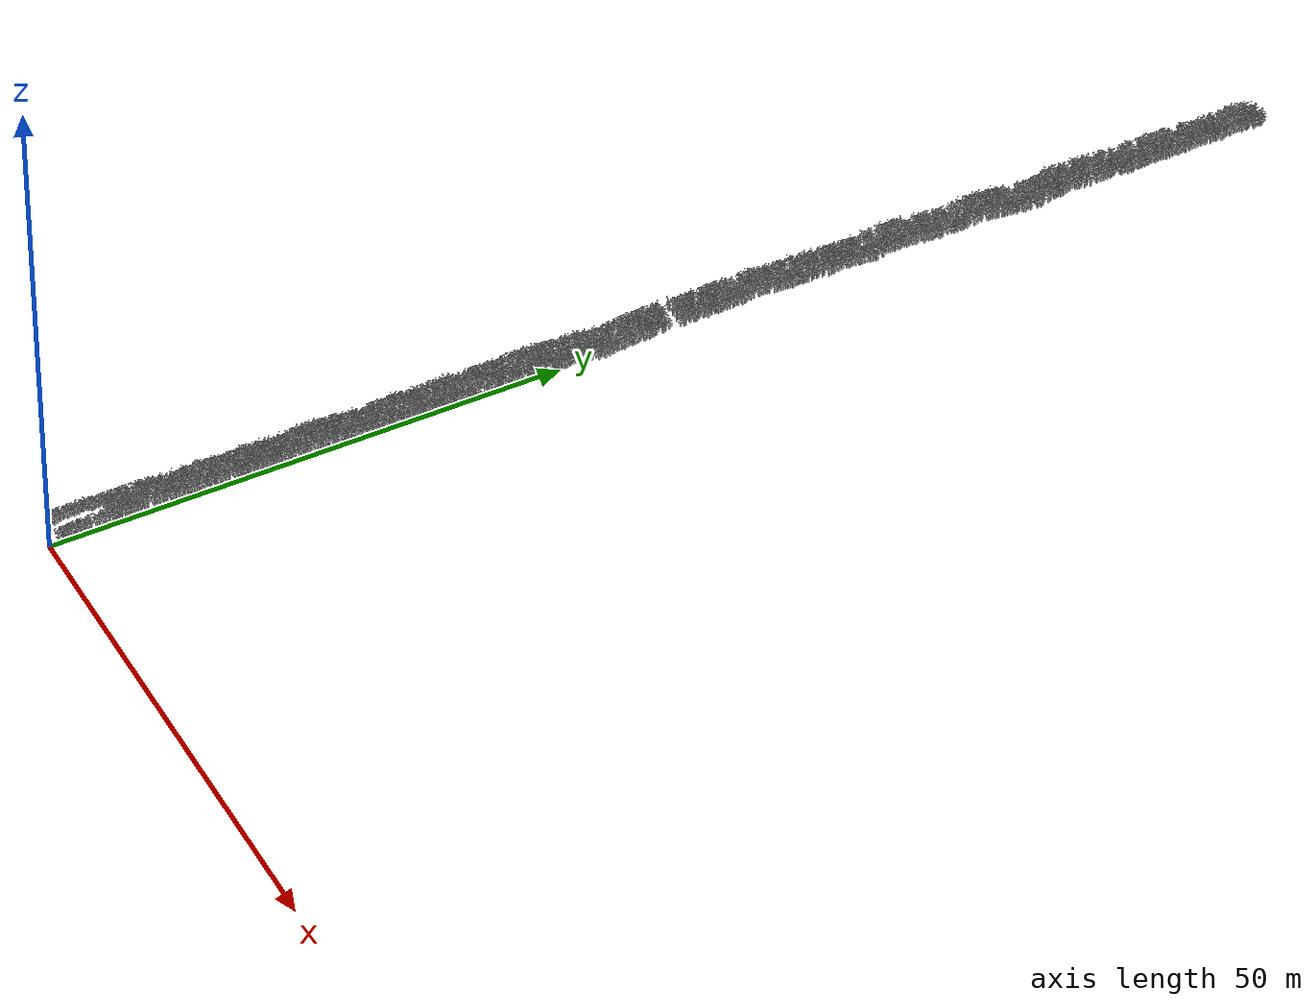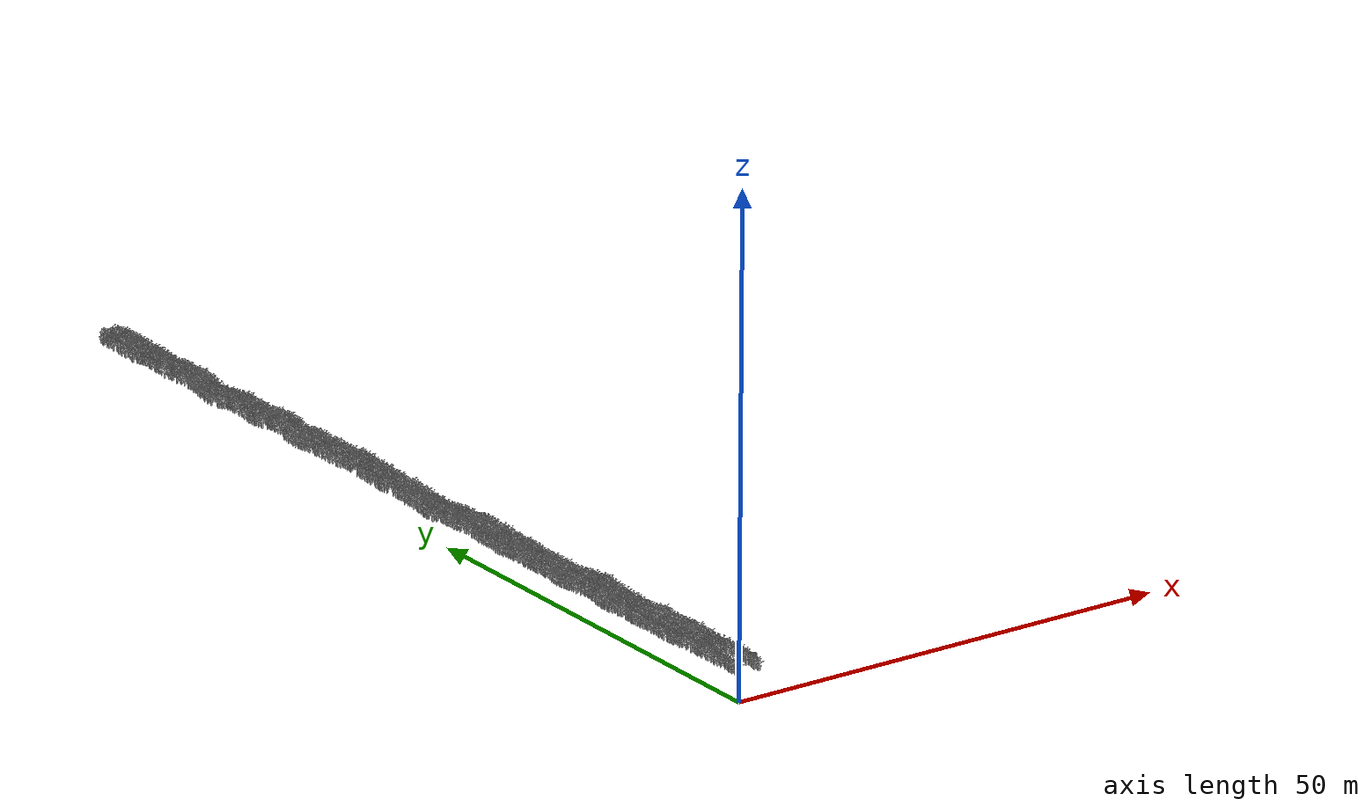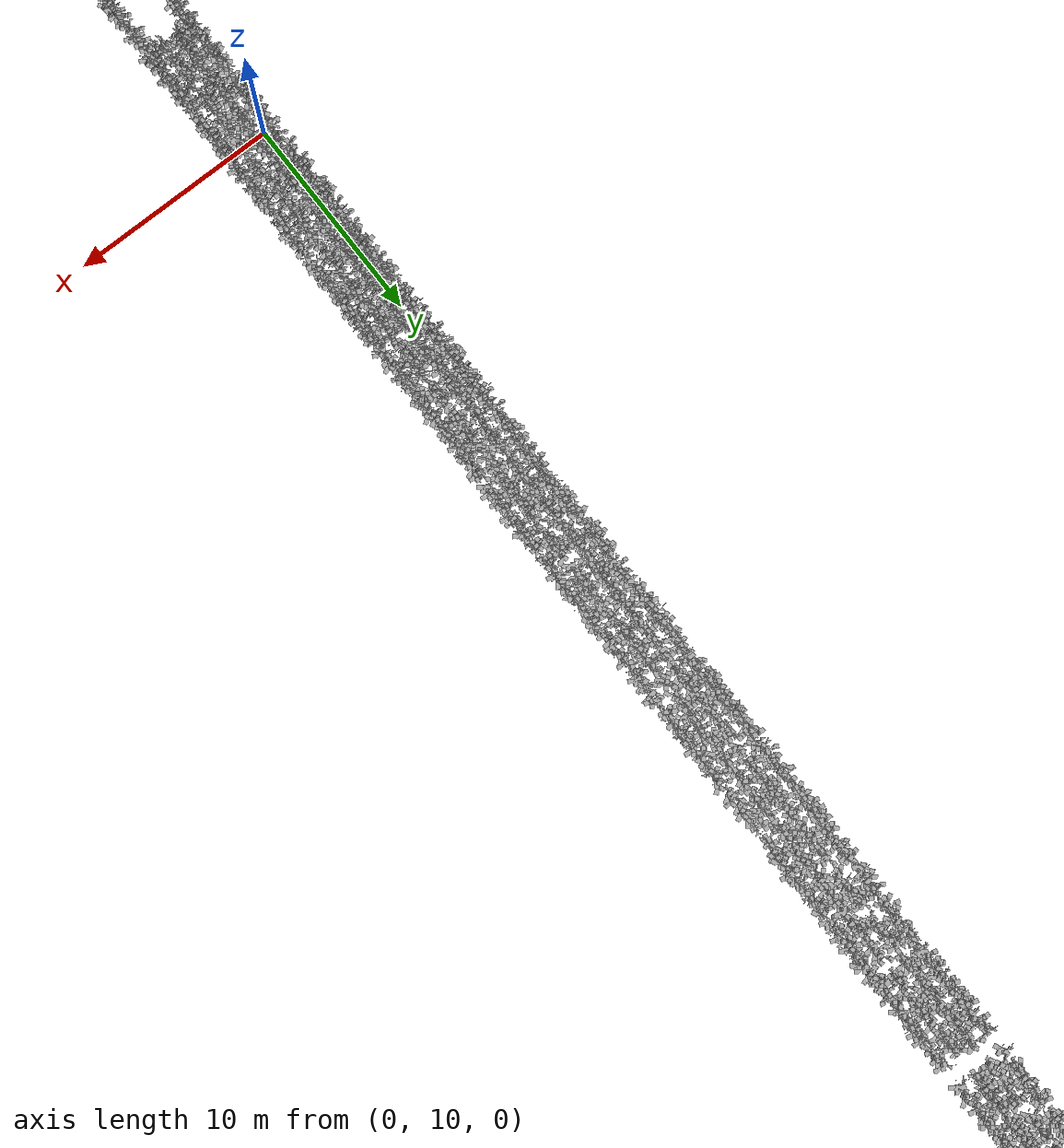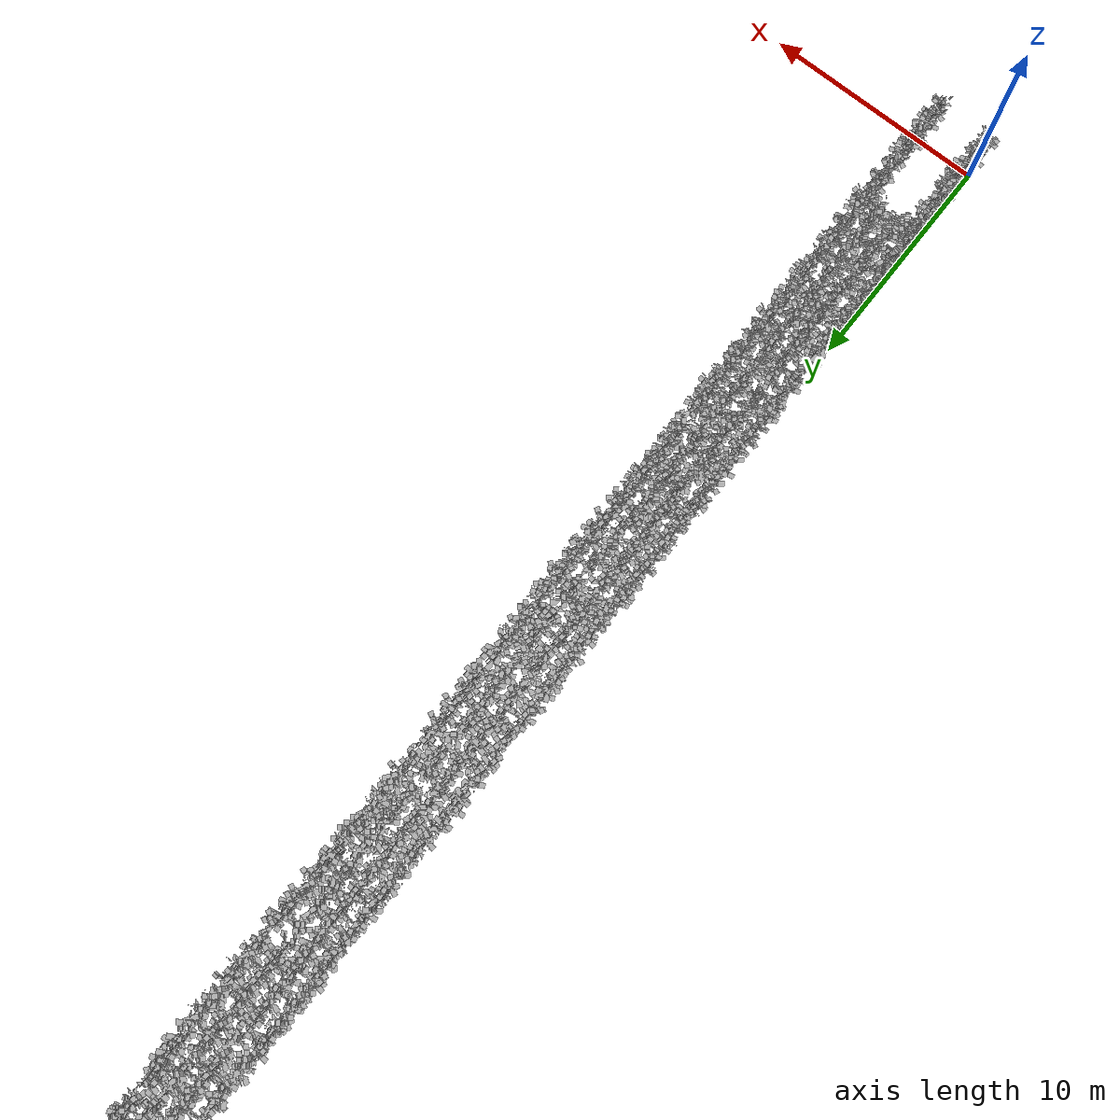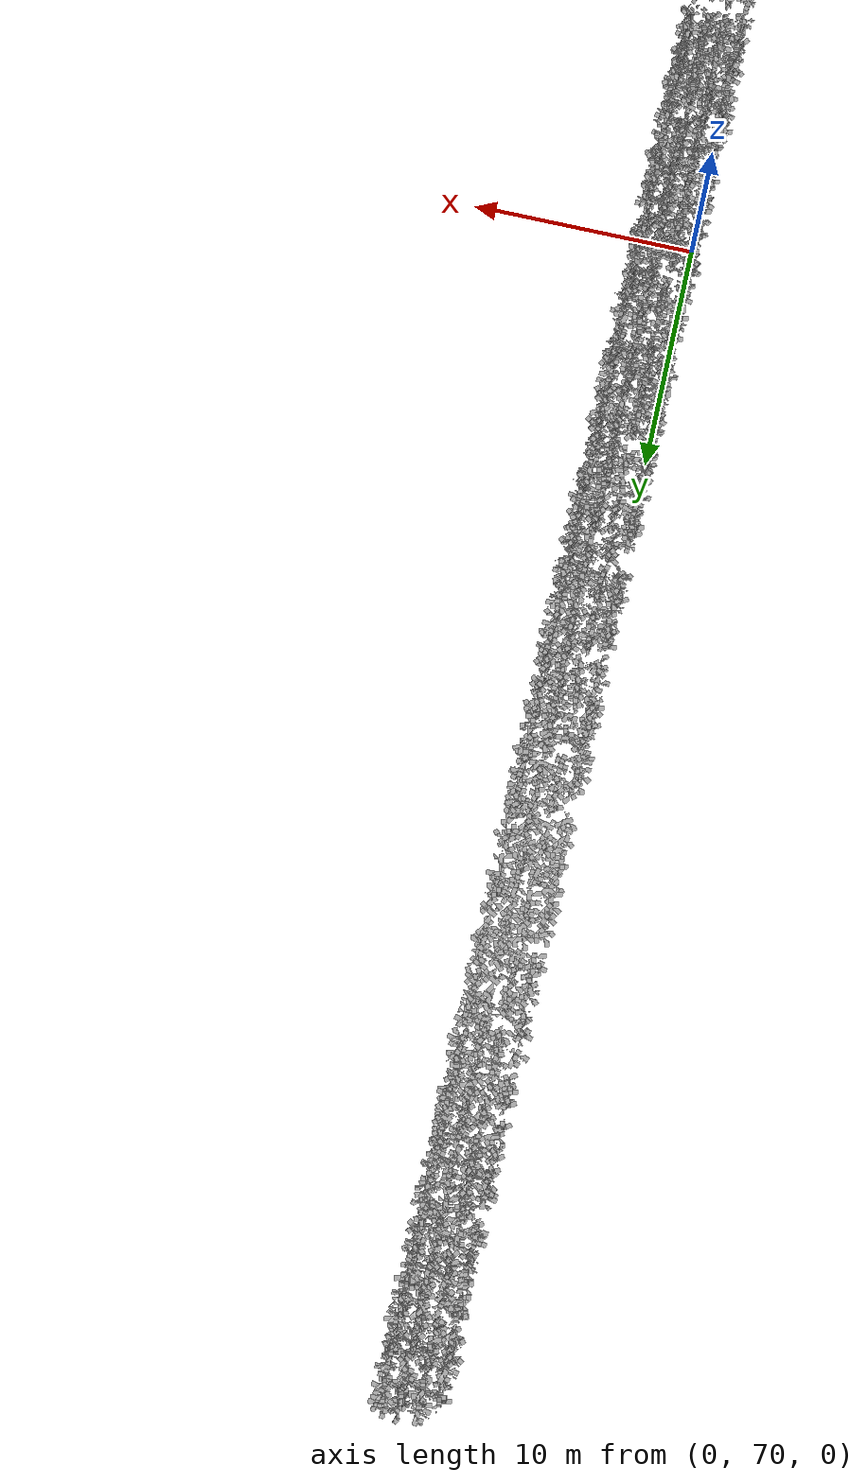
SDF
<sdf version="1.5">
  <model name="model_plot">
    <static>true</static>

    <include>
      <uri>model://sorghum_variant_2</uri>
      <name>plant_0_0</name>
      <pose>0.03383093891189891 0.02368867845082381 2.4329411764705884 0.0 0.0 4.4505895925855405</pose>
    </include>

    <include>
      <uri>model://sorghum_variant_2</uri>
      <name>plant_0_1</name>
      <pose>-0.06727194609533238 0.35735860455141794 2.458823529411765 0.0 0.0 4.6600291028248595</pose>
    </include>

    <include>
      <uri>model://sorghum_variant_2</uri>
      <name>plant_0_2</name>
      <pose>0.04984365100425677 0.5784542301001754 2.458823529411765 0.0 0.0 5.462880558742252</pose>
    </include>

    <include>
      <uri>model://sorghum_variant_2</uri>
      <name>plant_0_3</name>
      <pose>0.043222607277381905 0.8818294292301264 2.5364705882352943 0.0 0.0 5.462880558742252</pose>
    </include>

    <include>
      <uri>model://sorghum_variant_2</uri>
      <name>plant_0_4</name>
      <pose>-0.06417301222358751 1.1775255585836457 2.5623529411764707 0.0 0.0 0.017453292519943295</pose>
    </include>

    <include>
      <uri>model://sorghum_variant_2</uri>
      <name>plant_0_5</name>
      <pose>0.016969479035472 1.512117842859871 2.5882352941176467 0.0 0.0 3.420845333908886</pose>
    </include>

    <include>
      <uri>model://sorghum_variant_2</uri>
      <name>plant_0_6</name>
      <pose>-0.0005296306504708638 1.8389059548356452 2.601176470588235 0.0 0.0 0.19198621771937624</pose>
    </include>

    <include>
      <uri>model://sorghum_variant_2</uri>
      <name>plant_0_7</name>
      <pose>0.030500049130539938 2.1187241320861756 2.614117647058823 0.0 0.0 2.897246558310587</pose>
    </include>

    <include>
      <uri>model://sorghum_variant_2</uri>
      <name>plant_0_8</name>
      <pose>0.06952491542918052 2.4029752862148848 2.6270588235294117 0.0 0.0 2.303834612632515</pose>
    </include>

    <include>
      <uri>model://sorghum_variant_2</uri>
      <name>plant_0_9</name>
      <pose>-0.0006329647378500082 2.73414818253174 2.6270588235294117 0.0 0.0 1.7453292519943295</pose>
    </include>

    <include>
      <uri>model://sorghum_variant_2</uri>
      <name>plant_0_10</name>
      <pose>0.012063896136586514 3.002976926681025 2.6270588235294117 0.0 0.0 5.1312680008633285</pose>
    </include>

    <include>
      <uri>model://sorghum_variant_2</uri>
      <name>plant_0_11</name>
      <pose>-0.03706156106555111 3.3662893050633 2.6270588235294117 0.0 0.0 4.5553093477052</pose>
    </include>

    <include>
      <uri>model://sorghum_variant_2</uri>
      <name>plant_0_12</name>
      <pose>-0.0985742176926818 3.6507070192169255 2.614117647058823 0.0 0.0 1.9547687622336491</pose>
    </include>

    <include>
      <uri>model://sorghum_variant_2</uri>
      <name>plant_0_13</name>
      <pose>0.008380174138277238 3.951279133305522 2.601176470588235 0.0 0.0 3.2288591161895095</pose>
    </include>

    <include>
      <uri>model://sorghum_variant_2</uri>
      <name>plant_0_14</name>
      <pose>0.036037506579769375 4.221074095008121 2.601176470588235 0.0 0.0 6.178465552059927</pose>
    </include>

    <include>
      <uri>model://sorghum_variant_2</uri>
      <name>plant_0_15</name>
      <pose>0.05019386622378589 4.491673022736008 2.5882352941176467 0.0 0.0 4.71238898038469</pose>
    </include>

    <include>
      <uri>model://sorghum_variant_2</uri>
      <name>plant_0_16</name>
      <pose>0.019915711791611834 4.909945310511186 2.5882352941176467 0.0 0.0 4.101523742186674</pose>
    </include>

    <include>
      <uri>model://sorghum_variant_2</uri>
      <name>plant_0_17</name>
      <pose>-0.018952075985463137 5.205857551070282 2.5882352941176467 0.0 0.0 0.8028514559173916</pose>
    </include>

    <include>
      <uri>model://sorghum_variant_2</uri>
      <name>plant_0_18</name>
      <pose>0.07124165816492738 5.473838173515114 2.5882352941176467 0.0 0.0 2.443460952792061</pose>
    </include>

    <include>
      <uri>model://sorghum_variant_2</uri>
      <name>plant_0_19</name>
      <pose>-0.032931689619522767 5.77789473373265 2.5752941176470587 0.0 0.0 1.5009831567151235</pose>
    </include>

    <include>
      <uri>model://sorghum_variant_2</uri>
      <name>plant_0_20</name>
      <pose>0.016306466314510264 6.103260106559238 2.5752941176470587 0.0 0.0 0.5410520681182421</pose>
    </include>

    <include>
      <uri>model://sorghum_variant_2</uri>
      <name>plant_0_21</name>
      <pose>-0.04915646315014604 6.411248528791054 2.5623529411764707 0.0 0.0 3.001966313430247</pose>
    </include>

    <include>
      <uri>model://sorghum_variant_2</uri>
      <name>plant_0_22</name>
      <pose>0.05182735784360105 6.7083161567306915 2.5623529411764707 0.0 0.0 4.293509959906051</pose>
    </include>

    <include>
      <uri>model://sorghum_variant_2</uri>
      <name>plant_0_23</name>
      <pose>0.0019055898233849974 6.9886190086511 2.5494117647058823 0.0 0.0 0.3665191429188092</pose>
    </include>

    <include>
      <uri>model://sorghum_variant_2</uri>
      <name>plant_0_24</name>
      <pose>0.03714265983815513 7.311296149141978 2.5364705882352943 0.0 0.0 5.672320068981571</pose>
    </include>

    <include>
      <uri>model://sorghum_variant_2</uri>
      <name>plant_0_25</name>
      <pose>-0.04248026077517541 7.621483443394479 2.5235294117647054 0.0 0.0 0.8552113334772214</pose>
    </include>

    <include>
      <uri>model://sorghum_variant_2</uri>
      <name>plant_0_27</name>
      <pose>-0.02310438273061538 8.260260551459398 2.5235294117647054 0.0 0.0 2.6179938779914944</pose>
    </include>

    <include>
      <uri>model://sorghum_variant_2</uri>
      <name>plant_0_28</name>
      <pose>0.04729898045712334 8.581698980457123 2.5105882352941173 0.0 0.0 4.834562028024293</pose>
    </include>

    <include>
      <uri>model://sorghum_variant_2</uri>
      <name>plant_0_29</name>
      <pose>-0.01990326807372091 8.900455960486477 2.5105882352941173 0.0 0.0 5.689773361501515</pose>
    </include>

    <include>
      <uri>model://sorghum_variant_2</uri>
      <name>plant_0_30</name>
      <pose>0.03375814023701428 9.175479975050967 2.5105882352941173 0.0 0.0 0.24434609527920614</pose>
    </include>

    <include>
      <uri>model://sorghum_variant_2</uri>
      <name>plant_0_31</name>
      <pose>0.009040332306186349 9.445509588132673 2.4976470588235293 0.0 0.0 3.6826447217080354</pose>
    </include>

    <include>
      <uri>model://sorghum_variant_2</uri>
      <name>plant_0_32</name>
      <pose>-0.0024201434257943868 9.75438635226675 2.471764705882353 0.0 0.0 5.532693728822025</pose>
    </include>

    <include>
      <uri>model://sorghum_variant_2</uri>
      <name>plant_0_33</name>
      <pose>-8.960027618820464e-05 10.063533196384927 2.4458823529411764 0.0 0.0 5.218534463463046</pose>
    </include>

    <include>
      <uri>model://sorghum_variant_2</uri>
      <name>plant_0_34</name>
      <pose>0.011633548876018689 10.346585570361377 2.4199999999999995 0.0 0.0 2.9321531433504737</pose>
    </include>

    <include>
      <uri>model://sorghum_variant_2</uri>
      <name>plant_0_35</name>
      <pose>-0.024197432788575897 10.65513399676432 2.3941176470588235 0.0 0.0 3.717551306747922</pose>
    </include>

    <include>
      <uri>model://sorghum_variant_2</uri>
      <name>plant_0_36</name>
      <pose>-0.003888782123686423 10.948247195976334 2.368235294117647 0.0 0.0 1.361356816555577</pose>
    </include>

    <include>
      <uri>model://sorghum_variant_2</uri>
      <name>plant_0_37</name>
      <pose>0.03115069805578673 11.322087807336999 2.3423529411764705 0.0 0.0 3.7000980142279785</pose>
    </include>

    <include>
      <uri>model://sorghum_variant_2</uri>
      <name>plant_0_38</name>
      <pose>0.07764796779768592 11.56589541494426 2.3294117647058825 0.0 0.0 3.246312408709453</pose>
    </include>

    <include>
      <uri>model://sorghum_variant_2</uri>
      <name>plant_0_40</name>
      <pose>-0.025848014026625312 12.147229926431132 2.3164705882352936 0.0 0.0 4.6600291028248595</pose>
    </include>

    <include>
      <uri>model://sorghum_variant_2</uri>
      <name>plant_0_41</name>
      <pose>0.06858741133832029 12.516467123722405 2.3294117647058825 0.0 0.0 0.6806784082777885</pose>
    </include>

    <include>
      <uri>model://sorghum_variant_2</uri>
      <name>plant_0_42</name>
      <pose>-0.0038085756837924 12.7981707430513 2.3423529411764705 0.0 0.0 3.368485456349056</pose>
    </include>

    <include>
      <uri>model://sorghum_variant_2</uri>
      <name>plant_0_43</name>
      <pose>0.013440690279433629 13.059526742584312 2.368235294117647 0.0 0.0 4.71238898038469</pose>
    </include>

    <include>
      <uri>model://sorghum_variant_2</uri>
      <name>plant_0_44</name>
      <pose>-0.006260497785812971 13.401559678803588 2.3941176470588235 0.0 0.0 0.2617993877991494</pose>
    </include>

    <include>
      <uri>model://sorghum_variant_2</uri>
      <name>plant_0_45</name>
      <pose>0.04902902090397532 13.679053982725236 2.4199999999999995 0.0 0.0 3.0892327760299634</pose>
    </include>

    <include>
      <uri>model://sorghum_variant_2</uri>
      <name>plant_0_46</name>
      <pose>-0.05625034040840568 13.99807338726285 2.4458823529411764 0.0 0.0 3.6302848441482056</pose>
    </include>

    <include>
      <uri>model://sorghum_variant_2</uri>
      <name>plant_0_47</name>
      <pose>-0.01807433990384529 14.345673588094488 2.458823529411765 0.0 0.0 5.707226654021458</pose>
    </include>

    <include>
      <uri>model://sorghum_variant_2</uri>
      <name>plant_0_48</name>
      <pose>-0.00639528925372813 14.62126658039975 2.458823529411765 0.0 0.0 1.9373154697137058</pose>
    </include>

    <include>
      <uri>model://sorghum_variant_2</uri>
      <name>plant_0_49</name>
      <pose>-0.042655672136600965 14.880603229383187 2.458823529411765 0.0 0.0 0.20943951023931956</pose>
    </include>

    <include>
      <uri>model://sorghum_variant_2</uri>
      <name>plant_0_50</name>
      <pose>0.01745404052777945 15.202569689297324 2.4329411764705884 0.0 0.0 0.7853981633974483</pose>
    </include>

    <include>
      <uri>model://sorghum_variant_2</uri>
      <name>plant_0_51</name>
      <pose>-0.018056971033806234 15.555649722793136 2.3941176470588235 0.0 0.0 4.747295565424577</pose>
    </include>

    <include>
      <uri>model://sorghum_variant_2</uri>
      <name>plant_0_52</name>
      <pose>-0.014525467854237755 15.844024195298696 2.368235294117647 0.0 0.0 1.7976891295541595</pose>
    </include>

    <include>
      <uri>model://sorghum_variant_2</uri>
      <name>plant_0_53</name>
      <pose>-0.006021733463628582 16.13470379733268 2.3552941176470585 0.0 0.0 4.310963252425994</pose>
    </include>

    <include>
      <uri>model://sorghum_variant_2</uri>
      <name>plant_0_54</name>
      <pose>0.031231379480879267 16.392224090566195 2.3552941176470585 0.0 0.0 2.9321531433504737</pose>
    </include>

    <include>
      <uri>model://sorghum_variant_2</uri>
      <name>plant_0_55</name>
      <pose>0.02320893666803088 16.743824779155663 2.3164705882352936 0.0 0.0 4.694935687864747</pose>
    </include>

    <include>
      <uri>model://sorghum_variant_2</uri>
      <name>plant_0_56</name>
      <pose>-0.012794186420381264 17.082048767878593 2.3164705882352936 0.0 0.0 0.6806784082777885</pose>
    </include>

    <include>
      <uri>model://sorghum_variant_2</uri>
      <name>plant_0_57</name>
      <pose>0.06779142474290817 17.406664087072425 2.3164705882352936 0.0 0.0 3.4557519189487724</pose>
    </include>

    <include>
      <uri>model://sorghum_variant_2</uri>
      <name>plant_0_58</name>
      <pose>-0.018788145643543936 17.620576033458814 2.3164705882352936 0.0 0.0 0.15707963267948966</pose>
    </include>

    <include>
      <uri>model://sorghum_variant_2</uri>
      <name>plant_0_59</name>
      <pose>0.030215468994315837 17.96974720646368 2.3423529411764705 0.0 0.0 2.949606435870417</pose>
    </include>

    <include>
      <uri>model://sorghum_variant_2</uri>
      <name>plant_0_60</name>
      <pose>-0.002522554714918456 18.292369192931112 2.368235294117647 0.0 0.0 0.6457718232379019</pose>
    </include>

    <include>
      <uri>model://sorghum_variant_2</uri>
      <name>plant_0_61</name>
      <pose>0.04208591593194821 18.513647904088444 2.3941176470588235 0.0 0.0 4.34586983746588</pose>
    </include>

    <include>
      <uri>model://sorghum_variant_2</uri>
      <name>plant_0_62</name>
      <pose>-0.0640147915581934 18.927450587538782 2.4070588235294115 0.0 0.0 5.619960191421741</pose>
    </include>

    <include>
      <uri>model://sorghum_variant_2</uri>
      <name>plant_0_63</name>
      <pose>-0.011524961492089867 19.208788390472712 2.4070588235294115 0.0 0.0 6.09119908946021</pose>
    </include>

    <include>
      <uri>model://sorghum_variant_2</uri>
      <name>plant_0_64</name>
      <pose>-0.0734174621026619 19.511047646149397 2.4070588235294115 0.0 0.0 1.0995574287564276</pose>
    </include>

    <include>
      <uri>model://sorghum_variant_2</uri>
      <name>plant_0_65</name>
      <pose>0.027391350398970945 19.800933176077777 2.3941176470588235 0.0 0.0 3.12413936106985</pose>
    </include>

    <include>
      <uri>model://sorghum_variant_2</uri>
      <name>plant_0_66</name>
      <pose>0.026349543527465068 20.11119923162623 2.381176470588235 0.0 0.0 5.550147021341968</pose>
    </include>

    <include>
      <uri>model://sorghum_variant_2</uri>
      <name>plant_0_67</name>
      <pose>0.08141249719563255 20.372682436538454 2.3552941176470585 0.0 0.0 0.10471975511965978</pose>
    </include>

    <include>
      <uri>model://sorghum_variant_2</uri>
      <name>plant_0_68</name>
      <pose>-0.0019873724879323185 20.73157728233579 2.3294117647058825 0.0 0.0 4.956735075663896</pose>
    </include>

    <include>
      <uri>model://sorghum_variant_2</uri>
      <name>plant_0_69</name>
      <pose>-0.045475098452336334 21.044239774648137 2.3035294117647056 0.0 0.0 1.6231562043547265</pose>
    </include>

    <include>
      <uri>model://sorghum_variant_2</uri>
      <name>plant_0_70</name>
      <pose>0.021289665383722574 21.341308109751324 2.277647058823529 0.0 0.0 1.4486232791552935</pose>
    </include>

    <include>
      <uri>model://sorghum_variant_2</uri>
      <name>plant_0_71</name>
      <pose>-0.008599044015446481 21.64170379594526 2.2517647058823527 0.0 0.0 4.869468613064179</pose>
    </include>

    <include>
      <uri>model://sorghum_variant_2</uri>
      <name>plant_0_72</name>
      <pose>0.0016656581469066858 21.964638559737665 2.2388235294117647 0.0 0.0 0.6632251157578453</pose>
    </include>

    <include>
      <uri>model://sorghum_variant_2</uri>
      <name>plant_0_73</name>
      <pose>-0.04462461959226761 22.303581550717237 2.2517647058823527 0.0 0.0 1.6755160819145565</pose>
    </include>

    <include>
      <uri>model://sorghum_variant_2</uri>
      <name>plant_0_74</name>
      <pose>-0.033362507944006 22.564766545210286 2.2905882352941176 0.0 0.0 4.60766922526503</pose>
    </include>

    <include>
      <uri>model://sorghum_variant_2</uri>
      <name>plant_0_75</name>
      <pose>0.018326424471205822 22.916402934890314 2.3423529411764705 0.0 0.0 1.3439035240356338</pose>
    </include>

    <include>
      <uri>model://sorghum_variant_2</uri>
      <name>plant_0_76</name>
      <pose>0.04247575776802908 23.196807779297284 2.381176470588235 0.0 0.0 4.2062434973063345</pose>
    </include>

    <include>
      <uri>model://sorghum_variant_2</uri>
      <name>plant_0_77</name>
      <pose>-0.04026014090911239 23.427909403651135 2.381176470588235 0.0 0.0 3.6477381366681487</pose>
    </include>

    <include>
      <uri>model://sorghum_variant_2</uri>
      <name>plant_0_78</name>
      <pose>-0.004125505173009961 23.77172086561487 2.471764705882353 0.0 0.0 0.03490658503988659</pose>
    </include>

    <include>
      <uri>model://sorghum_variant_2</uri>
      <name>plant_0_79</name>
      <pose>-0.011892634482458591 24.11373871842818 2.4976470588235293 0.0 0.0 0.20943951023931956</pose>
    </include>

    <include>
      <uri>model://sorghum_variant_2</uri>
      <name>plant_0_80</name>
      <pose>-0.0011160870141875875 24.41596055042405 2.5364705882352943 0.0 0.0 5.044001538263612</pose>
    </include>

    <include>
      <uri>model://sorghum_variant_2</uri>
      <name>plant_0_81</name>
      <pose>0.06074511841449331 24.66906271457713 2.5494117647058823 0.0 0.0 1.8500490071139892</pose>
    </include>

    <include>
      <uri>model://sorghum_variant_2</uri>
      <name>plant_0_82</name>
      <pose>-0.0023975389895735987 25.016411059740012 2.5623529411764707 0.0 0.0 5.567600313861911</pose>
    </include>

    <include>
      <uri>model://sorghum_variant_2</uri>
      <name>plant_0_83</name>
      <pose>0.05713795220377909 25.248730735923278 2.5623529411764707 0.0 0.0 1.8325957145940461</pose>
    </include>

    <include>
      <uri>model://sorghum_variant_2</uri>
      <name>plant_0_84</name>
      <pose>0.0081266392198317 25.60234585579952 2.5494117647058823 0.0 0.0 5.1312680008633285</pose>
    </include>

    <include>
      <uri>model://sorghum_variant_2</uri>
      <name>plant_0_85</name>
      <pose>-0.058467957391351404 25.855355214702996 2.5364705882352943 0.0 0.0 1.7278759594743862</pose>
    </include>

    <include>
      <uri>model://sorghum_variant_2</uri>
      <name>plant_0_86</name>
      <pose>0.05041773313337103 26.140796014921122 2.5105882352941173 0.0 0.0 4.590215932745087</pose>
    </include>

    <include>
      <uri>model://sorghum_variant_2</uri>
      <name>plant_0_87</name>
      <pose>0.006489892893488199 26.5063591757728 2.484705882352941 0.0 0.0 2.4085543677521746</pose>
    </include>

    <include>
      <uri>model://sorghum_variant_2</uri>
      <name>plant_0_88</name>
      <pose>0.002597457723214378 26.772837554142754 2.458823529411765 0.0 0.0 4.328416544945937</pose>
    </include>

    <include>
      <uri>model://sorghum_variant_2</uri>
      <name>plant_0_89</name>
      <pose>-0.032057113120356875 27.16823123369067 2.4329411764705884 0.0 0.0 2.8448866807507573</pose>
    </include>

    <include>
      <uri>model://sorghum_variant_2</uri>
      <name>plant_0_90</name>
      <pose>-0.02355404150591515 27.487489844406422 2.4199999999999995 0.0 0.0 3.2986722862692828</pose>
    </include>

    <include>
      <uri>model://sorghum_variant_2</uri>
      <name>plant_0_91</name>
      <pose>0.00458036002004298 27.739235420623064 2.3941176470588235 0.0 0.0 5.759586531581287</pose>
    </include>

    <include>
      <uri>model://sorghum_variant_2</uri>
      <name>plant_0_92</name>
      <pose>0.015206057590362516 28.05110179935159 2.368235294117647 0.0 0.0 4.101523742186674</pose>
    </include>

    <include>
      <uri>model://sorghum_variant_2</uri>
      <name>plant_0_93</name>
      <pose>0.005964924940748164 28.289647530171642 2.3294117647058825 0.0 0.0 3.420845333908886</pose>
    </include>

    <include>
      <uri>model://sorghum_variant_2</uri>
      <name>plant_0_94</name>
      <pose>-0.012890704667838608 28.61376267528276 2.277647058823529 0.0 0.0 0.47123889803846897</pose>
    </include>

    <include>
      <uri>model://sorghum_variant_2</uri>
      <name>plant_0_95</name>
      <pose>0.048725514341726665 29.037092873785916 2.2129411764705877 0.0 0.0 4.293509959906051</pose>
    </include>

    <include>
      <uri>model://sorghum_variant_2</uri>
      <name>plant_0_96</name>
      <pose>-0.07748783712971788 29.258094065101183 2.2129411764705877 0.0 0.0 0.7853981633974483</pose>
    </include>

    <include>
      <uri>model://sorghum_variant_2</uri>
      <name>plant_0_97</name>
      <pose>0.0016194226379525128 29.562904828130403 2.1870588235294117 0.0 0.0 1.4311699866353502</pose>
    </include>

    <include>
      <uri>model://sorghum_variant_2</uri>
      <name>plant_0_98</name>
      <pose>-0.030544073749639772 29.801796887133467 2.1611764705882353 0.0 0.0 4.886921905584122</pose>
    </include>

    <include>
      <uri>model://sorghum_variant_2</uri>
      <name>plant_0_99</name>
      <pose>0.07691332984265173 30.194376646921686 2.148235294117647 0.0 0.0 3.07177948351002</pose>
    </include>

    <include>
      <uri>model://sorghum_variant_2</uri>
      <name>plant_0_100</name>
      <pose>0.032797325603533205 30.509530844615576 2.1611764705882353 0.0 0.0 1.3089969389957472</pose>
    </include>

    <include>
      <uri>model://sorghum_variant_2</uri>
      <name>plant_0_101</name>
      <pose>0.00404056093578479 30.78423213619342 2.1870588235294117 0.0 0.0 1.1868238913561442</pose>
    </include>

    <include>
      <uri>model://sorghum_variant_2</uri>
      <name>plant_0_102</name>
      <pose>0.08073458798985866 31.100946506385448 2.2129411764705877 0.0 0.0 1.4660765716752369</pose>
    </include>

    <include>
      <uri>model://sorghum_variant_2</uri>
      <name>plant_0_103</name>
      <pose>0.005194611400607235 31.364939894803758 2.2517647058823527 0.0 0.0 5.672320068981571</pose>
    </include>

    <include>
      <uri>model://sorghum_variant_2</uri>
      <name>plant_0_104</name>
      <pose>0.05243821831673953 31.69645182942846 2.3035294117647056 0.0 0.0 6.056292504420323</pose>
    </include>

    <include>
      <uri>model://sorghum_variant_2</uri>
      <name>plant_0_105</name>
      <pose>-0.026726413551694087 32.05221572637439 2.3423529411764705 0.0 0.0 2.91469985083053</pose>
    </include>

    <include>
      <uri>model://sorghum_variant_2</uri>
      <name>plant_0_106</name>
      <pose>0.004485031783606315 32.24466105731191 2.368235294117647 0.0 0.0 2.6354471705114375</pose>
    </include>

    <include>
      <uri>model://sorghum_variant_2</uri>
      <name>plant_0_107</name>
      <pose>-0.030313560519110754 32.68168537167389 2.381176470588235 0.0 0.0 0.5061454830783556</pose>
    </include>

    <include>
      <uri>model://sorghum_variant_2</uri>
      <name>plant_0_109</name>
      <pose>0.06040996956609127 33.201212569225014 2.4070588235294115 0.0 0.0 6.073745796940266</pose>
    </include>

    <include>
      <uri>model://sorghum_variant_2</uri>
      <name>plant_0_110</name>
      <pose>-0.015531249947020261 33.5229535909851 2.3941176470588235 0.0 0.0 4.71238898038469</pose>
    </include>

    <include>
      <uri>model://sorghum_variant_2</uri>
      <name>plant_0_111</name>
      <pose>-0.06818794119840123 33.79954251893032 2.381176470588235 0.0 0.0 0.12217304763960307</pose>
    </include>

    <include>
      <uri>model://sorghum_variant_2</uri>
      <name>plant_0_112</name>
      <pose>0.011869931310487697 34.13926821005423 2.368235294117647 0.0 0.0 5.044001538263612</pose>
    </include>

    <include>
      <uri>model://sorghum_variant_2</uri>
      <name>plant_0_113</name>
      <pose>0.00895575156339413 34.42555668101766 2.3423529411764705 0.0 0.0 0.05235987755982989</pose>
    </include>

    <include>
      <uri>model://sorghum_variant_2</uri>
      <name>plant_0_114</name>
      <pose>-0.011470245699516907 34.75553362130737 2.3294117647058825 0.0 0.0 0.6108652381980153</pose>
    </include>

    <include>
      <uri>model://sorghum_variant_2</uri>
      <name>plant_0_115</name>
      <pose>0.025463759497622515 35.109192540233515 2.3164705882352936 0.0 0.0 2.6179938779914944</pose>
    </include>

    <include>
      <uri>model://sorghum_variant_2</uri>
      <name>plant_0_116</name>
      <pose>0.03200941260416593 35.40425590575195 2.3035294117647056 0.0 0.0 4.537856055185257</pose>
    </include>

    <include>
      <uri>model://sorghum_variant_2</uri>
      <name>plant_0_117</name>
      <pose>0.02221514397620275 35.719472428643 2.3035294117647056 0.0 0.0 1.9024088846738192</pose>
    </include>

    <include>
      <uri>model://sorghum_variant_2</uri>
      <name>plant_0_118</name>
      <pose>0.015100759498559558 35.96933529029955 2.3164705882352936 0.0 0.0 1.7453292519943295</pose>
    </include>

    <include>
      <uri>model://sorghum_variant_2</uri>
      <name>plant_0_119</name>
      <pose>-0.00604175748994794 36.213716517296604 2.3423529411764705 0.0 0.0 2.4609142453120048</pose>
    </include>

    <include>
      <uri>model://sorghum_variant_2</uri>
      <name>plant_0_120</name>
      <pose>-0.01459477388187231 36.61838630106495 2.368235294117647 0.0 0.0 2.4609142453120048</pose>
    </include>

    <include>
      <uri>model://sorghum_variant_2</uri>
      <name>plant_0_121</name>
      <pose>-0.03271097694754176 36.877938160344236 2.3941176470588235 0.0 0.0 0.767944870877505</pose>
    </include>

    <include>
      <uri>model://sorghum_variant_2</uri>
      <name>plant_0_122</name>
      <pose>0.0033999172866390165 37.18711374070369 2.4070588235294115 0.0 0.0 5.759586531581287</pose>
    </include>

    <include>
      <uri>model://sorghum_variant_2</uri>
      <name>plant_0_123</name>
      <pose>-0.02952845465025295 37.54367074232842 2.4329411764705884 0.0 0.0 1.710422666954443</pose>
    </include>

    <include>
      <uri>model://sorghum_variant_2</uri>
      <name>plant_0_124</name>
      <pose>-0.0524067650332832 37.80256529050183 2.4329411764705884 0.0 0.0 1.6580627893946132</pose>
    </include>

    <include>
      <uri>model://sorghum_variant_2</uri>
      <name>plant_0_125</name>
      <pose>0.016027755778507773 38.15242442695656 2.4199999999999995 0.0 0.0 1.4835298641951802</pose>
    </include>

    <include>
      <uri>model://sorghum_variant_2</uri>
      <name>plant_0_126</name>
      <pose>0.011787572397610375 38.4075213755172 2.4070588235294115 0.0 0.0 0.6108652381980153</pose>
    </include>

    <include>
      <uri>model://sorghum_variant_2</uri>
      <name>plant_0_127</name>
      <pose>-0.025357309507592907 38.71181847711944 2.381176470588235 0.0 0.0 4.869468613064179</pose>
    </include>

    <include>
      <uri>model://sorghum_variant_2</uri>
      <name>plant_0_128</name>
      <pose>0.00676548644130597 39.03652890904187 2.3552941176470585 0.0 0.0 1.2566370614359172</pose>
    </include>

    <include>
      <uri>model://sorghum_variant_2</uri>
      <name>plant_0_129</name>
      <pose>-0.0053895282541960195 39.3192 2.3164705882352936 0.0 0.0 5.061454830783556</pose>
    </include>

    <include>
      <uri>model://sorghum_variant_2</uri>
      <name>plant_0_130</name>
      <pose>0.0022118834103426166 39.62621188341034 2.2905882352941176 0.0 0.0 2.8797932657906435</pose>
    </include>

    <include>
      <uri>model://sorghum_variant_2</uri>
      <name>plant_0_131</name>
      <pose>0.009748853595099971 39.91586283431989 2.264705882352941 0.0 0.0 1.5882496193148399</pose>
    </include>

    <include>
      <uri>model://sorghum_variant_2</uri>
      <name>plant_0_132</name>
      <pose>-0.014150874632147977 40.243144885460154 2.2517647058823527 0.0 0.0 3.2812189937493397</pose>
    </include>

    <include>
      <uri>model://sorghum_variant_2</uri>
      <name>plant_0_133</name>
      <pose>0.018097415518749983 40.526647400944874 2.2517647058823527 0.0 0.0 3.8920842319473548</pose>
    </include>

    <include>
      <uri>model://sorghum_variant_2</uri>
      <name>plant_0_134</name>
      <pose>-0.04569051094694415 40.846394991766594 2.277647058823529 0.0 0.0 3.385938748868999</pose>
    </include>

    <include>
      <uri>model://sorghum_variant_2</uri>
      <name>plant_0_135</name>
      <pose>0.0010353753318662338 41.17764927024621 2.2905882352941176 0.0 0.0 5.899212871740834</pose>
    </include>

    <include>
      <uri>model://sorghum_variant_2</uri>
      <name>plant_0_136</name>
      <pose>-0.03767125420168457 41.504650033204676 2.3035294117647056 0.0 0.0 6.19591884457987</pose>
    </include>

    <include>
      <uri>model://sorghum_variant_2</uri>
      <name>plant_0_137</name>
      <pose>-0.02271908862800238 41.74933092798975 2.3035294117647056 0.0 0.0 5.497787143782138</pose>
    </include>

    <include>
      <uri>model://sorghum_variant_2</uri>
      <name>plant_0_138</name>
      <pose>0.018389149089506007 42.091828790247625 2.3035294117647056 0.0 0.0 5.724679946541401</pose>
    </include>

    <include>
      <uri>model://sorghum_variant_2</uri>
      <name>plant_0_139</name>
      <pose>-0.0121223219107961 42.382715864492475 2.3035294117647056 0.0 0.0 5.1312680008633285</pose>
    </include>

    <include>
      <uri>model://sorghum_variant_2</uri>
      <name>plant_0_140</name>
      <pose>0.02789583719730678 42.665559738526326 2.3035294117647056 0.0 0.0 0.4363323129985824</pose>
    </include>

    <include>
      <uri>model://sorghum_variant_2</uri>
      <name>plant_0_141</name>
      <pose>-0.03595976628651995 42.95686717605926 2.3164705882352936 0.0 0.0 5.654866776461628</pose>
    </include>

    <include>
      <uri>model://sorghum_variant_2</uri>
      <name>plant_0_142</name>
      <pose>-0.018825509820983286 43.223661038345035 2.3294117647058825 0.0 0.0 5.323254218582705</pose>
    </include>

    <include>
      <uri>model://sorghum_variant_2</uri>
      <name>plant_0_143</name>
      <pose>-0.005245562411836189 43.59447745777349 2.3423529411764705 0.0 0.0 4.869468613064179</pose>
    </include>

    <include>
      <uri>model://sorghum_variant_2</uri>
      <name>plant_0_144</name>
      <pose>-0.018912034441753142 43.96178067341112 2.4070588235294115 0.0 0.0 3.420845333908886</pose>
    </include>

    <include>
      <uri>model://sorghum_variant_2</uri>
      <name>plant_0_145</name>
      <pose>-0.021706535185645227 44.240504992478506 2.4458823529411764 0.0 0.0 0.9250245035569946</pose>
    </include>

    <include>
      <uri>model://sorghum_variant_2</uri>
      <name>plant_0_146</name>
      <pose>-0.02783842733536599 44.479050236858335 2.4458823529411764 0.0 0.0 6.265732014659643</pose>
    </include>

    <include>
      <uri>model://sorghum_variant_2</uri>
      <name>plant_0_147</name>
      <pose>0.040523953235725434 44.85221747553808 2.5364705882352943 0.0 0.0 2.3736477827122884</pose>
    </include>

    <include>
      <uri>model://sorghum_variant_2</uri>
      <name>plant_0_148</name>
      <pose>-0.07021795869117721 45.04717546601213 2.5364705882352943 0.0 0.0 2.234021442552742</pose>
    </include>

    <include>
      <uri>model://sorghum_variant_2</uri>
      <name>plant_0_149</name>
      <pose>-0.03682644210904652 45.34876333977855 2.5752941176470587 0.0 0.0 4.223696789826278</pose>
    </include>

    <include>
      <uri>model://sorghum_variant_2</uri>
      <name>plant_0_150</name>
      <pose>-0.01902872340856468 45.80242245636262 2.6270588235294117 0.0 0.0 2.8623399732707004</pose>
    </include>

    <include>
      <uri>model://sorghum_variant_2</uri>
      <name>plant_0_151</name>
      <pose>0.0427248051143704 46.0083994839127 2.6270588235294117 0.0 0.0 4.956735075663896</pose>
    </include>

    <include>
      <uri>model://sorghum_variant_2</uri>
      <name>plant_0_152</name>
      <pose>-0.014052916897510792 46.257304009938814 2.6270588235294117 0.0 0.0 3.822271061867582</pose>
    </include>

    <include>
      <uri>model://sorghum_variant_2</uri>
      <name>plant_0_153</name>
      <pose>-0.031493957502433834 46.64283878047924 2.5882352941176467 0.0 0.0 4.6600291028248595</pose>
    </include>

    <include>
      <uri>model://sorghum_variant_2</uri>
      <name>plant_0_155</name>
      <pose>-0.03683008836576482 47.253182772376775 2.5235294117647054 0.0 0.0 1.361356816555577</pose>
    </include>

    <include>
      <uri>model://sorghum_variant_2</uri>
      <name>plant_0_156</name>
      <pose>-0.054995694437090056 47.5721442872885 2.484705882352941 0.0 0.0 5.235987755982989</pose>
    </include>

    <include>
      <uri>model://sorghum_variant_2</uri>
      <name>plant_0_157</name>
      <pose>-0.027607720621532664 47.83203048469778 2.4458823529411764 0.0 0.0 1.413716694115407</pose>
    </include>

    <include>
      <uri>model://sorghum_variant_2</uri>
      <name>plant_0_158</name>
      <pose>-0.004974591344190937 48.154651376544976 2.4070588235294115 0.0 0.0 4.34586983746588</pose>
    </include>

    <include>
      <uri>model://sorghum_variant_2</uri>
      <name>plant_0_159</name>
      <pose>-0.04231925412046744 48.469147583298074 2.381176470588235 0.0 0.0 6.178465552059927</pose>
    </include>

    <include>
      <uri>model://sorghum_variant_2</uri>
      <name>plant_0_160</name>
      <pose>-0.04067703671267704 48.691497620522604 2.3552941176470585 0.0 0.0 5.585053606381854</pose>
    </include>

    <include>
      <uri>model://sorghum_variant_2</uri>
      <name>plant_0_161</name>
      <pose>0.007319172540205895 49.06984286234235 2.3552941176470585 0.0 0.0 0.10471975511965978</pose>
    </include>

    <include>
      <uri>model://sorghum_variant_2</uri>
      <name>plant_0_162</name>
      <pose>-0.0011967439883570834 49.37478064784374 2.3552941176470585 0.0 0.0 5.777039824101231</pose>
    </include>

    <include>
      <uri>model://sorghum_variant_2</uri>
      <name>plant_0_163</name>
      <pose>0.06527454166649327 49.661191015749985 2.3552941176470585 0.0 0.0 1.2217304763960306</pose>
    </include>

    <include>
      <uri>model://sorghum_variant_2</uri>
      <name>plant_0_164</name>
      <pose>0.007787638165375685 49.98899791793638 2.381176470588235 0.0 0.0 3.6651914291880923</pose>
    </include>

    <include>
      <uri>model://sorghum_variant_2</uri>
      <name>plant_0_165</name>
      <pose>-0.01567375841057447 50.31067925789526 2.3941176470588235 0.0 0.0 1.7802358370342162</pose>
    </include>

    <include>
      <uri>model://sorghum_variant_2</uri>
      <name>plant_0_166</name>
      <pose>-0.03731738787622498 50.593535151608435 2.3941176470588235 0.0 0.0 1.53588974175501</pose>
    </include>

    <include>
      <uri>model://sorghum_variant_2</uri>
      <name>plant_0_167</name>
      <pose>-0.005897610772743723 50.90435010106815 2.368235294117647 0.0 0.0 0.2792526803190927</pose>
    </include>

    <include>
      <uri>model://sorghum_variant_2</uri>
      <name>plant_0_169</name>
      <pose>-0.08681859488459621 51.521859983051115 2.3035294117647056 0.0 0.0 1.5707963267948966</pose>
    </include>

    <include>
      <uri>model://sorghum_variant_2</uri>
      <name>plant_0_170</name>
      <pose>-0.09635986170250341 51.83299084347549 2.2517647058823527 0.0 0.0 5.462880558742252</pose>
    </include>

    <include>
      <uri>model://sorghum_variant_2</uri>
      <name>plant_0_171</name>
      <pose>0.003814745892127417 52.11963371513881 2.1999999999999997 0.0 0.0 3.2288591161895095</pose>
    </include>

    <include>
      <uri>model://sorghum_variant_2</uri>
      <name>plant_0_172</name>
      <pose>-0.04511024421240982 52.450605016680186 2.096470588235294 0.0 0.0 3.961897402027128</pose>
    </include>

    <include>
      <uri>model://sorghum_variant_2</uri>
      <name>plant_0_173</name>
      <pose>0.021533500550486917 52.68624978109869 2.096470588235294 0.0 0.0 2.4958208303518914</pose>
    </include>

    <include>
      <uri>model://sorghum_variant_2</uri>
      <name>plant_0_175</name>
      <pose>-0.01970931361833906 53.31566102465546 2.031764705882353 0.0 0.0 0.4886921905584123</pose>
    </include>

    <include>
      <uri>model://sorghum_variant_2</uri>
      <name>plant_0_176</name>
      <pose>-0.04689796705053352 53.5802504860448 2.018823529411765 0.0 0.0 4.4156830075456535</pose>
    </include>

    <include>
      <uri>model://sorghum_variant_2</uri>
      <name>plant_0_177</name>
      <pose>-0.0073396436655401515 53.969765505237916 2.044705882352941 0.0 0.0 0.6108652381980153</pose>
    </include>

    <include>
      <uri>model://sorghum_variant_2</uri>
      <name>plant_0_178</name>
      <pose>0.01067433840423101 54.17844813571205 2.044705882352941 0.0 0.0 3.543018381548489</pose>
    </include>

    <include>
      <uri>model://sorghum_variant_2</uri>
      <name>plant_0_179</name>
      <pose>0.0517764544652979 54.590310432481076 2.148235294117647 0.0 0.0 2.9845130209103035</pose>
    </include>

    <include>
      <uri>model://sorghum_variant_2</uri>
      <name>plant_0_180</name>
      <pose>-0.04459297049074526 54.92317687057042 2.1999999999999997 0.0 0.0 1.0122909661567112</pose>
    </include>

    <include>
      <uri>model://sorghum_variant_2</uri>
      <name>plant_0_181</name>
      <pose>-0.023718077421416107 55.15510636161609 2.2388235294117647 0.0 0.0 2.705260340591211</pose>
    </include>

    <include>
      <uri>model://sorghum_variant_2</uri>
      <name>plant_0_182</name>
      <pose>0.04060868231725849 55.46347511833975 2.264705882352941 0.0 0.0 1.4835298641951802</pose>
    </include>

    <include>
      <uri>model://sorghum_variant_2</uri>
      <name>plant_0_183</name>
      <pose>0.0031139576159181963 55.773604925768446 2.2905882352941176 0.0 0.0 2.548180707911721</pose>
    </include>

    <include>
      <uri>model://sorghum_variant_2</uri>
      <name>plant_0_184</name>
      <pose>0.03707079158829813 56.1289786151229 2.3035294117647056 0.0 0.0 4.520402762665314</pose>
    </include>

    <include>
      <uri>model://sorghum_variant_2</uri>
      <name>plant_0_185</name>
      <pose>0.0006272046331353149 56.386522398481176 2.3294117647058825 0.0 0.0 5.811946409141117</pose>
    </include>

    <include>
      <uri>model://sorghum_variant_2</uri>
      <name>plant_0_186</name>
      <pose>-0.02789035130005353 56.655788253734094 2.3294117647058825 0.0 0.0 2.0420352248333655</pose>
    </include>

    <include>
      <uri>model://sorghum_variant_2</uri>
      <name>plant_0_187</name>
      <pose>-0.03787755102668493 56.94350525100097 2.3423529411764705 0.0 0.0 2.007128639793479</pose>
    </include>

    <include>
      <uri>model://sorghum_variant_2</uri>
      <name>plant_0_188</name>
      <pose>0.02473934052182108 57.388676333466904 2.3552941176470585 0.0 0.0 5.82939970166106</pose>
    </include>

    <include>
      <uri>model://sorghum_variant_2</uri>
      <name>plant_0_189</name>
      <pose>-0.09312071971768193 57.58570138788247 2.368235294117647 0.0 0.0 3.0892327760299634</pose>
    </include>

    <include>
      <uri>model://sorghum_variant_2</uri>
      <name>plant_0_190</name>
      <pose>0.0006701595926542758 57.91190581521147 2.381176470588235 0.0 0.0 5.707226654021458</pose>
    </include>

    <include>
      <uri>model://sorghum_variant_2</uri>
      <name>plant_0_191</name>
      <pose>0.07356357976381091 58.27223413347109 2.3941176470588235 0.0 0.0 5.305800926062762</pose>
    </include>

    <include>
      <uri>model://sorghum_variant_2</uri>
      <name>plant_0_192</name>
      <pose>-0.04623382304428159 58.50746490177424 2.4199999999999995 0.0 0.0 5.969026041820607</pose>
    </include>

    <include>
      <uri>model://sorghum_variant_2</uri>
      <name>plant_0_193</name>
      <pose>0.04519017243201101 58.85804249938989 2.458823529411765 0.0 0.0 1.7627825445142729</pose>
    </include>

    <include>
      <uri>model://sorghum_variant_2</uri>
      <name>plant_0_194</name>
      <pose>0.07173643366854104 59.134959547182255 2.4976470588235293 0.0 0.0 3.735004599267865</pose>
    </include>

    <include>
      <uri>model://sorghum_variant_2</uri>
      <name>plant_0_195</name>
      <pose>0.0036023900769549346 59.44856302718672 2.5364705882352943 0.0 0.0 4.5553093477052</pose>
    </include>

    <include>
      <uri>model://sorghum_variant_2</uri>
      <name>plant_0_196</name>
      <pose>-0.05053666154426025 59.810357747270494 2.5623529411764707 0.0 0.0 1.4660765716752369</pose>
    </include>

    ### Coluna 2 ###

    <include>
      <uri>model://sorghum_variant_2</uri>
      <name>plant_middle_2</name>
      <pose>0.35 5.224792422085984 2.717647058823529 0.0 0.0 5.201081170943102</pose>
    </include>

    <include>
      <uri>model://sorghum_variant_2</uri>
      <name>plant_0_214</name>
      <pose>0.7546966374198396 5.224792422085984 2.717647058823529 0.0 0.0 5.201081170943102</pose>
    </include>

    <include>
      <uri>model://sorghum_variant_2</uri>
      <name>plant_0_215</name>
      <pose>0.8054036494866827 5.469874423059792 2.717647058823529 0.0 0.0 3.3335788713091694</pose>
    </include>

    <include>
      <uri>model://sorghum_variant_2</uri>
      <name>plant_0_216</name>
      <pose>0.7488335829132767 5.782785501179163 2.717647058823529 0.0 0.0 3.839724354387525</pose>
    </include>

    <include>
      <uri>model://sorghum_variant_2</uri>
      <name>plant_0_217</name>
      <pose>0.7306497889604362 6.090824765904237 2.704705882352941 0.0 0.0 0.20943951023931956</pose>
    </include>

    <include>
      <uri>model://sorghum_variant_2</uri>
      <name>plant_0_218</name>
      <pose>0.798719500808263 6.417235452989315 2.704705882352941 0.0 0.0 3.7699111843077517</pose>
    </include>

    <include>
      <uri>model://sorghum_variant_2</uri>
      <name>plant_0_219</name>
      <pose>0.7580059981362011 6.728391545595026 2.6917647058823526 0.0 0.0 5.480333851262195</pose>
    </include>

    <include>
      <uri>model://sorghum_variant_2</uri>
      <name>plant_0_220</name>
      <pose>0.7722869883673362 6.979988636623928 2.6917647058823526 0.0 0.0 2.530727415391778</pose>
    </include>

    <include>
      <uri>model://sorghum_variant_2</uri>
      <name>plant_0_221</name>
      <pose>0.8206669764480066 7.32920607511361 2.6788235294117646 0.0 0.0 4.084070449666731</pose>
    </include>

    <include>
      <uri>model://sorghum_variant_2</uri>
      <name>plant_0_222</name>
      <pose>0.6858617573130069 7.635758569953805 2.6788235294117646 0.0 0.0 5.8817595792208905</pose>
    </include>

    <include>
      <uri>model://sorghum_variant_2</uri>
      <name>plant_0_223</name>
      <pose>0.8379813855360162 7.900958697858983 2.6788235294117646 0.0 0.0 1.9198621771937625</pose>
    </include>

    <include>
      <uri>model://sorghum_variant_2</uri>
      <name>plant_0_224</name>
      <pose>0.7168247657362666 8.318122348672018 2.6788235294117646 0.0 0.0 0.5061454830783556</pose>
    </include>

    <include>
      <uri>model://sorghum_variant_2</uri>
      <name>plant_0_225</name>
      <pose>0.7408438075255392 8.54025663577937 2.6788235294117646 0.0 0.0 5.358160803622591</pose>
    </include>

    <include>
      <uri>model://sorghum_variant_2</uri>
      <name>plant_0_226</name>
      <pose>0.7502011226753321 8.850082755788053 2.6788235294117646 0.0 0.0 5.811946409141117</pose>
    </include>

    <include>
      <uri>model://sorghum_variant_2</uri>
      <name>plant_0_227</name>
      <pose>0.7568714610727587 9.141726983418838 2.6788235294117646 0.0 0.0 2.548180707911721</pose>
    </include>

    <include>
      <uri>model://sorghum_variant_2</uri>
      <name>plant_0_228</name>
      <pose>0.7439771254431914 9.45463184940606 2.6658823529411766 0.0 0.0 3.1066860685499065</pose>
    </include>

    <include>
      <uri>model://sorghum_variant_2</uri>
      <name>plant_0_229</name>
      <pose>0.732779044375171 9.81197552772033 2.64 0.0 0.0 3.8920842319473548</pose>
    </include>

    <include>
      <uri>model://sorghum_variant_2</uri>
      <name>plant_0_230</name>
      <pose>0.7588672858147193 10.063729001261505 2.6270588235294117 0.0 0.0 2.600540585471551</pose>
    </include>

    <include>
      <uri>model://sorghum_variant_2</uri>
      <name>plant_0_231</name>
      <pose>0.8339611000248949 10.352805445266995 2.601176470588235 0.0 0.0 0.8726646259971648</pose>
    </include>

    <include>
      <uri>model://sorghum_variant_2</uri>
      <name>plant_0_232</name>
      <pose>0.7989914333336704 10.636425359855007 2.5623529411764707 0.0 0.0 2.443460952792061</pose>
    </include>

    <include>
      <uri>model://sorghum_variant_2</uri>
      <name>plant_0_233</name>
      <pose>0.7543971794601692 10.964798343013909 2.5364705882352943 0.0 0.0 2.705260340591211</pose>
    </include>

    <include>
      <uri>model://sorghum_variant_2</uri>
      <name>plant_0_234</name>
      <pose>0.7572899883711844 11.25181596168827 2.5235294117647054 0.0 0.0 3.9269908169872414</pose>
    </include>

    <include>
      <uri>model://sorghum_variant_2</uri>
      <name>plant_0_235</name>
      <pose>0.7954318664977138 11.559390276855224 2.4976470588235293 0.0 0.0 0.6457718232379019</pose>
    </include>

    <include>
      <uri>model://sorghum_variant_2</uri>
      <name>plant_0_236</name>
      <pose>0.7549503729375785 11.855317909486093 2.4976470588235293 0.0 0.0 2.443460952792061</pose>
    </include>

    <include>
      <uri>model://sorghum_variant_2</uri>
      <name>plant_0_237</name>
      <pose>0.7527313905264186 12.179410399091381 2.484705882352941 0.0 0.0 0.0</pose>
    </include>

    <include>
      <uri>model://sorghum_variant_2</uri>
      <name>plant_0_238</name>
      <pose>0.841781532398672 12.476409573857584 2.4976470588235293 0.0 0.0 4.5553093477052</pose>
    </include>

    <include>
      <uri>model://sorghum_variant_2</uri>
      <name>plant_0_239</name>
      <pose>0.761639791064181 12.848557472244947 2.5105882352941173 0.0 0.0 1.4486232791552935</pose>
    </include>

    <include>
      <uri>model://sorghum_variant_2</uri>
      <name>plant_0_240</name>
      <pose>0.7126390260568798 13.020958541270446 2.5235294117647054 0.0 0.0 4.223696789826278</pose>
    </include>

    <include>
      <uri>model://sorghum_variant_2</uri>
      <name>plant_0_241</name>
      <pose>0.798337254597868 13.335958901374 2.5494117647058823 0.0 0.0 3.5779249665883754</pose>
    </include>

    <include>
      <uri>model://sorghum_variant_2</uri>
      <name>plant_0_242</name>
      <pose>0.7636061613460108 13.6747813872029 2.5752941176470587 0.0 0.0 1.7627825445142729</pose>
    </include>

    <include>
      <uri>model://sorghum_variant_2</uri>
      <name>plant_0_244</name>
      <pose>0.7093014512621009 14.312959432096134 2.614117647058823 0.0 0.0 4.223696789826278</pose>
    </include>

    <include>
      <uri>model://sorghum_variant_2</uri>
      <name>plant_0_245</name>
      <pose>0.6743123877802105 14.600895388995871 2.614117647058823 0.0 0.0 1.0122909661567112</pose>
    </include>

    <include>
      <uri>model://sorghum_variant_2</uri>
      <name>plant_0_246</name>
      <pose>0.7766700376659589 14.969378642265788 2.5882352941176467 0.0 0.0 5.707226654021458</pose>
    </include>

    <include>
      <uri>model://sorghum_variant_2</uri>
      <name>plant_0_247</name>
      <pose>0.7406516463893581 15.198507321781513 2.5882352941176467 0.0 0.0 5.078908123303499</pose>
    </include>

    <include>
      <uri>model://sorghum_variant_2</uri>
      <name>plant_0_248</name>
      <pose>0.7428678067730747 15.531889966406707 2.5235294117647054 0.0 0.0 5.497787143782138</pose>
    </include>

    <include>
      <uri>model://sorghum_variant_2</uri>
      <name>plant_0_249</name>
      <pose>0.7899759441597963 15.829380970363825 2.4976470588235293 0.0 0.0 0.9424777960769379</pose>
    </include>

    <include>
      <uri>model://sorghum_variant_2</uri>
      <name>plant_0_250</name>
      <pose>0.7953647092909968 16.12576222307757 2.471764705882353 0.0 0.0 2.3736477827122884</pose>
    </include>

    <include>
      <uri>model://sorghum_variant_2</uri>
      <name>plant_0_251</name>
      <pose>0.8478552358122756 16.46688633716497 2.4458823529411764 0.0 0.0 2.4958208303518914</pose>
    </include>

    <include>
      <uri>model://sorghum_variant_2</uri>
      <name>plant_0_252</name>
      <pose>0.761923699746642 16.80070637781182 2.4329411764705884 0.0 0.0 3.12413936106985</pose>
    </include>

    <include>
      <uri>model://sorghum_variant_2</uri>
      <name>plant_0_253</name>
      <pose>0.7461931861859233 17.093708151468736 2.4070588235294115 0.0 0.0 3.944444109507185</pose>
    </include>

    <include>
      <uri>model://sorghum_variant_2</uri>
      <name>plant_0_254</name>
      <pose>0.7638576957017785 17.356890484137416 2.4070588235294115 0.0 0.0 5.82939970166106</pose>
    </include>

    <include>
      <uri>model://sorghum_variant_2</uri>
      <name>plant_0_255</name>
      <pose>0.7038426457847721 17.755693967043335 2.4070588235294115 0.0 0.0 6.03883921190038</pose>
    </include>

    <include>
      <uri>model://sorghum_variant_2</uri>
      <name>plant_0_256</name>
      <pose>0.7806344505544545 17.911239119095676 2.4199999999999995 0.0 0.0 2.3387411976724017</pose>
    </include>

    <include>
      <uri>model://sorghum_variant_2</uri>
      <name>plant_0_257</name>
      <pose>0.7211218834026555 18.25174556975236 2.4458823529411764 0.0 0.0 3.7524578917878086</pose>
    </include>

    <include>
      <uri>model://sorghum_variant_2</uri>
      <name>plant_0_258</name>
      <pose>0.7687829256777812 18.56866911002355 2.471764705882353 0.0 0.0 4.118977034706618</pose>
    </include>

    <include>
      <uri>model://sorghum_variant_2</uri>
      <name>plant_0_259</name>
      <pose>0.800110167634557 18.93008057331924 2.484705882352941 0.0 0.0 3.612831551628262</pose>
    </include>

    <include>
      <uri>model://sorghum_variant_2</uri>
      <name>plant_0_260</name>
      <pose>0.8125875083221193 19.141904991811764 2.484705882352941 0.0 0.0 2.9845130209103035</pose>
    </include>

    <include>
      <uri>model://sorghum_variant_2</uri>
      <name>plant_0_261</name>
      <pose>0.8073021568589009 19.55618281733507 2.484705882352941 0.0 0.0 1.7802358370342162</pose>
    </include>

    <include>
      <uri>model://sorghum_variant_2</uri>
      <name>plant_0_262</name>
      <pose>0.7614405475102239 19.811266004382336 2.484705882352941 0.0 0.0 0.03490658503988659</pose>
    </include>

    <include>
      <uri>model://sorghum_variant_2</uri>
      <name>plant_0_263</name>
      <pose>0.7585567744372711 20.144338384233656 2.471764705882353 0.0 0.0 6.056292504420323</pose>
    </include>

    <include>
      <uri>model://sorghum_variant_2</uri>
      <name>plant_0_264</name>
      <pose>0.8018877245470587 20.405520809036915 2.458823529411765 0.0 0.0 0.29670597283903605</pose>
    </include>

    <include>
      <uri>model://sorghum_variant_2</uri>
      <name>plant_0_265</name>
      <pose>0.7455972687457659 20.708614108127808 2.4329411764705884 0.0 0.0 2.9670597283903604</pose>
    </include>

    <include>
      <uri>model://sorghum_variant_2</uri>
      <name>plant_0_266</name>
      <pose>0.8033601268154074 21.116299040407956 2.4070588235294115 0.0 0.0 1.0122909661567112</pose>
    </include>

    <include>
      <uri>model://sorghum_variant_2</uri>
      <name>plant_0_267</name>
      <pose>0.7439952289621524 21.358028677497778 2.4070588235294115 0.0 0.0 0.9773843811168246</pose>
    </include>

    <include>
      <uri>model://sorghum_variant_2</uri>
      <name>plant_0_268</name>
      <pose>0.7423264562651445 21.57484143683173 2.4070588235294115 0.0 0.0 1.1519173063162575</pose>
    </include>

    <include>
      <uri>model://sorghum_variant_2</uri>
      <name>plant_0_269</name>
      <pose>0.7305459095022595 21.924200350629675 2.3941176470588235 0.0 0.0 3.5604716740684323</pose>
    </include>

    <include>
      <uri>model://sorghum_variant_2</uri>
      <name>plant_0_270</name>
      <pose>0.761703911428394 22.25597324315723 2.4070588235294115 0.0 0.0 6.2482787221397</pose>
    </include>

    <include>
      <uri>model://sorghum_variant_2</uri>
      <name>plant_0_271</name>
      <pose>0.8201436189323711 22.589923934580646 2.458823529411765 0.0 0.0 4.171336912266447</pose>
    </include>

    <include>
      <uri>model://sorghum_variant_2</uri>
      <name>plant_0_272</name>
      <pose>0.707498507087954 22.81104156581477 2.458823529411765 0.0 0.0 2.8448866807507573</pose>
    </include>

    <include>
      <uri>model://sorghum_variant_2</uri>
      <name>plant_0_273</name>
      <pose>0.7768681010710304 23.091736227165846 2.4976470588235293 0.0 0.0 5.8817595792208905</pose>
    </include>

    <include>
      <uri>model://sorghum_variant_2</uri>
      <name>plant_0_274</name>
      <pose>0.7273943478942861 23.49507432733307 2.5882352941176467 0.0 0.0 4.084070449666731</pose>
    </include>

    <include>
      <uri>model://sorghum_variant_2</uri>
      <name>plant_0_275</name>
      <pose>0.6849564129164268 23.77570989068499 2.6270588235294117 0.0 0.0 0.4363323129985824</pose>
    </include>

    <include>
      <uri>model://sorghum_variant_2</uri>
      <name>plant_0_276</name>
      <pose>0.7805080886961272 23.982717028432347 2.6270588235294117 0.0 0.0 1.3962634015954636</pose>
    </include>

    <include>
      <uri>model://sorghum_variant_2</uri>
      <name>plant_0_277</name>
      <pose>0.7487804827410278 24.374914614063528 2.6788235294117646 0.0 0.0 5.288347633542818</pose>
    </include>

    <include>
      <uri>model://sorghum_variant_2</uri>
      <name>plant_0_278</name>
      <pose>0.8264712519080152 24.689960260017916 2.6917647058823526 0.0 0.0 3.4033920413889427</pose>
    </include>

    <include>
      <uri>model://sorghum_variant_2</uri>
      <name>plant_0_279</name>
      <pose>0.6764562305440722 25.00683203316788 2.704705882352941 0.0 0.0 5.253441048502932</pose>
    </include>

    <include>
      <uri>model://sorghum_variant_2</uri>
      <name>plant_0_280</name>
      <pose>0.8255200874575999 25.265015847987254 2.704705882352941 0.0 0.0 2.722713633111154</pose>
    </include>

    <include>
      <uri>model://sorghum_variant_2</uri>
      <name>plant_0_281</name>
      <pose>0.7372957833566508 25.60000913044168 2.6917647058823526 0.0 0.0 0.4188790204786391</pose>
    </include>

    <include>
      <uri>model://sorghum_variant_2</uri>
      <name>plant_0_282</name>
      <pose>0.7650072018221653 25.95564034303193 2.6788235294117646 0.0 0.0 0.4014257279586958</pose>
    </include>

    <include>
      <uri>model://sorghum_variant_2</uri>
      <name>plant_0_283</name>
      <pose>0.7774557540654152 26.20712828169155 2.652941176470588 0.0 0.0 0.8901179185171081</pose>
    </include>

    <include>
      <uri>model://sorghum_variant_2</uri>
      <name>plant_0_284</name>
      <pose>0.6881732559878335 26.510050704998978 2.6270588235294117 0.0 0.0 1.4835298641951802</pose>
    </include>

    <include>
      <uri>model://sorghum_variant_2</uri>
      <name>plant_0_285</name>
      <pose>0.7209748806678105 26.745808890820054 2.601176470588235 0.0 0.0 4.520402762665314</pose>
    </include>

    <include>
      <uri>model://sorghum_variant_2</uri>
      <name>plant_0_286</name>
      <pose>0.8424619091172956 27.17104577483048 2.5752941176470587 0.0 0.0 3.0892327760299634</pose>
    </include>

    <include>
      <uri>model://sorghum_variant_2</uri>
      <name>plant_0_287</name>
      <pose>0.8477586106039242 27.474802734318796 2.5494117647058823 0.0 0.0 3.6477381366681487</pose>
    </include>

    <include>
      <uri>model://sorghum_variant_2</uri>
      <name>plant_0_288</name>
      <pose>0.732563713655126 27.707378185004483 2.5235294117647054 0.0 0.0 2.8623399732707004</pose>
    </include>

    <include>
      <uri>model://sorghum_variant_2</uri>
      <name>plant_0_289</name>
      <pose>0.7559850457820102 28.01883006313692 2.4976470588235293 0.0 0.0 1.2217304763960306</pose>
    </include>

    <include>
      <uri>model://sorghum_variant_2</uri>
      <name>plant_0_290</name>
      <pose>0.7041352904362684 28.282135003039308 2.458823529411765 0.0 0.0 2.5656340004316642</pose>
    </include>

    <include>
      <uri>model://sorghum_variant_2</uri>
      <name>plant_0_291</name>
      <pose>0.7163466885620884 28.72995265850973 2.368235294117647 0.0 0.0 4.223696789826278</pose>
    </include>

    <include>
      <uri>model://sorghum_variant_2</uri>
      <name>plant_0_292</name>
      <pose>0.7236462569375617 29.01417815028271 2.3294117647058825 0.0 0.0 2.827433388230814</pose>
    </include>

    <include>
      <uri>model://sorghum_variant_2</uri>
      <name>plant_0_293</name>
      <pose>0.7803835991992036 29.25256449134661 2.3294117647058825 0.0 0.0 3.9269908169872414</pose>
    </include>

    <include>
      <uri>model://sorghum_variant_2</uri>
      <name>plant_0_294</name>
      <pose>0.7707140628844027 29.570596049572952 2.3035294117647056 0.0 0.0 1.5184364492350666</pose>
    </include>

    <include>
      <uri>model://sorghum_variant_2</uri>
      <name>plant_0_295</name>
      <pose>0.790548914520612 29.935912358603506 2.264705882352941 0.0 0.0 4.852015320544236</pose>
    </include>

    <include>
      <uri>model://sorghum_variant_2</uri>
      <name>plant_0_296</name>
      <pose>0.6977469210872076 30.177373925418866 2.264705882352941 0.0 0.0 5.707226654021458</pose>
    </include>

    <include>
      <uri>model://sorghum_variant_2</uri>
      <name>plant_0_297</name>
      <pose>0.6992914780749954 30.475754846603984 2.264705882352941 0.0 0.0 2.8797932657906435</pose>
    </include>

    <include>
      <uri>model://sorghum_variant_2</uri>
      <name>plant_0_298</name>
      <pose>0.8102706038041508 30.748276268427777 2.264705882352941 0.0 0.0 0.9948376736367679</pose>
    </include>

    <include>
      <uri>model://sorghum_variant_2</uri>
      <name>plant_0_299</name>
      <pose>0.7846073725287623 31.170087088869717 2.3035294117647056 0.0 0.0 1.8500490071139892</pose>
    </include>

    <include>
      <uri>model://sorghum_variant_2</uri>
      <name>plant_0_300</name>
      <pose>0.732235399372205 31.419399358693582 2.3294117647058825 0.0 0.0 6.19591884457987</pose>
    </include>

    <include>
      <uri>model://sorghum_variant_2</uri>
      <name>plant_0_301</name>
      <pose>0.7738909501395983 31.668000415161995 2.368235294117647 0.0 0.0 4.5553093477052</pose>
    </include>

    <include>
      <uri>model://sorghum_variant_2</uri>
      <name>plant_0_302</name>
      <pose>0.7354721705144517 32.06789718037348 2.4070588235294115 0.0 0.0 0.10471975511965978</pose>
    </include>

    <include>
      <uri>model://sorghum_variant_2</uri>
      <name>plant_0_303</name>
      <pose>0.788134330442779 32.29627378904493 2.4329411764705884 0.0 0.0 2.600540585471551</pose>
    </include>

    <include>
      <uri>model://sorghum_variant_2</uri>
      <name>plant_0_304</name>
      <pose>0.7483239424294742 32.636515553250796 2.4458823529411764 0.0 0.0 2.059488517353309</pose>
    </include>

    <include>
      <uri>model://sorghum_variant_2</uri>
      <name>plant_0_305</name>
      <pose>0.7589981038749929 32.97579859055966 2.458823529411765 0.0 0.0 5.096361415823442</pose>
    </include>

    <include>
      <uri>model://sorghum_variant_2</uri>
      <name>plant_0_306</name>
      <pose>0.7500432690121884 33.20595443605181 2.458823529411765 0.0 0.0 1.1868238913561442</pose>
    </include>

    <include>
      <uri>model://sorghum_variant_2</uri>
      <name>plant_0_307</name>
      <pose>0.763871206434694 33.5316099584019 2.4458823529411764 0.0 0.0 5.969026041820607</pose>
    </include>

    <include>
      <uri>model://sorghum_variant_2</uri>
      <name>plant_0_308</name>
      <pose>0.7353541581426926 33.75218708362628 2.4329411764705884 0.0 0.0 0.4188790204786391</pose>
    </include>

    <include>
      <uri>model://sorghum_variant_2</uri>
      <name>plant_0_309</name>
      <pose>0.7252525783280103 34.14125210118229 2.4199999999999995 0.0 0.0 4.782202150464463</pose>
    </include>

    <include>
      <uri>model://sorghum_variant_2</uri>
      <name>plant_0_310</name>
      <pose>0.7874867911454345 34.421687217208024 2.4070588235294115 0.0 0.0 0.6457718232379019</pose>
    </include>

    <include>
      <uri>model://sorghum_variant_2</uri>
      <name>plant_0_311</name>
      <pose>0.8578866454431797 34.738636028213136 2.381176470588235 0.0 0.0 4.39822971502571</pose>
    </include>

    <include>
      <uri>model://sorghum_variant_2</uri>
      <name>plant_0_312</name>
      <pose>0.744878669024651 34.99556642452193 2.381176470588235 0.0 0.0 6.19591884457987</pose>
    </include>

    <include>
      <uri>model://sorghum_variant_2</uri>
      <name>plant_0_313</name>
      <pose>0.7747945189382227 35.3084093089917 2.368235294117647 0.0 0.0 6.1086523819801535</pose>
    </include>

    <include>
      <uri>model://sorghum_variant_2</uri>
      <name>plant_0_314</name>
      <pose>0.8189406404443472 35.66675663785984 2.368235294117647 0.0 0.0 5.707226654021458</pose>
    </include>

    <include>
      <uri>model://sorghum_variant_2</uri>
      <name>plant_0_315</name>
      <pose>0.8017460616587849 36.05592471813128 2.4070588235294115 0.0 0.0 3.4033920413889427</pose>
    </include>

    <include>
      <uri>model://sorghum_variant_2</uri>
      <name>plant_0_316</name>
      <pose>0.8392515765918004 36.24996460405333 2.4070588235294115 0.0 0.0 0.9773843811168246</pose>
    </include>

    <include>
      <uri>model://sorghum_variant_2</uri>
      <name>plant_0_317</name>
      <pose>0.7704217415950054 36.57958849340973 2.4329411764705884 0.0 0.0 1.361356816555577</pose>
    </include>

    <include>
      <uri>model://sorghum_variant_2</uri>
      <name>plant_0_318</name>
      <pose>0.7316143829797358 36.884789338309574 2.458823529411765 0.0 0.0 5.82939970166106</pose>
    </include>

    <include>
      <uri>model://sorghum_variant_2</uri>
      <name>plant_0_319</name>
      <pose>0.7027184533067674 37.153848320186725 2.484705882352941 0.0 0.0 4.066617157146788</pose>
    </include>

    <include>
      <uri>model://sorghum_variant_2</uri>
      <name>plant_0_320</name>
      <pose>0.8306558384449401 37.472783520911314 2.5105882352941173 0.0 0.0 1.5533430342749532</pose>
    </include>

    <include>
      <uri>model://sorghum_variant_2</uri>
      <name>plant_0_321</name>
      <pose>0.7906245381321974 37.84420950580889 2.5235294117647054 0.0 0.0 1.0471975511965976</pose>
    </include>

    <include>
      <uri>model://sorghum_variant_2</uri>
      <name>plant_0_322</name>
      <pose>0.7573483993423931 38.10041997228612 2.5235294117647054 0.0 0.0 4.71238898038469</pose>
    </include>

    <include>
      <uri>model://sorghum_variant_2</uri>
      <name>plant_0_323</name>
      <pose>0.7537073424899579 38.33287459553686 2.5235294117647054 0.0 0.0 1.710422666954443</pose>
    </include>

    <include>
      <uri>model://sorghum_variant_2</uri>
      <name>plant_0_324</name>
      <pose>0.7913374165777122 38.76175421944016 2.4976470588235293 0.0 0.0 1.1693705988362009</pose>
    </include>

    <include>
      <uri>model://sorghum_variant_2</uri>
      <name>plant_0_325</name>
      <pose>0.7549566181064266 39.01457611877657 2.471764705882353 0.0 0.0 1.8151424220741028</pose>
    </include>

    <include>
      <uri>model://sorghum_variant_2</uri>
      <name>plant_0_326</name>
      <pose>0.7617671168472241 39.321632227679885 2.458823529411765 0.0 0.0 3.246312408709453</pose>
    </include>

    <include>
      <uri>model://sorghum_variant_2</uri>
      <name>plant_0_327</name>
      <pose>0.7773959375136026 39.60598597936786 2.4329411764705884 0.0 0.0 2.2689280275926285</pose>
    </include>

    <include>
      <uri>model://sorghum_variant_2</uri>
      <name>plant_0_328</name>
      <pose>0.7785022745083535 39.960846879504054 2.4199999999999995 0.0 0.0 4.084070449666731</pose>
    </include>

    <include>
      <uri>model://sorghum_variant_2</uri>
      <name>plant_0_329</name>
      <pose>0.7441599904211366 40.267569010162816 2.4070588235294115 0.0 0.0 4.4505895925855405</pose>
    </include>

    <include>
      <uri>model://sorghum_variant_2</uri>
      <name>plant_0_330</name>
      <pose>0.7741341181776306 40.55409752853416 2.4199999999999995 0.0 0.0 3.4557519189487724</pose>
    </include>

    <include>
      <uri>model://sorghum_variant_2</uri>
      <name>plant_0_331</name>
      <pose>0.7606220253183301 40.85506895012229 2.4329411764705884 0.0 0.0 5.82939970166106</pose>
    </include>

    <include>
      <uri>model://sorghum_variant_2</uri>
      <name>plant_0_332</name>
      <pose>0.719640308815986 41.15439234709986 2.458823529411765 0.0 0.0 3.822271061867582</pose>
    </include>

    <include>
      <uri>model://sorghum_variant_2</uri>
      <name>plant_0_333</name>
      <pose>0.750334590637069 41.462808824390514 2.471764705882353 0.0 0.0 0.05235987755982989</pose>
    </include>

    <include>
      <uri>model://sorghum_variant_2</uri>
      <name>plant_0_334</name>
      <pose>0.7888140286909123 41.711487914965154 2.458823529411765 0.0 0.0 1.710422666954443</pose>
    </include>

    <include>
      <uri>model://sorghum_variant_2</uri>
      <name>plant_0_335</name>
      <pose>0.6915019968424025 42.080753984629226 2.458823529411765 0.0 0.0 0.6457718232379019</pose>
    </include>

    <include>
      <uri>model://sorghum_variant_2</uri>
      <name>plant_0_336</name>
      <pose>0.7946159435242571 42.38883044219573 2.458823529411765 0.0 0.0 4.956735075663896</pose>
    </include>

    <include>
      <uri>model://sorghum_variant_2</uri>
      <name>plant_0_337</name>
      <pose>0.7309947808603645 42.668438606904054 2.4458823529411764 0.0 0.0 0.767944870877505</pose>
    </include>

    <include>
      <uri>model://sorghum_variant_2</uri>
      <name>plant_0_338</name>
      <pose>0.7263113911133997 43.02491231963132 2.4458823529411764 0.0 0.0 4.468042885105484</pose>
    </include>

    <include>
      <uri>model://sorghum_variant_2</uri>
      <name>plant_0_339</name>
      <pose>0.7681272123920843 43.309942957884324 2.458823529411765 0.0 0.0 1.3264502315156905</pose>
    </include>

    <include>
      <uri>model://sorghum_variant_2</uri>
      <name>plant_0_340</name>
      <pose>0.7132152637584934 43.60722990660932 2.471764705882353 0.0 0.0 2.949606435870417</pose>
    </include>

    <include>
      <uri>model://sorghum_variant_2</uri>
      <name>plant_0_341</name>
      <pose>0.7005172300819651 43.817744896565394 2.484705882352941 0.0 0.0 3.1764992386296798</pose>
    </include>

    <include>
      <uri>model://sorghum_variant_2</uri>
      <name>plant_0_343</name>
      <pose>0.7925242343818296 44.538214851701916 2.5882352941176467 0.0 0.0 2.0420352248333655</pose>
    </include>

    <include>
      <uri>model://sorghum_variant_2</uri>
      <name>plant_0_345</name>
      <pose>0.7807090889578548 45.131109088957864 2.6658823529411766 0.0 0.0 5.899212871740834</pose>
    </include>

    <include>
      <uri>model://sorghum_variant_2</uri>
      <name>plant_0_346</name>
      <pose>0.8144545562024987 45.4209234044864 2.6917647058823526 0.0 0.0 4.2062434973063345</pose>
    </include>

    <include>
      <uri>model://sorghum_variant_2</uri>
      <name>plant_0_347</name>
      <pose>0.774446503641215 45.73212205587714 2.704705882352941 0.0 0.0 1.6057029118347832</pose>
    </include>

    <include>
      <uri>model://sorghum_variant_2</uri>
      <name>plant_0_348</name>
      <pose>0.7312860948823677 46.03698832959746 2.704705882352941 0.0 0.0 4.747295565424577</pose>
    </include>

    <include>
      <uri>model://sorghum_variant_2</uri>
      <name>plant_0_349</name>
      <pose>0.7555719987928291 46.41409129628745 2.6917647058823526 0.0 0.0 2.2689280275926285</pose>
    </include>

    <include>
      <uri>model://sorghum_variant_2</uri>
      <name>plant_0_350</name>
      <pose>0.8443216330209734 46.591435982032884 2.6658823529411766 0.0 0.0 5.742133239061344</pose>
    </include>

    <include>
      <uri>model://sorghum_variant_2</uri>
      <name>plant_0_351</name>
      <pose>0.7650651502189697 46.96113957597309 2.64 0.0 0.0 5.1312680008633285</pose>
    </include>

    <include>
      <uri>model://sorghum_variant_2</uri>
      <name>plant_0_352</name>
      <pose>0.7610744611219006 47.24158672080808 2.601176470588235 0.0 0.0 2.5830872929516078</pose>
    </include>

    <include>
      <uri>model://sorghum_variant_2</uri>
      <name>plant_0_353</name>
      <pose>0.7933353391876619 47.53032191975503 2.5623529411764707 0.0 0.0 5.183627878423159</pose>
    </include>

    <include>
      <uri>model://sorghum_variant_2</uri>
      <name>plant_0_354</name>
      <pose>0.7568254777676974 47.87945440880318 2.5105882352941173 0.0 0.0 4.066617157146788</pose>
    </include>

    <include>
      <uri>model://sorghum_variant_2</uri>
      <name>plant_0_355</name>
      <pose>0.7536608793885952 48.14934679753433 2.471764705882353 0.0 0.0 2.3387411976724017</pose>
    </include>

    <include>
      <uri>model://sorghum_variant_2</uri>
      <name>plant_0_357</name>
      <pose>0.774864350175983 48.76722099241679 2.4199999999999995 0.0 0.0 0.767944870877505</pose>
    </include>

    <include>
      <uri>model://sorghum_variant_2</uri>
      <name>plant_0_358</name>
      <pose>0.7516540353359648 49.0945419812806 2.4070588235294115 0.0 0.0 5.811946409141117</pose>
    </include>

    <include>
      <uri>model://sorghum_variant_2</uri>
      <name>plant_0_359</name>
      <pose>0.7572997359237724 49.387677522726335 2.4070588235294115 0.0 0.0 3.07177948351002</pose>
    </include>

    <include>
      <uri>model://sorghum_variant_2</uri>
      <name>plant_0_360</name>
      <pose>0.8045402418207054 49.686296766230015 2.4199999999999995 0.0 0.0 6.126105674500097</pose>
    </include>

    <include>
      <uri>model://sorghum_variant_2</uri>
      <name>plant_0_361</name>
      <pose>0.7235634912633807 49.918672893714216 2.4329411764705884 0.0 0.0 4.485496177625427</pose>
    </include>

    <include>
      <uri>model://sorghum_variant_2</uri>
      <name>plant_0_362</name>
      <pose>0.7870184797033397 50.269328803645955 2.4458823529411764 0.0 0.0 2.9845130209103035</pose>
    </include>

    <include>
      <uri>model://sorghum_variant_2</uri>
      <name>plant_0_365</name>
      <pose>0.8429696463242451 51.19621260840781 2.3941176470588235 0.0 0.0 0.6457718232379019</pose>
    </include>

    <include>
      <uri>model://sorghum_variant_2</uri>
      <name>plant_0_366</name>
      <pose>0.8150234271269265 51.48896909240539 2.3423529411764705 0.0 0.0 1.9547687622336491</pose>
    </include>

    <include>
      <uri>model://sorghum_variant_2</uri>
      <name>plant_0_367</name>
      <pose>0.7584045474641858 51.800820283104855 2.3035294117647056 0.0 0.0 4.328416544945937</pose>
    </include>

    <include>
      <uri>model://sorghum_variant_2</uri>
      <name>plant_0_368</name>
      <pose>0.8088514324731734 52.128537306791316 2.2517647058823527 0.0 0.0 5.794493116621174</pose>
    </include>

    <include>
      <uri>model://sorghum_variant_2</uri>
      <name>plant_0_369</name>
      <pose>0.7829761929604376 52.50075174090745 2.148235294117647 0.0 0.0 1.6057029118347832</pose>
    </include>

    <include>
      <uri>model://sorghum_variant_2</uri>
      <name>plant_0_370</name>
      <pose>0.6892755093283423 52.67105510596222 2.148235294117647 0.0 0.0 0.8028514559173916</pose>
    </include>

    <include>
      <uri>model://sorghum_variant_2</uri>
      <name>plant_0_372</name>
      <pose>0.826196031206075 53.40172879774211 2.0576470588235294 0.0 0.0 2.792526803190927</pose>
    </include>

    <include>
      <uri>model://sorghum_variant_2</uri>
      <name>plant_0_373</name>
      <pose>0.8325453015574666 53.61839566959722 2.0576470588235294 0.0 0.0 3.543018381548489</pose>
    </include>

    <include>
      <uri>model://sorghum_variant_2</uri>
      <name>plant_0_374</name>
      <pose>0.7615352131477235 53.9514958303508 2.0705882352941174 0.0 0.0 4.153883619746504</pose>
    </include>

    <include>
      <uri>model://sorghum_variant_2</uri>
      <name>plant_0_375</name>
      <pose>0.7318999258869439 54.242472226205386 2.1223529411764708 0.0 0.0 5.078908123303499</pose>
    </include>

    <include>
      <uri>model://sorghum_variant_2</uri>
      <name>plant_0_376</name>
      <pose>0.6867289820182654 54.6086219256664 2.1741176470588233 0.0 0.0 5.98647933434055</pose>
    </include>

    <include>
      <uri>model://sorghum_variant_2</uri>
      <name>plant_0_377</name>
      <pose>0.6661939696942155 54.86236260965036 2.2258823529411766 0.0 0.0 1.1693705988362009</pose>
    </include>

    <include>
      <uri>model://sorghum_variant_2</uri>
      <name>plant_0_379</name>
      <pose>0.8335815651832299 55.53756347876155 2.2905882352941176 0.0 0.0 1.4835298641951802</pose>
    </include>

    <include>
      <uri>model://sorghum_variant_2</uri>
      <name>plant_0_380</name>
      <pose>0.8229099036815317 55.71093738774126 2.3164705882352936 0.0 0.0 3.9269908169872414</pose>
    </include>

    <include>
      <uri>model://sorghum_variant_2</uri>
      <name>plant_0_381</name>
      <pose>0.757393723242038 56.084097413055645 2.3423529411764705 0.0 0.0 5.8817595792208905</pose>
    </include>

    <include>
      <uri>model://sorghum_variant_2</uri>
      <name>plant_0_382</name>
      <pose>0.6783478502934114 56.424353879266484 2.3552941176470585 0.0 0.0 1.4660765716752369</pose>
    </include>

    <include>
      <uri>model://sorghum_variant_2</uri>
      <name>plant_0_383</name>
      <pose>0.7704720560691403 56.70775564600164 2.381176470588235 0.0 0.0 4.084070449666731</pose>
    </include>

    <include>
      <uri>model://sorghum_variant_2</uri>
      <name>plant_0_384</name>
      <pose>0.7483285519527816 56.91455333194845 2.3941176470588235 0.0 0.0 3.193952531149623</pose>
    </include>

    <include>
      <uri>model://sorghum_variant_2</uri>
      <name>plant_0_385</name>
      <pose>0.8458673888040575 57.2623593790149 2.4070588235294115 0.0 0.0 5.427973973702365</pose>
    </include>

    <include>
      <uri>model://sorghum_variant_2</uri>
      <name>plant_0_386</name>
      <pose>0.7538644871154634 57.56846189623195 2.4329411764705884 0.0 0.0 1.6231562043547265</pose>
    </include>

    <include>
      <uri>model://sorghum_variant_2</uri>
      <name>plant_0_387</name>
      <pose>0.8437223247051846 57.91785443525514 2.4458823529411764 0.0 0.0 3.2114058236695664</pose>
    </include>

    <include>
      <uri>model://sorghum_variant_2</uri>
      <name>plant_0_388</name>
      <pose>0.7881784113032773 58.26979588388949 2.458823529411765 0.0 0.0 4.328416544945937</pose>
    </include>

    <include>
      <uri>model://sorghum_variant_2</uri>
      <name>plant_0_389</name>
      <pose>0.7998380177117922 58.46025483229779 2.484705882352941 0.0 0.0 5.375614096142535</pose>
    </include>

    <include>
      <uri>model://sorghum_variant_2</uri>
      <name>plant_0_390</name>
      <pose>0.7656977058866661 58.823863217898804 2.5235294117647054 0.0 0.0 6.265732014659643</pose>
    </include>

    <include>
      <uri>model://sorghum_variant_2</uri>
      <name>plant_0_391</name>
      <pose>0.8013989692128334 59.11100837358187 2.5623529411764707 0.0 0.0 5.078908123303499</pose>
    </include>

    <include>
      <uri>model://sorghum_variant_2</uri>
      <name>plant_0_392</name>
      <pose>0.8297053284597365 59.49659391758517 2.614117647058823 0.0 0.0 2.8099800957108707</pose>
    </include>

    <include>
      <uri>model://sorghum_variant_2</uri>
      <name>plant_0_393</name>
      <pose>0.7518115406738584 59.80748964946348 2.614117647058823 0.0 0.0 3.7873644768276953</pose>
    </include>

    <include>
      <uri>model://sorghum_variant_2</uri>
      <name>plant_1_0</name>
      <pose>-0.06068206752911534 60.95427278224482 2.5105882352941173 0.0 0.0 1.9547687622336491</pose>
    </include>

    <include>
      <uri>model://sorghum_variant_2</uri>
      <name>plant_1_2</name>
      <pose>0.019161112034822195 61.6096 2.471764705882353 0.0 0.0 2.949606435870417</pose>
    </include>

    <include>
      <uri>model://sorghum_variant_2</uri>
      <name>plant_1_3</name>
      <pose>-0.08252833542261627 61.921620293769145 2.4458823529411764 0.0 0.0 0.8552113334772214</pose>
    </include>

    <include>
      <uri>model://sorghum_variant_2</uri>
      <name>plant_1_4</name>
      <pose>-0.052278965916012464 62.28611402496391 2.4329411764705884 0.0 0.0 3.351032163829113</pose>
    </include>

    <include>
      <uri>model://sorghum_variant_2</uri>
      <name>plant_1_5</name>
      <pose>-0.00437303535337489 62.51751670847116 2.4329411764705884 0.0 0.0 2.9845130209103035</pose>
    </include>

    <include>
      <uri>model://sorghum_variant_2</uri>
      <name>plant_1_6</name>
      <pose>0.09130670185526782 62.858467345830846 2.4329411764705884 0.0 0.0 2.076941809873252</pose>
    </include>

    <include>
      <uri>model://sorghum_variant_2</uri>
      <name>plant_1_7</name>
      <pose>-0.02566960759249269 63.108811148094226 2.458823529411765 0.0 0.0 3.961897402027128</pose>
    </include>

    <include>
      <uri>model://sorghum_variant_2</uri>
      <name>plant_1_8</name>
      <pose>0.050313052070317506 63.40935174584345 2.484705882352941 0.0 0.0 5.951572749300664</pose>
    </include>

    <include>
      <uri>model://sorghum_variant_2</uri>
      <name>plant_1_10</name>
      <pose>-0.01537345509083234 64.12032641970704 2.5364705882352943 0.0 0.0 3.3161255787892263</pose>
    </include>

    <include>
      <uri>model://sorghum_variant_2</uri>
      <name>plant_1_11</name>
      <pose>0.005613145109186048 64.33552451570569 2.5364705882352943 0.0 0.0 6.265732014659643</pose>
    </include>

    <include>
      <uri>model://sorghum_variant_2</uri>
      <name>plant_1_12</name>
      <pose>-0.009410293010599256 64.67008788060964 2.5494117647058823 0.0 0.0 3.735004599267865</pose>
    </include>

    <include>
      <uri>model://sorghum_variant_2</uri>
      <name>plant_1_13</name>
      <pose>0.014546656843055316 64.96522758365407 2.5494117647058823 0.0 0.0 2.356194490192345</pose>
    </include>

    <include>
      <uri>model://sorghum_variant_2</uri>
      <name>plant_1_14</name>
      <pose>-0.003838088102641777 65.27441839387097 2.5494117647058823 0.0 0.0 4.258603374866164</pose>
    </include>

    <include>
      <uri>model://sorghum_variant_2</uri>
      <name>plant_1_15</name>
      <pose>0.018432069117993725 65.55291303368244 2.5494117647058823 0.0 0.0 5.515240436302081</pose>
    </include>

    <include>
      <uri>model://sorghum_variant_2</uri>
      <name>plant_1_16</name>
      <pose>-0.07634770805131905 65.87946612071408 2.5494117647058823 0.0 0.0 0.10471975511965978</pose>
    </include>

    <include>
      <uri>model://sorghum_variant_2</uri>
      <name>plant_1_17</name>
      <pose>0.04893827375837392 66.20338872328671 2.5494117647058823 0.0 0.0 3.857177646907468</pose>
    </include>

    <include>
      <uri>model://sorghum_variant_2</uri>
      <name>plant_1_18</name>
      <pose>0.01828862954346991 66.53166594655005 2.5623529411764707 0.0 0.0 4.991641660703783</pose>
    </include>

    <include>
      <uri>model://sorghum_variant_2</uri>
      <name>plant_1_19</name>
      <pose>0.03818760925164184 66.81894492216418 2.5752941176470587 0.0 0.0 2.9321531433504737</pose>
    </include>

    <include>
      <uri>model://sorghum_variant_2</uri>
      <name>plant_1_23</name>
      <pose>0.05861597754907059 68.08025580182753 2.6788235294117646 0.0 0.0 3.2288591161895095</pose>
    </include>

    <include>
      <uri>model://sorghum_variant_2</uri>
      <name>plant_1_24</name>
      <pose>-0.02547721105458228 68.28881757564214 2.704705882352941 0.0 0.0 0.19198621771937624</pose>
    </include>

    <include>
      <uri>model://sorghum_variant_2</uri>
      <name>plant_1_26</name>
      <pose>0.025868286287824654 68.91104558819985 2.704705882352941 0.0 0.0 5.009094953223726</pose>
    </include>

    <include>
      <uri>model://sorghum_variant_2</uri>
      <name>plant_1_27</name>
      <pose>-0.01437749740871478 69.21571581214259 2.6917647058823526 0.0 0.0 5.916666164260777</pose>
    </include>

    <include>
      <uri>model://sorghum_variant_2</uri>
      <name>plant_1_28</name>
      <pose>0.05847220595064943 69.60924101072241 2.6788235294117646 0.0 0.0 0.08726646259971647</pose>
    </include>

    <include>
      <uri>model://sorghum_variant_2</uri>
      <name>plant_1_30</name>
      <pose>0.026355511830693852 70.11670806856385 2.614117647058823 0.0 0.0 4.258603374866164</pose>
    </include>

    <include>
      <uri>model://sorghum_variant_2</uri>
      <name>plant_1_31</name>
      <pose>-0.039327488382762524 70.50292964398758 2.5752941176470587 0.0 0.0 1.1868238913561442</pose>
    </include>

    <include>
      <uri>model://sorghum_variant_2</uri>
      <name>plant_1_32</name>
      <pose>-0.04359763841959316 70.79018276231808 2.5364705882352943 0.0 0.0 0.5585053606381855</pose>
    </include>

    <include>
      <uri>model://sorghum_variant_2</uri>
      <name>plant_1_33</name>
      <pose>0.07719971975245822 71.0720123934955 2.4976470588235293 0.0 0.0 3.368485456349056</pose>
    </include>

    <include>
      <uri>model://sorghum_variant_2</uri>
      <name>plant_1_35</name>
      <pose>0.05994359232704244 71.65081145149442 2.4329411764705884 0.0 0.0 5.846852994181004</pose>
    </include>

    <include>
      <uri>model://sorghum_variant_2</uri>
      <name>plant_1_36</name>
      <pose>-0.0426724627815632 72.02188905304223 2.4070588235294115 0.0 0.0 5.742133239061344</pose>
    </include>

    <include>
      <uri>model://sorghum_variant_2</uri>
      <name>plant_1_37</name>
      <pose>-0.04453905413911364 72.27213129179451 2.4070588235294115 0.0 0.0 0.017453292519943295</pose>
    </include>

    <include>
      <uri>model://sorghum_variant_2</uri>
      <name>plant_1_38</name>
      <pose>0.048540681457735144 72.52027076094723 2.4199999999999995 0.0 0.0 4.76474885794452</pose>
    </include>

    <include>
      <uri>model://sorghum_variant_2</uri>
      <name>plant_1_40</name>
      <pose>-0.00019802581564510994 73.18632928258664 2.471764705882353 0.0 0.0 4.852015320544236</pose>
    </include>

    <include>
      <uri>model://sorghum_variant_2</uri>
      <name>plant_1_41</name>
      <pose>0.03286206518160654 73.47112534081629 2.4976470588235293 0.0 0.0 6.03883921190038</pose>
    </include>

    <include>
      <uri>model://sorghum_variant_2</uri>
      <name>plant_1_42</name>
      <pose>0.03345148607994883 73.74592737806302 2.5235294117647054 0.0 0.0 3.246312408709453</pose>
    </include>

    <include>
      <uri>model://sorghum_variant_2</uri>
      <name>plant_1_44</name>
      <pose>0.028483917422269946 74.42329070561276 2.5105882352941173 0.0 0.0 0.22689280275926285</pose>
    </include>

    <include>
      <uri>model://sorghum_variant_2</uri>
      <name>plant_1_45</name>
      <pose>-0.020821784522567447 74.74686956502795 2.4976470588235293 0.0 0.0 1.7976891295541595</pose>
    </include>

    <include>
      <uri>model://sorghum_variant_2</uri>
      <name>plant_1_46</name>
      <pose>0.013672432337548286 75.08512373684505 2.471764705882353 0.0 0.0 3.6477381366681487</pose>
    </include>

    <include>
      <uri>model://sorghum_variant_2</uri>
      <name>plant_1_47</name>
      <pose>0.08686044646077098 75.2956915497809 2.4458823529411764 0.0 0.0 2.4958208303518914</pose>
    </include>

    <include>
      <uri>model://sorghum_variant_2</uri>
      <name>plant_1_48</name>
      <pose>0.05041908526722917 75.60471019291613 2.4199999999999995 0.0 0.0 2.8099800957108707</pose>
    </include>

    <include>
      <uri>model://sorghum_variant_2</uri>
      <name>plant_1_50</name>
      <pose>-0.01898584940901048 76.3020999152536 2.381176470588235 0.0 0.0 2.7576202181510405</pose>
    </include>

    <include>
      <uri>model://sorghum_variant_2</uri>
      <name>plant_1_51</name>
      <pose>0.0841297949524143 76.50193372841099 2.368235294117647 0.0 0.0 5.1312680008633285</pose>
    </include>

    <include>
      <uri>model://sorghum_variant_2</uri>
      <name>plant_1_52</name>
      <pose>-0.057294207897941055 76.8617782598344 2.368235294117647 0.0 0.0 2.722713633111154</pose>
    </include>

    <include>
      <uri>model://sorghum_variant_2</uri>
      <name>plant_1_53</name>
      <pose>-0.052730799755116575 77.1251708404054 2.368235294117647 0.0 0.0 4.642575810304916</pose>
    </include>

    <include>
      <uri>model://sorghum_variant_2</uri>
      <name>plant_1_54</name>
      <pose>-0.09307114680886756 77.45105732975286 2.368235294117647 0.0 0.0 3.3335788713091694</pose>
    </include>

    <include>
      <uri>model://sorghum_variant_2</uri>
      <name>plant_1_55</name>
      <pose>-0.037371528220070255 77.76204144119757 2.3552941176470585 0.0 0.0 0.9599310885968813</pose>
    </include>

    <include>
      <uri>model://sorghum_variant_2</uri>
      <name>plant_1_56</name>
      <pose>0.0033084759591946677 78.16354235554793 2.3294117647058825 0.0 0.0 1.5533430342749532</pose>
    </include>

    <include>
      <uri>model://sorghum_variant_2</uri>
      <name>plant_1_57</name>
      <pose>0.017023963151178455 78.38465549093668 2.3035294117647056 0.0 0.0 1.2740903539558606</pose>
    </include>

    <include>
      <uri>model://sorghum_variant_2</uri>
      <name>plant_1_58</name>
      <pose>-0.0068562528524820955 78.77644898381497 2.2905882352941176 0.0 0.0 5.8643062867009474</pose>
    </include>

    <include>
      <uri>model://sorghum_variant_2</uri>
      <name>plant_1_59</name>
      <pose>0.0014334369177076425 78.94215173735944 2.277647058823529 0.0 0.0 2.652900463031381</pose>
    </include>

    <include>
      <uri>model://sorghum_variant_2</uri>
      <name>plant_1_60</name>
      <pose>0.02977842549942636 79.27474179076432 2.277647058823529 0.0 0.0 5.98647933434055</pose>
    </include>

    <include>
      <uri>model://sorghum_variant_2</uri>
      <name>plant_1_61</name>
      <pose>0.00345878881049142 79.56463042570616 2.277647058823529 0.0 0.0 4.694935687864747</pose>
    </include>

    <include>
      <uri>model://sorghum_variant_2</uri>
      <name>plant_1_62</name>
      <pose>0.029129277876957037 79.91651677423765 2.2905882352941176 0.0 0.0 2.827433388230814</pose>
    </include>

    <include>
      <uri>model://sorghum_variant_2</uri>
      <name>plant_1_63</name>
      <pose>-0.044837670601931376 80.28672739374554 2.3552941176470585 0.0 0.0 3.5081117965086026</pose>
    </include>

    <include>
      <uri>model://sorghum_variant_2</uri>
      <name>plant_1_65</name>
      <pose>-0.08214366549049895 80.80045546068645 2.3941176470588235 0.0 0.0 5.218534463463046</pose>
    </include>

    <include>
      <uri>model://sorghum_variant_2</uri>
      <name>plant_1_66</name>
      <pose>-0.011149034025150304 81.12649170741753 2.458823529411765 0.0 0.0 1.361356816555577</pose>
    </include>

    <include>
      <uri>model://sorghum_variant_2</uri>
      <name>plant_1_67</name>
      <pose>0.02431057481028118 81.44677433716171 2.5882352941176467 0.0 0.0 5.899212871740834</pose>
    </include>

    <include>
      <uri>model://sorghum_variant_2</uri>
      <name>plant_1_69</name>
      <pose>0.06030720170790883 82.09364993550842 2.704705882352941 0.0 0.0 2.1642082724729685</pose>
    </include>

    <include>
      <uri>model://sorghum_variant_2</uri>
      <name>plant_1_71</name>
      <pose>-0.03500635180591289 82.56902634241266 2.7305882352941175 0.0 0.0 4.60766922526503</pose>
    </include>

    <include>
      <uri>model://sorghum_variant_2</uri>
      <name>plant_1_72</name>
      <pose>-0.0008868478049583869 82.95282279575247 2.7694117647058825 0.0 0.0 1.3439035240356338</pose>
    </include>

    <include>
      <uri>model://sorghum_variant_2</uri>
      <name>plant_1_73</name>
      <pose>0.0011861804980205458 83.24073933509801 2.7694117647058825 0.0 0.0 3.12413936106985</pose>
    </include>

    <include>
      <uri>model://sorghum_variant_2</uri>
      <name>plant_1_74</name>
      <pose>0.02445399559767588 83.49467423698269 2.7694117647058825 0.0 0.0 5.218534463463046</pose>
    </include>

    <include>
      <uri>model://sorghum_variant_2</uri>
      <name>plant_1_75</name>
      <pose>-0.025708660646413858 83.80225740278033 2.7305882352941175 0.0 0.0 0.3665191429188092</pose>
    </include>

    <include>
      <uri>model://sorghum_variant_2</uri>
      <name>plant_1_76</name>
      <pose>-0.017599976596892233 84.12333705349577 2.704705882352941 0.0 0.0 0.4537856055185257</pose>
    </include>

    <include>
      <uri>model://sorghum_variant_2</uri>
      <name>plant_1_77</name>
      <pose>-0.014072506116433346 84.48578856644677 2.652941176470588 0.0 0.0 1.6406094968746698</pose>
    </include>

    <include>
      <uri>model://sorghum_variant_2</uri>
      <name>plant_1_81</name>
      <pose>0.014318924052634156 85.7508220740797 2.458823529411765 0.0 0.0 4.171336912266447</pose>
    </include>

    <include>
      <uri>model://sorghum_variant_2</uri>
      <name>plant_1_82</name>
      <pose>0.0013906928714970792 86.01348783462088 2.4199999999999995 0.0 0.0 4.694935687864747</pose>
    </include>

    <include>
      <uri>model://sorghum_variant_2</uri>
      <name>plant_1_83</name>
      <pose>-0.006668762551457972 86.30995063556274 2.3941176470588235 0.0 0.0 1.4660765716752369</pose>
    </include>

    <include>
      <uri>model://sorghum_variant_2</uri>
      <name>plant_1_84</name>
      <pose>0.02819228741474924 86.51098718288841 2.3552941176470585 0.0 0.0 1.064650843716541</pose>
    </include>

    <include>
      <uri>model://sorghum_variant_2</uri>
      <name>plant_1_85</name>
      <pose>-0.07114264031609997 86.93967474421731 2.3164705882352936 0.0 0.0 0.5410520681182421</pose>
    </include>

    <include>
      <uri>model://sorghum_variant_2</uri>
      <name>plant_1_86</name>
      <pose>-0.017731254861736375 87.22992287378322 2.277647058823529 0.0 0.0 1.9722220547535925</pose>
    </include>

    <include>
      <uri>model://sorghum_variant_2</uri>
      <name>plant_1_88</name>
      <pose>0.05839572393154365 87.81315102594776 2.2129411764705877 0.0 0.0 1.8325957145940461</pose>
    </include>

    <include>
      <uri>model://sorghum_variant_2</uri>
      <name>plant_1_89</name>
      <pose>0.04882503857157978 88.11038819099987 2.1870588235294117 0.0 0.0 5.305800926062762</pose>
    </include>

    <include>
      <uri>model://sorghum_variant_2</uri>
      <name>plant_1_90</name>
      <pose>-0.02842784436920411 88.42165311082526 2.1870588235294117 0.0 0.0 0.8028514559173916</pose>
    </include>

    <include>
      <uri>model://sorghum_variant_2</uri>
      <name>plant_1_91</name>
      <pose>0.038289757933069574 88.77786073832185 2.1999999999999997 0.0 0.0 6.2482787221397</pose>
    </include>

    <include>
      <uri>model://sorghum_variant_2</uri>
      <name>plant_1_94</name>
      <pose>0.09188600926385769 89.68283889026453 2.3164705882352936 0.0 0.0 5.323254218582705</pose>
    </include>

    <include>
      <uri>model://sorghum_variant_2</uri>
      <name>plant_1_95</name>
      <pose>-0.012061211789079675 89.98308992521612 2.368235294117647 0.0 0.0 2.652900463031381</pose>
    </include>

    <include>
      <uri>model://sorghum_variant_2</uri>
      <name>plant_1_97</name>
      <pose>-0.0016073020193248765 90.5349308504708 2.458823529411765 0.0 0.0 4.590215932745087</pose>
    </include>

    <include>
      <uri>model://sorghum_variant_2</uri>
      <name>plant_1_99</name>
      <pose>-0.03757072250513926 91.235325724506 2.5105882352941173 0.0 0.0 2.426007660272118</pose>
    </include>

    <include>
      <uri>model://sorghum_variant_2</uri>
      <name>plant_1_100</name>
      <pose>-0.0178897651409715 91.56416472773371 2.5364705882352943 0.0 0.0 0.29670597283903605</pose>
    </include>

    <include>
      <uri>model://sorghum_variant_2</uri>
      <name>plant_1_101</name>
      <pose>0.019792089040198788 91.6990710438207 2.5364705882352943 0.0 0.0 4.118977034706618</pose>
    </include>

    <include>
      <uri>model://sorghum_variant_2</uri>
      <name>plant_1_102</name>
      <pose>-0.023386109222799743 92.1375486295791 2.5364705882352943 0.0 0.0 5.1661745859032155</pose>
    </include>

    <include>
      <uri>model://sorghum_variant_2</uri>
      <name>plant_1_103</name>
      <pose>-0.045540472591699716 92.38554782885936 2.5235294117647054 0.0 0.0 0.4537856055185257</pose>
    </include>

    <include>
      <uri>model://sorghum_variant_2</uri>
      <name>plant_1_104</name>
      <pose>-0.00549745525716743 92.69639890663902 2.4976470588235293 0.0 0.0 2.0420352248333655</pose>
    </include>

    <include>
      <uri>model://sorghum_variant_2</uri>
      <name>plant_1_105</name>
      <pose>0.04317301182625852 93.00930097929995 2.458823529411765 0.0 0.0 2.775073510670984</pose>
    </include>

    <include>
      <uri>model://sorghum_variant_2</uri>
      <name>plant_1_106</name>
      <pose>0.041394764379703006 93.30807745170007 2.4199999999999995 0.0 0.0 2.705260340591211</pose>
    </include>

    <include>
      <uri>model://sorghum_variant_2</uri>
      <name>plant_1_107</name>
      <pose>-0.0502319517932259 93.61976770814422 2.368235294117647 0.0 0.0 0.05235987755982989</pose>
    </include>

    <include>
      <uri>model://sorghum_variant_2</uri>
      <name>plant_1_108</name>
      <pose>-0.014588044132990478 93.9324875104656 2.3294117647058825 0.0 0.0 4.642575810304916</pose>
    </include>

    <include>
      <uri>model://sorghum_variant_2</uri>
      <name>plant_1_109</name>
      <pose>-0.02655965042695194 94.2189933646319 2.277647058823529 0.0 0.0 4.590215932745087</pose>
    </include>

    <include>
      <uri>model://sorghum_variant_2</uri>
      <name>plant_1_110</name>
      <pose>-0.06623315280227524 94.45941356249531 2.2258823529411766 0.0 0.0 4.153883619746504</pose>
    </include>

    <include>
      <uri>model://sorghum_variant_2</uri>
      <name>plant_1_111</name>
      <pose>-0.040852183438380325 94.7698931540279 2.1870588235294117 0.0 0.0 3.5779249665883754</pose>
    </include>

    <include>
      <uri>model://sorghum_variant_2</uri>
      <name>plant_1_112</name>
      <pose>0.06361011602387827 95.15345978318885 2.148235294117647 0.0 0.0 2.303834612632515</pose>
    </include>

    <include>
      <uri>model://sorghum_variant_2</uri>
      <name>plant_1_116</name>
      <pose>0.0027660379136487953 96.35112878183969 2.031764705882353 0.0 0.0 3.735004599267865</pose>
    </include>

    <include>
      <uri>model://sorghum_variant_2</uri>
      <name>plant_1_117</name>
      <pose>-0.0750019698427858 96.6803000913502 1.992941176470588 0.0 0.0 2.949606435870417</pose>
    </include>

    <include>
      <uri>model://sorghum_variant_2</uri>
      <name>plant_1_119</name>
      <pose>0.013878928904544542 97.17244628949348 1.992941176470588 0.0 0.0 3.9968039870670147</pose>
    </include>

    <include>
      <uri>model://sorghum_variant_2</uri>
      <name>plant_1_120</name>
      <pose>-0.0023564781762290834 97.59842039219706 2.044705882352941 0.0 0.0 3.0892327760299634</pose>
    </include>

    <include>
      <uri>model://sorghum_variant_2</uri>
      <name>plant_1_121</name>
      <pose>0.02822982437373036 97.91444299461568 2.096470588235294 0.0 0.0 3.368485456349056</pose>
    </include>

    <include>
      <uri>model://sorghum_variant_2</uri>
      <name>plant_1_122</name>
      <pose>0.06242666939541145 98.21740797678413 2.148235294117647 0.0 0.0 0.06981317007977318</pose>
    </include>

    <include>
      <uri>model://sorghum_variant_2</uri>
      <name>plant_1_123</name>
      <pose>-0.018729464552193507 98.52037340883332 2.1999999999999997 0.0 0.0 2.949606435870417</pose>
    </include>

    <include>
      <uri>model://sorghum_variant_2</uri>
      <name>plant_1_124</name>
      <pose>-0.012241715738589374 98.76894755587968 2.264705882352941 0.0 0.0 1.1344640137963142</pose>
    </include>

    <include>
      <uri>model://sorghum_variant_2</uri>
      <name>plant_1_125</name>
      <pose>-0.0065628896296257 99.11624372184271 2.3164705882352936 0.0 0.0 4.014257279586958</pose>
    </include>

    <include>
      <uri>model://sorghum_variant_2</uri>
      <name>plant_1_126</name>
      <pose>-0.025128982097103476 99.34559982807579 2.368235294117647 0.0 0.0 2.5830872929516078</pose>
    </include>

    <include>
      <uri>model://sorghum_variant_2</uri>
      <name>plant_1_127</name>
      <pose>-0.062220564957579716 99.63544841817856 2.4199999999999995 0.0 0.0 5.009094953223726</pose>
    </include>

    <include>
      <uri>model://sorghum_variant_2</uri>
      <name>plant_1_128</name>
      <pose>-0.02472574827024627 99.99290623494609 2.471764705882353 0.0 0.0 4.153883619746504</pose>
    </include>

    <include>
      <uri>model://sorghum_variant_2</uri>
      <name>plant_1_129</name>
      <pose>-0.021256475078629145 100.32822283835226 2.5105882352941173 0.0 0.0 5.742133239061344</pose>
    </include>

    <include>
      <uri>model://sorghum_variant_2</uri>
      <name>plant_1_130</name>
      <pose>0.06989821123930207 100.62522007781554 2.5364705882352943 0.0 0.0 1.1519173063162575</pose>
    </include>

    <include>
      <uri>model://sorghum_variant_2</uri>
      <name>plant_1_131</name>
      <pose>-0.0008540153153452241 100.9289048598955 2.5623529411764707 0.0 0.0 4.066617157146788</pose>
    </include>

    <include>
      <uri>model://sorghum_variant_2</uri>
      <name>plant_1_132</name>
      <pose>-0.004181515266272313 101.15381193564244 2.5752941176470587 0.0 0.0 3.473205211468716</pose>
    </include>

    <include>
      <uri>model://sorghum_variant_2</uri>
      <name>plant_1_135</name>
      <pose>0.09038137722305532 102.17912080390505 2.5752941176470587 0.0 0.0 4.852015320544236</pose>
    </include>

    <include>
      <uri>model://sorghum_variant_2</uri>
      <name>plant_1_136</name>
      <pose>0.004103363876083864 102.43502637836733 2.5494117647058823 0.0 0.0 6.126105674500097</pose>
    </include>

    <include>
      <uri>model://sorghum_variant_2</uri>
      <name>plant_1_137</name>
      <pose>0.03839797814469258 102.67135672904345 2.5364705882352943 0.0 0.0 1.9198621771937625</pose>
    </include>

    <include>
      <uri>model://sorghum_variant_2</uri>
      <name>plant_1_138</name>
      <pose>0.09200538725980988 103.03250563751975 2.5105882352941173 0.0 0.0 5.096361415823442</pose>
    </include>

    <include>
      <uri>model://sorghum_variant_2</uri>
      <name>plant_1_139</name>
      <pose>-0.03338247453581518 103.44217826541136 2.471764705882353 0.0 0.0 1.9722220547535925</pose>
    </include>

    <include>
      <uri>model://sorghum_variant_2</uri>
      <name>plant_1_140</name>
      <pose>0.06320153788728113 103.74219241893407 2.4458823529411764 0.0 0.0 3.961897402027128</pose>
    </include>

    <include>
      <uri>model://sorghum_variant_2</uri>
      <name>plant_1_143</name>
      <pose>0.014665095173447492 104.54126547801357 2.4329411764705884 0.0 0.0 1.9722220547535925</pose>
    </include>

    <include>
      <uri>model://sorghum_variant_2</uri>
      <name>plant_1_144</name>
      <pose>0.055559602065423666 104.92199719031997 2.381176470588235 0.0 0.0 0.7504915783575618</pose>
    </include>

    <include>
      <uri>model://sorghum_variant_2</uri>
      <name>plant_1_145</name>
      <pose>-0.03648141574887943 105.21969130839791 2.3552941176470585 0.0 0.0 6.003932626860494</pose>
    </include>

    <include>
      <uri>model://sorghum_variant_2</uri>
      <name>plant_1_146</name>
      <pose>0.018439459684937237 105.40593720362553 2.3552941176470585 0.0 0.0 0.8901179185171081</pose>
    </include>

    <include>
      <uri>model://sorghum_variant_2</uri>
      <name>plant_1_148</name>
      <pose>-0.0445430950772766 106.19782074634638 2.3164705882352936 0.0 0.0 4.34586983746588</pose>
    </include>

    <include>
      <uri>model://sorghum_variant_2</uri>
      <name>plant_1_152</name>
      <pose>0.08229355966347722 107.28015304079862 2.3294117647058825 0.0 0.0 5.270894341022875</pose>
    </include>

    <include>
      <uri>model://sorghum_variant_2</uri>
      <name>plant_1_153</name>
      <pose>0.07084193702526005 107.69598195633726 2.3552941176470585 0.0 0.0 0.24434609527920614</pose>
    </include>

    <include>
      <uri>model://sorghum_variant_2</uri>
      <name>plant_1_154</name>
      <pose>-0.028004434779997867 107.94566533320115 2.381176470588235 0.0 0.0 1.9896753472735358</pose>
    </include>

    <include>
      <uri>model://sorghum_variant_2</uri>
      <name>plant_1_155</name>
      <pose>0.007412462099187491 108.24584813437134 2.4070588235294115 0.0 0.0 0.4537856055185257</pose>
    </include>

    <include>
      <uri>model://sorghum_variant_2</uri>
      <name>plant_1_158</name>
      <pose>-0.019088551614992417 109.16387355409641 2.4976470588235293 0.0 0.0 0.5759586531581288</pose>
    </include>

    <include>
      <uri>model://sorghum_variant_2</uri>
      <name>plant_1_159</name>
      <pose>0.005607665908236953 109.44364374491538 2.5235294117647054 0.0 0.0 3.473205211468716</pose>
    </include>

    <include>
      <uri>model://sorghum_variant_2</uri>
      <name>plant_1_161</name>
      <pose>0.028385103868246702 110.04633046242128 2.5364705882352943 0.0 0.0 2.4609142453120048</pose>
    </include>

    <include>
      <uri>model://sorghum_variant_2</uri>
      <name>plant_1_162</name>
      <pose>-0.0024740087349863597 110.44844634075922 2.5364705882352943 0.0 0.0 0.5934119456780721</pose>
    </include>

    <include>
      <uri>model://sorghum_variant_2</uri>
      <name>plant_1_164</name>
      <pose>0.036805832538462854 111.00595350836818 2.4976470588235293 0.0 0.0 0.5934119456780721</pose>
    </include>

    <include>
      <uri>model://sorghum_variant_2</uri>
      <name>plant_1_165</name>
      <pose>0.003884330046989005 111.27517511811371 2.458823529411765 0.0 0.0 0.9075712110370514</pose>
    </include>

    <include>
      <uri>model://sorghum_variant_2</uri>
      <name>plant_1_166</name>
      <pose>-0.05204811914060223 111.62684999559664 2.381176470588235 0.0 0.0 5.846852994181004</pose>
    </include>

    <include>
      <uri>model://sorghum_variant_2</uri>
      <name>plant_1_167</name>
      <pose>-0.02849925437951954 111.8844759203717 2.381176470588235 0.0 0.0 6.056292504420323</pose>
    </include>

    <include>
      <uri>model://sorghum_variant_2</uri>
      <name>plant_1_168</name>
      <pose>0.002169401624603761 112.23742388861022 2.3035294117647056 0.0 0.0 1.6406094968746698</pose>
    </include>

    <include>
      <uri>model://sorghum_variant_2</uri>
      <name>plant_1_171</name>
      <pose>0.009807181126828404 113.21410909550922 2.2517647058823527 0.0 0.0 3.6826447217080354</pose>
    </include>

    <include>
      <uri>model://sorghum_variant_2</uri>
      <name>plant_1_172</name>
      <pose>-0.006706788833620624 113.52151154876385 2.264705882352941 0.0 0.0 4.76474885794452</pose>
    </include>

    <include>
      <uri>model://sorghum_variant_2</uri>
      <name>plant_1_173</name>
      <pose>-0.0007869713210000218 113.72593686385466 2.277647058823529 0.0 0.0 6.1086523819801535</pose>
    </include>

    <include>
      <uri>model://sorghum_variant_2</uri>
      <name>plant_1_175</name>
      <pose>0.043311901872450355 114.3339129091583 2.3035294117647056 0.0 0.0 2.6179938779914944</pose>
    </include>

    <include>
      <uri>model://sorghum_variant_2</uri>
      <name>plant_1_176</name>
      <pose>-0.03475191435616672 114.66027254914076 2.3035294117647056 0.0 0.0 1.2566370614359172</pose>
    </include>

    <include>
      <uri>model://sorghum_variant_2</uri>
      <name>plant_1_177</name>
      <pose>0.038205341952175356 115.03960614522514 2.3164705882352936 0.0 0.0 3.4557519189487724</pose>
    </include>

    <include>
      <uri>model://sorghum_variant_2</uri>
      <name>plant_1_179</name>
      <pose>-0.06527476180730299 115.52876187868502 2.3294117647058825 0.0 0.0 3.193952531149623</pose>
    </include>

    <include>
      <uri>model://sorghum_variant_2</uri>
      <name>plant_1_181</name>
      <pose>-0.01837910618195108 116.20195678525145 2.3423529411764705 0.0 0.0 3.351032163829113</pose>
    </include>

    <include>
      <uri>model://sorghum_variant_2</uri>
      <name>plant_1_182</name>
      <pose>0.04879161639094677 116.3984674993917 2.3552941176470585 0.0 0.0 3.6826447217080354</pose>
    </include>

    <include>
      <uri>model://sorghum_variant_2</uri>
      <name>plant_1_183</name>
      <pose>0.08610771405275548 116.79358311323463 2.368235294117647 0.0 0.0 0.22689280275926285</pose>
    </include>

    <include>
      <uri>model://sorghum_variant_2</uri>
      <name>plant_1_185</name>
      <pose>-0.023326659625180716 117.4487680259054 2.4070588235294115 0.0 0.0 3.8746309394274117</pose>
    </include>

    <include>
      <uri>model://sorghum_variant_2</uri>
      <name>plant_1_187</name>
      <pose>-0.000740901220889836 117.99777105052468 2.4458823529411764 0.0 0.0 0.9075712110370514</pose>
    </include>

    <include>
      <uri>model://sorghum_variant_2</uri>
      <name>plant_1_188</name>
      <pose>-0.07498250032934528 118.28230849959029 2.4458823529411764 0.0 0.0 4.101523742186674</pose>
    </include>

    <include>
      <uri>model://sorghum_variant_2</uri>
      <name>plant_1_189</name>
      <pose>0.0056052326005388235 118.55386977418779 2.4329411764705884 0.0 0.0 2.1467549799530254</pose>
    </include>

    <include>
      <uri>model://sorghum_variant_2</uri>
      <name>plant_1_190</name>
      <pose>-5.896523781859252e-06 118.91200444334939 2.4199999999999995 0.0 0.0 4.468042885105484</pose>
    </include>

    <include>
      <uri>model://sorghum_variant_2</uri>
      <name>plant_1_192</name>
      <pose>-0.01278495277034923 119.54206020137056 2.368235294117647 0.0 0.0 2.1467549799530254</pose>
    </include>

    <include>
      <uri>model://sorghum_variant_2</uri>
      <name>plant_1_194</name>
      <pose>0.010864249938519465 120.1233066603848 2.368235294117647 0.0 0.0 0.19198621771937624</pose>
    </include>

    <include>
      <uri>model://sorghum_variant_2</uri>
      <name>plant_1_197</name>
      <pose>0.7203826967283419 61.00069152260089 2.5752941176470587 0.0 0.0 3.5779249665883754</pose>
    </include>

    <include>
      <uri>model://sorghum_variant_2</uri>
      <name>plant_1_198</name>
      <pose>0.782558953755963 61.38347242116649 2.5494117647058823 0.0 0.0 5.1312680008633285</pose>
    </include>

    <include>
      <uri>model://sorghum_variant_2</uri>
      <name>plant_1_200</name>
      <pose>0.7479622737302075 61.98266933814341 2.5235294117647054 0.0 0.0 2.303834612632515</pose>
    </include>

    <include>
      <uri>model://sorghum_variant_2</uri>
      <name>plant_1_201</name>
      <pose>0.746485692258965 62.1496749138378 2.5105882352941173 0.0 0.0 6.2482787221397</pose>
    </include>

    <include>
      <uri>model://sorghum_variant_2</uri>
      <name>plant_1_202</name>
      <pose>0.843844202864626 62.531335417253025 2.5105882352941173 0.0 0.0 3.4557519189487724</pose>
    </include>

    <include>
      <uri>model://sorghum_variant_2</uri>
      <name>plant_1_203</name>
      <pose>0.7615689397405575 62.8368714952431 2.5105882352941173 0.0 0.0 1.5533430342749532</pose>
    </include>

    <include>
      <uri>model://sorghum_variant_2</uri>
      <name>plant_1_206</name>
      <pose>0.7169391355362522 63.66861639493095 2.5882352941176467 0.0 0.0 2.2689280275926285</pose>
    </include>

    <include>
      <uri>model://sorghum_variant_2</uri>
      <name>plant_1_207</name>
      <pose>0.7854783293943605 64.003870238997 2.601176470588235 0.0 0.0 6.2482787221397</pose>
    </include>

    <include>
      <uri>model://sorghum_variant_2</uri>
      <name>plant_1_208</name>
      <pose>0.7331767631778904 64.35186331192992 2.614117647058823 0.0 0.0 4.136430327226561</pose>
    </include>

    <include>
      <uri>model://sorghum_variant_2</uri>
      <name>plant_1_209</name>
      <pose>0.7039333948070792 64.71174289127634 2.614117647058823 0.0 0.0 0.9599310885968813</pose>
    </include>

    <include>
      <uri>model://sorghum_variant_2</uri>
      <name>plant_1_211</name>
      <pose>0.7628129836491289 65.28721541868657 2.6270588235294117 0.0 0.0 0.3839724354387525</pose>
    </include>

    <include>
      <uri>model://sorghum_variant_2</uri>
      <name>plant_1_212</name>
      <pose>0.7357805922379999 65.65646311245048 2.6270588235294117 0.0 0.0 1.2566370614359172</pose>
    </include>

    <include>
      <uri>model://sorghum_variant_2</uri>
      <name>plant_1_213</name>
      <pose>0.7807561871088281 65.87716230059365 2.6270588235294117 0.0 0.0 2.2863813201125716</pose>
    </include>

    <include>
      <uri>model://sorghum_variant_2</uri>
      <name>plant_1_214</name>
      <pose>0.798395958667923 66.23643511183855 2.6270588235294117 0.0 0.0 3.420845333908886</pose>
    </include>

    <include>
      <uri>model://sorghum_variant_2</uri>
      <name>plant_1_216</name>
      <pose>0.722923640204675 66.82959369449307 2.64 0.0 0.0 3.8048177693476384</pose>
    </include>

    <include>
      <uri>model://sorghum_variant_2</uri>
      <name>plant_1_217</name>
      <pose>0.7872992169709538 67.08148474885958 2.64 0.0 0.0 4.223696789826278</pose>
    </include>

    <include>
      <uri>model://sorghum_variant_2</uri>
      <name>plant_1_218</name>
      <pose>0.7199109462091251 67.31075851095467 2.6658823529411766 0.0 0.0 2.234021442552742</pose>
    </include>

    <include>
      <uri>model://sorghum_variant_2</uri>
      <name>plant_1_220</name>
      <pose>0.7248783683539588 67.96379202059727 2.717647058823529 0.0 0.0 2.7401669256310974</pose>
    </include>

    <include>
      <uri>model://sorghum_variant_2</uri>
      <name>plant_1_221</name>
      <pose>0.7233541815095739 68.3145603448589 2.7823529411764705 0.0 0.0 3.036872898470133</pose>
    </include>

    <include>
      <uri>model://sorghum_variant_2</uri>
      <name>plant_1_222</name>
      <pose>0.7454711942808323 68.64153984027834 2.7952941176470585 0.0 0.0 4.328416544945937</pose>
    </include>

    <include>
      <uri>model://sorghum_variant_2</uri>
      <name>plant_1_223</name>
      <pose>0.7607318131072067 68.93316466209123 2.7952941176470585 0.0 0.0 3.351032163829113</pose>
    </include>

    <include>
      <uri>model://sorghum_variant_2</uri>
      <name>plant_1_225</name>
      <pose>0.7066100044177946 69.51282904158757 2.7694117647058825 0.0 0.0 5.689773361501515</pose>
    </include>

    <include>
      <uri>model://sorghum_variant_2</uri>
      <name>plant_1_226</name>
      <pose>0.7031538064953664 69.7690007972813 2.743529411764706 0.0 0.0 0.20943951023931956</pose>
    </include>

    <include>
      <uri>model://sorghum_variant_2</uri>
      <name>plant_1_227</name>
      <pose>0.812545786898468 70.19654578689847 2.704705882352941 0.0 0.0 3.595378259108319</pose>
    </include>

    <include>
      <uri>model://sorghum_variant_2</uri>
      <name>plant_1_228</name>
      <pose>0.7582974567218359 70.40004553946137 2.6788235294117646 0.0 0.0 6.161012259539984</pose>
    </include>

    <include>
      <uri>model://sorghum_variant_2</uri>
      <name>plant_1_229</name>
      <pose>0.8074726578308817 70.66795705820344 2.64 0.0 0.0 1.8151424220741028</pose>
    </include>

    <include>
      <uri>model://sorghum_variant_2</uri>
      <name>plant_1_230</name>
      <pose>0.7945763275170501 71.05415456080819 2.601176470588235 0.0 0.0 5.602506898901797</pose>
    </include>

    <include>
      <uri>model://sorghum_variant_2</uri>
      <name>plant_1_231</name>
      <pose>0.6920418988924502 71.41629468760003 2.5752941176470587 0.0 0.0 4.118977034706618</pose>
    </include>

    <include>
      <uri>model://sorghum_variant_2</uri>
      <name>plant_1_232</name>
      <pose>0.691895154972486 71.71748106627571 2.5494117647058823 0.0 0.0 1.2217304763960306</pose>
    </include>

    <include>
      <uri>model://sorghum_variant_2</uri>
      <name>plant_1_233</name>
      <pose>0.7055704762417045 72.0534950874588 2.5364705882352943 0.0 0.0 0.6108652381980153</pose>
    </include>

    <include>
      <uri>model://sorghum_variant_2</uri>
      <name>plant_1_237</name>
      <pose>0.7828496156102208 73.26673772505005 2.614117647058823 0.0 0.0 1.2566370614359172</pose>
    </include>

    <include>
      <uri>model://sorghum_variant_2</uri>
      <name>plant_1_238</name>
      <pose>0.7905177212984563 73.53316960399523 2.614117647058823 0.0 0.0 3.5255650890285457</pose>
    </include>

    <include>
      <uri>model://sorghum_variant_2</uri>
      <name>plant_1_239</name>
      <pose>0.7528017735388112 73.86022484996694 2.64 0.0 0.0 3.6651914291880923</pose>
    </include>

    <include>
      <uri>model://sorghum_variant_2</uri>
      <name>plant_1_240</name>
      <pose>0.7526909958529876 74.06025276399605 2.64 0.0 0.0 3.6302848441482056</pose>
    </include>

    <include>
      <uri>model://sorghum_variant_2</uri>
      <name>plant_1_242</name>
      <pose>0.7817443648763995 74.71255603093884 2.6270588235294117 0.0 0.0 6.230825429619756</pose>
    </include>

    <include>
      <uri>model://sorghum_variant_2</uri>
      <name>plant_1_244</name>
      <pose>0.8381923352970575 75.33244094291312 2.5752941176470587 0.0 0.0 4.729842272904633</pose>
    </include>

    <include>
      <uri>model://sorghum_variant_2</uri>
      <name>plant_1_246</name>
      <pose>0.8178068461939174 75.94643651263344 2.5364705882352943 0.0 0.0 4.1887902047863905</pose>
    </include>

    <include>
      <uri>model://sorghum_variant_2</uri>
      <name>plant_1_247</name>
      <pose>0.8083524828474529 76.16831449619968 2.5364705882352943 0.0 0.0 1.0297442586766545</pose>
    </include>

    <include>
      <uri>model://sorghum_variant_2</uri>
      <name>plant_1_248</name>
      <pose>0.7096349840094103 76.61672869719649 2.5105882352941173 0.0 0.0 1.9373154697137058</pose>
    </include>

    <include>
      <uri>model://sorghum_variant_2</uri>
      <name>plant_1_249</name>
      <pose>0.7696349922740455 76.84207231902478 2.5105882352941173 0.0 0.0 3.263765701229396</pose>
    </include>

    <include>
      <uri>model://sorghum_variant_2</uri>
      <name>plant_1_250</name>
      <pose>0.7348541760681083 77.17704140156549 2.5105882352941173 0.0 0.0 5.951572749300664</pose>
    </include>

    <include>
      <uri>model://sorghum_variant_2</uri>
      <name>plant_1_251</name>
      <pose>0.8024628938160088 77.41035202847488 2.4976470588235293 0.0 0.0 0.08726646259971647</pose>
    </include>

    <include>
      <uri>model://sorghum_variant_2</uri>
      <name>plant_1_252</name>
      <pose>0.7496637548699061 77.75252043680217 2.484705882352941 0.0 0.0 4.276056667386108</pose>
    </include>

    <include>
      <uri>model://sorghum_variant_2</uri>
      <name>plant_1_253</name>
      <pose>0.7637209292647461 78.08372383215007 2.458823529411765 0.0 0.0 4.4156830075456535</pose>
    </include>

    <include>
      <uri>model://sorghum_variant_2</uri>
      <name>plant_1_254</name>
      <pose>0.7261494462447575 78.33325848095089 2.4329411764705884 0.0 0.0 3.07177948351002</pose>
    </include>

    <include>
      <uri>model://sorghum_variant_2</uri>
      <name>plant_1_255</name>
      <pose>0.7015013970114936 78.65939265168691 2.4070588235294115 0.0 0.0 6.09119908946021</pose>
    </include>

    <include>
      <uri>model://sorghum_variant_2</uri>
      <name>plant_1_256</name>
      <pose>0.7152258463569934 78.92984024154057 2.381176470588235 0.0 0.0 1.5009831567151235</pose>
    </include>

    <include>
      <uri>model://sorghum_variant_2</uri>
      <name>plant_1_257</name>
      <pose>0.8368835125534807 79.2906848314196 2.368235294117647 0.0 0.0 3.5255650890285457</pose>
    </include>

    <include>
      <uri>model://sorghum_variant_2</uri>
      <name>plant_1_258</name>
      <pose>0.7515268625021186 79.59605253274934 2.3552941176470585 0.0 0.0 4.136430327226561</pose>
    </include>

    <include>
      <uri>model://sorghum_variant_2</uri>
      <name>plant_1_262</name>
      <pose>0.7923055704702406 80.78937939603057 2.4458823529411764 0.0 0.0 0.06981317007977318</pose>
    </include>

    <include>
      <uri>model://sorghum_variant_2</uri>
      <name>plant_1_263</name>
      <pose>0.7827797850276583 81.17614336887162 2.5494117647058823 0.0 0.0 1.9547687622336491</pose>
    </include>

    <include>
      <uri>model://sorghum_variant_2</uri>
      <name>plant_1_266</name>
      <pose>0.7458078702831759 82.01093153823349 2.6788235294117646 0.0 0.0 1.9198621771937625</pose>
    </include>

    <include>
      <uri>model://sorghum_variant_2</uri>
      <name>plant_1_268</name>
      <pose>0.7469572575337251 82.61007322430399 2.7694117647058825 0.0 0.0 4.76474885794452</pose>
    </include>

    <include>
      <uri>model://sorghum_variant_2</uri>
      <name>plant_1_270</name>
      <pose>0.8286624975242131 83.25520134955195 2.821176470588235 0.0 0.0 0.8901179185171081</pose>
    </include>

    <include>
      <uri>model://sorghum_variant_2</uri>
      <name>plant_1_272</name>
      <pose>0.7666687791171931 83.86070091692926 2.7952941176470585 0.0 0.0 3.822271061867582</pose>
    </include>

    <include>
      <uri>model://sorghum_variant_2</uri>
      <name>plant_1_274</name>
      <pose>0.7242279119874042 84.52684730762245 2.743529411764706 0.0 0.0 5.1661745859032155</pose>
    </include>

    <include>
      <uri>model://sorghum_variant_2</uri>
      <name>plant_1_275</name>
      <pose>0.7291583543213055 84.76193916629789 2.6917647058823526 0.0 0.0 5.585053606381854</pose>
    </include>

    <include>
      <uri>model://sorghum_variant_2</uri>
      <name>plant_1_276</name>
      <pose>0.6799495843470411 85.1217635610111 2.652941176470588 0.0 0.0 5.707226654021458</pose>
    </include>

    <include>
      <uri>model://sorghum_variant_2</uri>
      <name>plant_1_279</name>
      <pose>0.7310736120384907 85.99106926897662 2.5364705882352943 0.0 0.0 1.2915436464758039</pose>
    </include>

    <include>
      <uri>model://sorghum_variant_2</uri>
      <name>plant_1_280</name>
      <pose>0.7824392351088647 86.27957124609625 2.5105882352941173 0.0 0.0 1.4486232791552935</pose>
    </include>

    <include>
      <uri>model://sorghum_variant_2</uri>
      <name>plant_1_281</name>
      <pose>0.8427818047944504 86.59008865017857 2.484705882352941 0.0 0.0 5.567600313861911</pose>
    </include>

    <include>
      <uri>model://sorghum_variant_2</uri>
      <name>plant_1_282</name>
      <pose>0.7800049762074729 86.87942993310438 2.4458823529411764 0.0 0.0 5.253441048502932</pose>
    </include>

    <include>
      <uri>model://sorghum_variant_2</uri>
      <name>plant_1_284</name>
      <pose>0.7579762484738842 87.49834529041574 2.368235294117647 0.0 0.0 4.642575810304916</pose>
    </include>

    <include>
      <uri>model://sorghum_variant_2</uri>
      <name>plant_1_285</name>
      <pose>0.7590138092046388 87.82410813256352 2.3294117647058825 0.0 0.0 0.6806784082777885</pose>
    </include>

    <include>
      <uri>model://sorghum_variant_2</uri>
      <name>plant_1_287</name>
      <pose>0.6747808229034123 88.4516743972655 2.3035294117647056 0.0 0.0 1.53588974175501</pose>
    </include>

    <include>
      <uri>model://sorghum_variant_2</uri>
      <name>plant_1_288</name>
      <pose>0.7594794206585918 88.73471207030309 2.2905882352941176 0.0 0.0 0.2617993877991494</pose>
    </include>

    <include>
      <uri>model://sorghum_variant_2</uri>
      <name>plant_1_289</name>
      <pose>0.737116879997275 89.02994046799478 2.3035294117647056 0.0 0.0 0.8028514559173916</pose>
    </include>

    <include>
      <uri>model://sorghum_variant_2</uri>
      <name>plant_1_292</name>
      <pose>0.8120941599664369 89.90909420768193 2.4070588235294115 0.0 0.0 2.0420352248333655</pose>
    </include>

    <include>
      <uri>model://sorghum_variant_2</uri>
      <name>plant_1_294</name>
      <pose>0.7810941314768042 90.57245389879175 2.5364705882352943 0.0 0.0 2.0420352248333655</pose>
    </include>

    <include>
      <uri>model://sorghum_variant_2</uri>
      <name>plant_1_295</name>
      <pose>0.7590494757209669 90.87005403745549 2.5623529411764707 0.0 0.0 5.323254218582705</pose>
    </include>

    <include>
      <uri>model://sorghum_variant_2</uri>
      <name>plant_1_296</name>
      <pose>0.691962079596808 91.1728240634649 2.5882352941176467 0.0 0.0 3.12413936106985</pose>
    </include>

    <include>
      <uri>model://sorghum_variant_2</uri>
      <name>plant_1_297</name>
      <pose>0.7051217785518383 91.44298417224405 2.601176470588235 0.0 0.0 1.8325957145940461</pose>
    </include>

    <include>
      <uri>model://sorghum_variant_2</uri>
      <name>plant_1_299</name>
      <pose>0.760378095234709 92.08856119188023 2.601176470588235 0.0 0.0 3.1066860685499065</pose>
    </include>

    <include>
      <uri>model://sorghum_variant_2</uri>
      <name>plant_1_301</name>
      <pose>0.827355807273239 92.68240631109268 2.5752941176470587 0.0 0.0 4.991641660703783</pose>
    </include>

    <include>
      <uri>model://sorghum_variant_2</uri>
      <name>plant_1_302</name>
      <pose>0.7723340264856168 93.01112105351167 2.5364705882352943 0.0 0.0 6.056292504420323</pose>
    </include>

    <include>
      <uri>model://sorghum_variant_2</uri>
      <name>plant_1_305</name>
      <pose>0.7013166974797328 93.9536604854789 2.4070588235294115 0.0 0.0 4.590215932745087</pose>
    </include>

    <include>
      <uri>model://sorghum_variant_2</uri>
      <name>plant_1_306</name>
      <pose>0.7399784975247847 94.18987862422466 2.368235294117647 0.0 0.0 1.3962634015954636</pose>
    </include>

    <include>
      <uri>model://sorghum_variant_2</uri>
      <name>plant_1_308</name>
      <pose>0.7588513638048673 94.76699467645314 2.277647058823529 0.0 0.0 2.3736477827122884</pose>
    </include>

    <include>
      <uri>model://sorghum_variant_2</uri>
      <name>plant_1_309</name>
      <pose>0.7748536977203837 95.14879306407619 2.2517647058823527 0.0 0.0 5.6374134839416845</pose>
    </include>

    <include>
      <uri>model://sorghum_variant_2</uri>
      <name>plant_1_311</name>
      <pose>0.7884790651421884 95.79105391461464 2.1999999999999997 0.0 0.0 1.3439035240356338</pose>
    </include>

    <include>
      <uri>model://sorghum_variant_2</uri>
      <name>plant_1_312</name>
      <pose>0.7494990641149086 96.00651544955632 2.1741176470588233 0.0 0.0 0.4188790204786391</pose>
    </include>

    <include>
      <uri>model://sorghum_variant_2</uri>
      <name>plant_1_314</name>
      <pose>0.7570920240843809 96.67656023917503 2.109411764705882 0.0 0.0 2.897246558310587</pose>
    </include>

    <include>
      <uri>model://sorghum_variant_2</uri>
      <name>plant_1_316</name>
      <pose>0.7913601315346139 97.21900797652312 2.096470588235294 0.0 0.0 4.258603374866164</pose>
    </include>

    <include>
      <uri>model://sorghum_variant_2</uri>
      <name>plant_1_317</name>
      <pose>0.701166483636338 97.56349455005078 2.135294117647059 0.0 0.0 5.427973973702365</pose>
    </include>

    <include>
      <uri>model://sorghum_variant_2</uri>
      <name>plant_1_318</name>
      <pose>0.78029499378212 97.8745951977208 2.1870588235294117 0.0 0.0 1.1868238913561442</pose>
    </include>

    <include>
      <uri>model://sorghum_variant_2</uri>
      <name>plant_1_320</name>
      <pose>0.7980377465002668 98.4188614034748 2.2258823529411766 0.0 0.0 2.356194490192345</pose>
    </include>

    <include>
      <uri>model://sorghum_variant_2</uri>
      <name>plant_1_321</name>
      <pose>0.7464131336689874 98.76964682091014 2.3294117647058825 0.0 0.0 4.50294947014537</pose>
    </include>

    <include>
      <uri>model://sorghum_variant_2</uri>
      <name>plant_1_322</name>
      <pose>0.7562393846289386 99.10326905306809 2.381176470588235 0.0 0.0 6.265732014659643</pose>
    </include>

    <include>
      <uri>model://sorghum_variant_2</uri>
      <name>plant_1_324</name>
      <pose>0.8360108956649976 99.7299670581094 2.484705882352941 0.0 0.0 4.834562028024293</pose>
    </include>

    <include>
      <uri>model://sorghum_variant_2</uri>
      <name>plant_1_325</name>
      <pose>0.8189256761590101 100.073325676159 2.5364705882352943 0.0 0.0 4.729842272904633</pose>
    </include>

    <include>
      <uri>model://sorghum_variant_2</uri>
      <name>plant_1_326</name>
      <pose>0.8408010297974959 100.27064984321781 2.5752941176470587 0.0 0.0 4.34586983746588</pose>
    </include>

    <include>
      <uri>model://sorghum_variant_2</uri>
      <name>plant_1_327</name>
      <pose>0.7867970254576326 100.63824823117629 2.601176470588235 0.0 0.0 0.10471975511965978</pose>
    </include>

    <include>
      <uri>model://sorghum_variant_2</uri>
      <name>plant_1_328</name>
      <pose>0.7643445817654236 100.9321943592865 2.6270588235294117 0.0 0.0 3.490658503988659</pose>
    </include>

    <include>
      <uri>model://sorghum_variant_2</uri>
      <name>plant_1_329</name>
      <pose>0.7237546569630491 101.20628717495714 2.652941176470588 0.0 0.0 5.742133239061344</pose>
    </include>

    <include>
      <uri>model://sorghum_variant_2</uri>
      <name>plant_1_330</name>
      <pose>0.8165030180867782 101.49425500411455 2.652941176470588 0.0 0.0 3.4382986264288293</pose>
    </include>

    <include>
      <uri>model://sorghum_variant_2</uri>
      <name>plant_1_332</name>
      <pose>0.7452727781175066 102.13473954985572 2.652941176470588 0.0 0.0 3.1590459461097367</pose>
    </include>

    <include>
      <uri>model://sorghum_variant_2</uri>
      <name>plant_1_333</name>
      <pose>0.7883942906844515 102.42980675676984 2.652941176470588 0.0 0.0 5.8643062867009474</pose>
    </include>

    <include>
      <uri>model://sorghum_variant_2</uri>
      <name>plant_1_334</name>
      <pose>0.8264363796544678 102.75992000949978 2.6270588235294117 0.0 0.0 0.4537856055185257</pose>
    </include>

    <include>
      <uri>model://sorghum_variant_2</uri>
      <name>plant_1_335</name>
      <pose>0.8168928562089983 103.05338905681087 2.614117647058823 0.0 0.0 1.3439035240356338</pose>
    </include>

    <include>
      <uri>model://sorghum_variant_2</uri>
      <name>plant_1_336</name>
      <pose>0.7719634518827324 103.41901940320321 2.5752941176470587 0.0 0.0 4.066617157146788</pose>
    </include>

    <include>
      <uri>model://sorghum_variant_2</uri>
      <name>plant_1_338</name>
      <pose>0.7579843862102323 103.95376142896079 2.5623529411764707 0.0 0.0 0.10471975511965978</pose>
    </include>

    <include>
      <uri>model://sorghum_variant_2</uri>
      <name>plant_1_339</name>
      <pose>0.8496889056139489 104.25588212016144 2.5623529411764707 0.0 0.0 5.934119456780721</pose>
    </include>

    <include>
      <uri>model://sorghum_variant_2</uri>
      <name>plant_1_340</name>
      <pose>0.8436996887831794 104.55920432254578 2.5494117647058823 0.0 0.0 5.811946409141117</pose>
    </include>

    <include>
      <uri>model://sorghum_variant_2</uri>
      <name>plant_1_343</name>
      <pose>0.7954403707748784 105.48274222915067 2.4458823529411764 0.0 0.0 3.7699111843077517</pose>
    </include>

    <include>
      <uri>model://sorghum_variant_2</uri>
      <name>plant_1_344</name>
      <pose>0.7474557347302675 105.75878416466973 2.4458823529411764 0.0 0.0 2.007128639793479</pose>
    </include>

    <include>
      <uri>model://sorghum_variant_2</uri>
      <name>plant_1_345</name>
      <pose>0.803883451226226 106.06651654877378 2.4199999999999995 0.0 0.0 5.096361415823442</pose>
    </include>

    <include>
      <uri>model://sorghum_variant_2</uri>
      <name>plant_1_346</name>
      <pose>0.7494008675747219 106.44782077537361 2.4070588235294115 0.0 0.0 1.413716694115407</pose>
    </include>

    <include>
      <uri>model://sorghum_variant_2</uri>
      <name>plant_1_347</name>
      <pose>0.7047467923417751 106.71516597070647 2.3941176470588235 0.0 0.0 4.520402762665314</pose>
    </include>

    <include>
      <uri>model://sorghum_variant_2</uri>
      <name>plant_1_348</name>
      <pose>0.7604052599778822 107.02424220749334 2.3941176470588235 0.0 0.0 1.6231562043547265</pose>
    </include>

    <include>
      <uri>model://sorghum_variant_2</uri>
      <name>plant_1_350</name>
      <pose>0.7340123555470744 107.55441825449726 2.4199999999999995 0.0 0.0 5.567600313861911</pose>
    </include>

    <include>
      <uri>model://sorghum_variant_2</uri>
      <name>plant_1_352</name>
      <pose>0.6956465784192697 108.17252828462036 2.458823529411765 0.0 0.0 2.356194490192345</pose>
    </include>

    <include>
      <uri>model://sorghum_variant_2</uri>
      <name>plant_1_353</name>
      <pose>0.7186650516182992 108.62992440393845 2.484705882352941 0.0 0.0 3.944444109507185</pose>
    </include>

    <include>
      <uri>model://sorghum_variant_2</uri>
      <name>plant_1_354</name>
      <pose>0.7606590300328776 108.84102495786135 2.5105882352941173 0.0 0.0 6.19591884457987</pose>
    </include>

    <include>
      <uri>model://sorghum_variant_2</uri>
      <name>plant_1_355</name>
      <pose>0.7610530139455256 109.15781630483869 2.5494117647058823 0.0 0.0 2.775073510670984</pose>
    </include>

    <include>
      <uri>model://sorghum_variant_2</uri>
      <name>plant_1_357</name>
      <pose>0.7668958033987918 109.75321190188882 2.5882352941176467 0.0 0.0 3.3335788713091694</pose>
    </include>

    <include>
      <uri>model://sorghum_variant_2</uri>
      <name>plant_1_358</name>
      <pose>0.8040040748899472 110.0371662027586 2.5882352941176467 0.0 0.0 4.2062434973063345</pose>
    </include>

    <include>
      <uri>model://sorghum_variant_2</uri>
      <name>plant_1_359</name>
      <pose>0.7816810216256035 110.4136832794479 2.601176470588235 0.0 0.0 1.9722220547535925</pose>
    </include>

    <include>
      <uri>model://sorghum_variant_2</uri>
      <name>plant_1_360</name>
      <pose>0.7695112991599016 110.65312723115842 2.5882352941176467 0.0 0.0 5.253441048502932</pose>
    </include>

    <include>
      <uri>model://sorghum_variant_2</uri>
      <name>plant_1_361</name>
      <pose>0.7951962373969877 110.98597092030688 2.5752941176470587 0.0 0.0 4.171336912266447</pose>
    </include>

    <include>
      <uri>model://sorghum_variant_2</uri>
      <name>plant_1_362</name>
      <pose>0.7433697658721671 111.28160827637845 2.5494117647058823 0.0 0.0 0.4363323129985824</pose>
    </include>

    <include>
      <uri>model://sorghum_variant_2</uri>
      <name>plant_1_363</name>
      <pose>0.7020719275102226 111.53887192751023 2.5235294117647054 0.0 0.0 4.328416544945937</pose>
    </include>

    <include>
      <uri>model://sorghum_variant_2</uri>
      <name>plant_1_364</name>
      <pose>0.8432551024876291 111.89869266775702 2.4976470588235293 0.0 0.0 4.031710572106901</pose>
    </include>

    <include>
      <uri>model://sorghum_variant_2</uri>
      <name>plant_1_365</name>
      <pose>0.7583303682786724 112.30205313725236 2.4329411764705884 0.0 0.0 4.1887902047863905</pose>
    </include>

    <include>
      <uri>model://sorghum_variant_2</uri>
      <name>plant_1_366</name>
      <pose>0.7132912649859456 112.50296398978226 2.4199999999999995 0.0 0.0 3.595378259108319</pose>
    </include>

    <include>
      <uri>model://sorghum_variant_2</uri>
      <name>plant_1_367</name>
      <pose>0.7269157231036445 112.85834594337065 2.4070588235294115 0.0 0.0 0.17453292519943295</pose>
    </include>

    <include>
      <uri>model://sorghum_variant_2</uri>
      <name>plant_1_368</name>
      <pose>0.7447038013568965 113.11782672017912 2.4070588235294115 0.0 0.0 3.0892327760299634</pose>
    </include>

    <include>
      <uri>model://sorghum_variant_2</uri>
      <name>plant_1_370</name>
      <pose>0.6775250837313076 113.70830091278998 2.4329411764705884 0.0 0.0 4.817108735504349</pose>
    </include>

    <include>
      <uri>model://sorghum_variant_2</uri>
      <name>plant_1_371</name>
      <pose>0.8435899520159844 114.03811902544618 2.4458823529411764 0.0 0.0 2.2165681500327987</pose>
    </include>

    <include>
      <uri>model://sorghum_variant_2</uri>
      <name>plant_1_373</name>
      <pose>0.8538726125333084 114.65466640915271 2.458823529411765 0.0 0.0 0.8901179185171081</pose>
    </include>

    <include>
      <uri>model://sorghum_variant_2</uri>
      <name>plant_1_374</name>
      <pose>0.7627200510846277 114.96677372665556 2.471764705882353 0.0 0.0 5.253441048502932</pose>
    </include>

    <include>
      <uri>model://sorghum_variant_2</uri>
      <name>plant_1_375</name>
      <pose>0.7485214809368878 115.25299061507702 2.471764705882353 0.0 0.0 1.064650843716541</pose>
    </include>

    <include>
      <uri>model://sorghum_variant_2</uri>
      <name>plant_1_376</name>
      <pose>0.8064582674163412 115.5583890679258 2.471764705882353 0.0 0.0 4.590215932745087</pose>
    </include>

    <include>
      <uri>model://sorghum_variant_2</uri>
      <name>plant_1_377</name>
      <pose>0.7286898820917568 115.87297803183776 2.484705882352941 0.0 0.0 5.724679946541401</pose>
    </include>

    <include>
      <uri>model://sorghum_variant_2</uri>
      <name>plant_1_379</name>
      <pose>0.7631785508110571 116.38257821390195 2.4976470588235293 0.0 0.0 5.98647933434055</pose>
    </include>

    <include>
      <uri>model://sorghum_variant_2</uri>
      <name>plant_1_381</name>
      <pose>0.7906302805609919 117.12384775520324 2.5235294117647054 0.0 0.0 5.846852994181004</pose>
    </include>

    <include>
      <uri>model://sorghum_variant_2</uri>
      <name>plant_1_382</name>
      <pose>0.6951687256164667 117.43865174282398 2.5364705882352943 0.0 0.0 5.585053606381854</pose>
    </include>

    <include>
      <uri>model://sorghum_variant_2</uri>
      <name>plant_1_384</name>
      <pose>0.80573254790802 118.03206194669761 2.5752941176470587 0.0 0.0 5.1312680008633285</pose>
    </include>

    <include>
      <uri>model://sorghum_variant_2</uri>
      <name>plant_1_385</name>
      <pose>0.7692628809790956 118.28813641411631 2.5752941176470587 0.0 0.0 0.7330382858376184</pose>
    </include>

    <include>
      <uri>model://sorghum_variant_2</uri>
      <name>plant_1_386</name>
      <pose>0.7734477360486105 118.56030217106712 2.5623529411764707 0.0 0.0 2.321287905152458</pose>
    </include>

    <include>
      <uri>model://sorghum_variant_2</uri>
      <name>plant_1_387</name>
      <pose>0.7970819783691673 118.96697629376537 2.5105882352941173 0.0 0.0 0.6283185307179586</pose>
    </include>

    <include>
      <uri>model://sorghum_variant_2</uri>
      <name>plant_1_389</name>
      <pose>0.7413597475052859 119.5526225897728 2.458823529411765 0.0 0.0 3.3335788713091694</pose>
    </include>

    <include>
      <uri>model://sorghum_variant_2</uri>
      <name>plant_1_390</name>
      <pose>0.7190138350457205 119.87701369855932 2.4458823529411764 0.0 0.0 4.276056667386108</pose>
    </include>

    <include>
      <uri>model://sorghum_variant_2</uri>
      <name>plant_1_392</name>
      <pose>0.7722045804404561 120.43155789599797 2.4458823529411764 0.0 0.0 0.20943951023931956</pose>
    </include>

    <include>
      <uri>model://sorghum_variant_2</uri>
      <name>plant_1_393</name>
      <pose>0.7269686788270715 120.71208631057183 2.458823529411765 0.0 0.0 4.6600291028248595</pose>
    </include>

    ######Coluna 3######

    <include>
      <uri>model://sorghum_variant_2</uri>
      <name>plant_middle_1</name>
      <pose>1.8 5.258313602567546 2.7694117647058825 0.0 0.0 3.6651914291880923</pose>
    </include>

    <include>
      <uri>model://sorghum_variant_2</uri>
      <name>plant_2_17</name>
      <pose>1.4701816039910998 5.258313602567546 2.7694117647058825 0.0 0.0 3.6651914291880923</pose>
    </include>

    <include>
      <uri>model://sorghum_variant_2</uri>
      <name>plant_2_19</name>
      <pose>1.537576115871761 5.725605042566871 2.756470588235294 0.0 0.0 4.2062434973063345</pose>
    </include>

    <include>
      <uri>model://sorghum_variant_2</uri>
      <name>plant_2_20</name>
      <pose>1.543018553623155 6.103925923630441 2.756470588235294 0.0 0.0 4.485496177625427</pose>
    </include>

    <include>
      <uri>model://sorghum_variant_2</uri>
      <name>plant_2_21</name>
      <pose>1.5428173111142656 6.382322905779225 2.756470588235294 0.0 0.0 0.4363323129985824</pose>
    </include>

    <include>
      <uri>model://sorghum_variant_2</uri>
      <name>plant_2_22</name>
      <pose>1.5312910668343107 6.7449766295643485 2.756470588235294 0.0 0.0 5.375614096142535</pose>
    </include>

    <include>
      <uri>model://sorghum_variant_2</uri>
      <name>plant_2_23</name>
      <pose>1.4788162154511735 7.015456732902148 2.756470588235294 0.0 0.0 5.427973973702365</pose>
    </include>

    <include>
      <uri>model://sorghum_variant_2</uri>
      <name>plant_2_24</name>
      <pose>1.594302705340974 7.3217006443866435 2.756470588235294 0.0 0.0 3.7000980142279785</pose>
    </include>

    <include>
      <uri>model://sorghum_variant_2</uri>
      <name>plant_2_26</name>
      <pose>1.5430065321092599 7.907463334550248 2.7694117647058825 0.0 0.0 4.241150082346221</pose>
    </include>

    <include>
      <uri>model://sorghum_variant_2</uri>
      <name>plant_2_27</name>
      <pose>1.456963998233506 8.18209896556657 2.756470588235294 0.0 0.0 5.044001538263612</pose>
    </include>

    <include>
      <uri>model://sorghum_variant_2</uri>
      <name>plant_2_28</name>
      <pose>1.5215417016492765 8.622724028333124 2.7952941176470585 0.0 0.0 4.747295565424577</pose>
    </include>

    <include>
      <uri>model://sorghum_variant_2</uri>
      <name>plant_2_29</name>
      <pose>1.5209490598225894 8.840459444922976 2.808235294117647 0.0 0.0 4.642575810304916</pose>
    </include>

    <include>
      <uri>model://sorghum_variant_2</uri>
      <name>plant_2_31</name>
      <pose>1.5744416508055028 9.38617204487639 2.808235294117647 0.0 0.0 5.742133239061344</pose>
    </include>

    <include>
      <uri>model://sorghum_variant_2</uri>
      <name>plant_2_32</name>
      <pose>1.5437519028007216 9.791610990182422 2.7952941176470585 0.0 0.0 4.153883619746504</pose>
    </include>

    <include>
      <uri>model://sorghum_variant_2</uri>
      <name>plant_2_33</name>
      <pose>1.5396411677177995 10.036586273326753 2.7823529411764705 0.0 0.0 5.82939970166106</pose>
    </include>

    <include>
      <uri>model://sorghum_variant_2</uri>
      <name>plant_2_35</name>
      <pose>1.4968233802473483 10.65619092240277 2.7305882352941175 0.0 0.0 2.4609142453120048</pose>
    </include>

    <include>
      <uri>model://sorghum_variant_2</uri>
      <name>plant_2_36</name>
      <pose>1.5188356992614058 10.906097255359278 2.704705882352941 0.0 0.0 5.550147021341968</pose>
    </include>

    <include>
      <uri>model://sorghum_variant_2</uri>
      <name>plant_2_37</name>
      <pose>1.6118857211515982 11.267942421546527 2.6917647058823526 0.0 0.0 1.117010721276371</pose>
    </include>

    <include>
      <uri>model://sorghum_variant_2</uri>
      <name>plant_2_39</name>
      <pose>1.529925384171261 11.79276627764645 2.652941176470588 0.0 0.0 2.6878070480712677</pose>
    </include>

    <include>
      <uri>model://sorghum_variant_2</uri>
      <name>plant_2_40</name>
      <pose>1.5767247321408033 12.149254848354301 2.64 0.0 0.0 1.9896753472735358</pose>
    </include>

    <include>
      <uri>model://sorghum_variant_2</uri>
      <name>plant_2_41</name>
      <pose>1.5443759784260782 12.465600170387022 2.64 0.0 0.0 1.6231562043547265</pose>
    </include>

    <include>
      <uri>model://sorghum_variant_2</uri>
      <name>plant_2_42</name>
      <pose>1.4706742679572773 12.776467284209291 2.652941176470588 0.0 0.0 2.478367537831948</pose>
    </include>

    <include>
      <uri>model://sorghum_variant_2</uri>
      <name>plant_2_43</name>
      <pose>1.4495849969080616 13.150400177346754 2.64 0.0 0.0 6.178465552059927</pose>
    </include>

    <include>
      <uri>model://sorghum_variant_2</uri>
      <name>plant_2_44</name>
      <pose>1.4967861212288671 13.438865223423544 2.6917647058823526 0.0 0.0 5.218534463463046</pose>
    </include>

    <include>
      <uri>model://sorghum_variant_2</uri>
      <name>plant_2_46</name>
      <pose>1.551033987405697 13.939953698775575 2.743529411764706 0.0 0.0 1.7453292519943295</pose>
    </include>

    <include>
      <uri>model://sorghum_variant_2</uri>
      <name>plant_2_47</name>
      <pose>1.502033340742295 14.311562907365612 2.7694117647058825 0.0 0.0 5.6374134839416845</pose>
    </include>

    <include>
      <uri>model://sorghum_variant_2</uri>
      <name>plant_2_48</name>
      <pose>1.5385928293736209 14.663942352095626 2.756470588235294 0.0 0.0 5.951572749300664</pose>
    </include>

    <include>
      <uri>model://sorghum_variant_2</uri>
      <name>plant_2_49</name>
      <pose>1.4840621290903075 14.95679365136133 2.7305882352941175 0.0 0.0 4.537856055185257</pose>
    </include>

    <include>
      <uri>model://sorghum_variant_2</uri>
      <name>plant_2_50</name>
      <pose>1.5896707557950167 15.227715165986988 2.7305882352941175 0.0 0.0 4.9218284906240095</pose>
    </include>

    <include>
      <uri>model://sorghum_variant_2</uri>
      <name>plant_2_51</name>
      <pose>1.5494206078481085 15.552135381397202 2.6788235294117646 0.0 0.0 2.3911010752322315</pose>
    </include>

    <include>
      <uri>model://sorghum_variant_2</uri>
      <name>plant_2_52</name>
      <pose>1.5323178967698314 15.83200822028091 2.64 0.0 0.0 5.567600313861911</pose>
    </include>

    <include>
      <uri>model://sorghum_variant_2</uri>
      <name>plant_2_53</name>
      <pose>1.532211865356664 16.21185230944986 2.614117647058823 0.0 0.0 2.530727415391778</pose>
    </include>

    <include>
      <uri>model://sorghum_variant_2</uri>
      <name>plant_2_55</name>
      <pose>1.5131786835361412 16.725314391952658 2.5364705882352943 0.0 0.0 2.007128639793479</pose>
    </include>

    <include>
      <uri>model://sorghum_variant_2</uri>
      <name>plant_2_56</name>
      <pose>1.553750354114655 17.102550354114655 2.5105882352941173 0.0 0.0 5.934119456780721</pose>
    </include>

    <include>
      <uri>model://sorghum_variant_2</uri>
      <name>plant_2_57</name>
      <pose>1.5500983939760498 17.299103860760933 2.484705882352941 0.0 0.0 4.76474885794452</pose>
    </include>

    <include>
      <uri>model://sorghum_variant_2</uri>
      <name>plant_2_58</name>
      <pose>1.473480568272396 17.718838725051555 2.458823529411765 0.0 0.0 0.17453292519943295</pose>
    </include>

    <include>
      <uri>model://sorghum_variant_2</uri>
      <name>plant_2_59</name>
      <pose>1.5504981895510344 18.043056067211747 2.458823529411765 0.0 0.0 2.478367537831948</pose>
    </include>

    <include>
      <uri>model://sorghum_variant_2</uri>
      <name>plant_2_60</name>
      <pose>1.526518945503728 18.28834164345712 2.471764705882353 0.0 0.0 4.084070449666731</pose>
    </include>

    <include>
      <uri>model://sorghum_variant_2</uri>
      <name>plant_2_61</name>
      <pose>1.5401232117933816 18.61514909085629 2.4976470588235293 0.0 0.0 3.8048177693476384</pose>
    </include>

    <include>
      <uri>model://sorghum_variant_2</uri>
      <name>plant_2_62</name>
      <pose>1.5134501697118536 18.89521605673562 2.4976470588235293 0.0 0.0 6.126105674500097</pose>
    </include>

    <include>
      <uri>model://sorghum_variant_2</uri>
      <name>plant_2_63</name>
      <pose>1.5194282447967773 19.218772926815312 2.5105882352941173 0.0 0.0 1.2915436464758039</pose>
    </include>

    <include>
      <uri>model://sorghum_variant_2</uri>
      <name>plant_2_64</name>
      <pose>1.577208770764718 19.45385195820251 2.5105882352941173 0.0 0.0 4.520402762665314</pose>
    </include>

    <include>
      <uri>model://sorghum_variant_2</uri>
      <name>plant_2_65</name>
      <pose>1.4804097196537123 19.764818141165502 2.5105882352941173 0.0 0.0 2.426007660272118</pose>
    </include>

    <include>
      <uri>model://sorghum_variant_2</uri>
      <name>plant_2_66</name>
      <pose>1.4791694916061322 20.102740928495336 2.5105882352941173 0.0 0.0 5.358160803622591</pose>
    </include>

    <include>
      <uri>model://sorghum_variant_2</uri>
      <name>plant_2_67</name>
      <pose>1.4831561265587943 20.418376578753513 2.5105882352941173 0.0 0.0 4.6600291028248595</pose>
    </include>

    <include>
      <uri>model://sorghum_variant_2</uri>
      <name>plant_2_68</name>
      <pose>1.448975298274947 20.7389235712109 2.4976470588235293 0.0 0.0 3.7699111843077517</pose>
    </include>

    <include>
      <uri>model://sorghum_variant_2</uri>
      <name>plant_2_69</name>
      <pose>1.4383031517445817 21.080288418815353 2.4976470588235293 0.0 0.0 2.705260340591211</pose>
    </include>

    <include>
      <uri>model://sorghum_variant_2</uri>
      <name>plant_2_70</name>
      <pose>1.546423575799257 21.404835768364755 2.5235294117647054 0.0 0.0 6.161012259539984</pose>
    </include>

    <include>
      <uri>model://sorghum_variant_2</uri>
      <name>plant_2_71</name>
      <pose>1.5830187464114345 21.706057822246123 2.5494117647058823 0.0 0.0 4.468042885105484</pose>
    </include>

    <include>
      <uri>model://sorghum_variant_2</uri>
      <name>plant_2_73</name>
      <pose>1.4581466904517133 22.28756521786409 2.5494117647058823 0.0 0.0 1.9722220547535925</pose>
    </include>

    <include>
      <uri>model://sorghum_variant_2</uri>
      <name>plant_2_74</name>
      <pose>1.5339125182024895 22.56198558851637 2.6270588235294117 0.0 0.0 5.410520681182422</pose>
    </include>

    <include>
      <uri>model://sorghum_variant_2</uri>
      <name>plant_2_75</name>
      <pose>1.5570001698711207 22.874203034503722 2.6658823529411766 0.0 0.0 5.201081170943102</pose>
    </include>

    <include>
      <uri>model://sorghum_variant_2</uri>
      <name>plant_2_76</name>
      <pose>1.4398860177134865 23.18777231475542 2.6658823529411766 0.0 0.0 5.323254218582705</pose>
    </include>

    <include>
      <uri>model://sorghum_variant_2</uri>
      <name>plant_2_77</name>
      <pose>1.560332992484075 23.409803879599792 2.717647058823529 0.0 0.0 4.310963252425994</pose>
    </include>

    <include>
      <uri>model://sorghum_variant_2</uri>
      <name>plant_2_78</name>
      <pose>1.5576276074929396 23.729557163589565 2.743529411764706 0.0 0.0 1.2042771838760873</pose>
    </include>

    <include>
      <uri>model://sorghum_variant_2</uri>
      <name>plant_2_80</name>
      <pose>1.5230294473646033 24.381074496686136 2.821176470588235 0.0 0.0 3.8048177693476384</pose>
    </include>

    <include>
      <uri>model://sorghum_variant_2</uri>
      <name>plant_2_81</name>
      <pose>1.5425839052000683 24.62996691552522 2.8341176470588234 0.0 0.0 3.246312408709453</pose>
    </include>

    <include>
      <uri>model://sorghum_variant_2</uri>
      <name>plant_2_82</name>
      <pose>1.4288889579209878 25.021455440983225 2.808235294117647 0.0 0.0 1.5533430342749532</pose>
    </include>

    <include>
      <uri>model://sorghum_variant_2</uri>
      <name>plant_2_83</name>
      <pose>1.5514009384506027 25.32382797858464 2.8341176470588234 0.0 0.0 2.234021442552742</pose>
    </include>

    <include>
      <uri>model://sorghum_variant_2</uri>
      <name>plant_2_85</name>
      <pose>1.4989849718492612 25.95750830378677 2.7823529411764705 0.0 0.0 3.1066860685499065</pose>
    </include>

    <include>
      <uri>model://sorghum_variant_2</uri>
      <name>plant_2_86</name>
      <pose>1.55745755142916 26.21149195348082 2.756470588235294 0.0 0.0 1.413716694115407</pose>
    </include>

    <include>
      <uri>model://sorghum_variant_2</uri>
      <name>plant_2_87</name>
      <pose>1.4611485193197118 26.496179812789883 2.704705882352941 0.0 0.0 2.775073510670984</pose>
    </include>

    <include>
      <uri>model://sorghum_variant_2</uri>
      <name>plant_2_88</name>
      <pose>1.5379154665928332 26.889261431565757 2.6917647058823526 0.0 0.0 4.6600291028248595</pose>
    </include>

    <include>
      <uri>model://sorghum_variant_2</uri>
      <name>plant_2_89</name>
      <pose>1.6138794249369517 27.09849817943908 2.6658823529411766 0.0 0.0 1.7278759594743862</pose>
    </include>

    <include>
      <uri>model://sorghum_variant_2</uri>
      <name>plant_2_90</name>
      <pose>1.5688627035854605 27.399041690275663 2.64 0.0 0.0 1.1693705988362009</pose>
    </include>

    <include>
      <uri>model://sorghum_variant_2</uri>
      <name>plant_2_91</name>
      <pose>1.5173729344399043 27.711805140816114 2.614117647058823 0.0 0.0 2.5830872929516078</pose>
    </include>

    <include>
      <uri>model://sorghum_variant_2</uri>
      <name>plant_2_93</name>
      <pose>1.5316048682780403 28.27312974533192 2.5494117647058823 0.0 0.0 0.9424777960769379</pose>
    </include>

    <include>
      <uri>model://sorghum_variant_2</uri>
      <name>plant_2_94</name>
      <pose>1.4847579622976943 28.647495912578098 2.4976470588235293 0.0 0.0 5.305800926062762</pose>
    </include>

    <include>
      <uri>model://sorghum_variant_2</uri>
      <name>plant_2_95</name>
      <pose>1.5687745995745543 28.969069114567155 2.458823529411765 0.0 0.0 2.059488517353309</pose>
    </include>

    <include>
      <uri>model://sorghum_variant_2</uri>
      <name>plant_2_96</name>
      <pose>1.5816369445846248 29.289541779285088 2.4199999999999995 0.0 0.0 2.705260340591211</pose>
    </include>

    <include>
      <uri>model://sorghum_variant_2</uri>
      <name>plant_2_97</name>
      <pose>1.5177378894881517 29.58169575264469 2.3941176470588235 0.0 0.0 5.288347633542818</pose>
    </include>

    <include>
      <uri>model://sorghum_variant_2</uri>
      <name>plant_2_98</name>
      <pose>1.528950926477358 29.889595323775666 2.3294117647058825 0.0 0.0 1.3788101090755203</pose>
    </include>

    <include>
      <uri>model://sorghum_variant_2</uri>
      <name>plant_2_99</name>
      <pose>1.4787247189210417 30.197146456244162 2.3164705882352936 0.0 0.0 1.6231562043547265</pose>
    </include>

    <include>
      <uri>model://sorghum_variant_2</uri>
      <name>plant_2_100</name>
      <pose>1.557713100944913 30.474699769313986 2.3164705882352936 0.0 0.0 5.410520681182422</pose>
    </include>

    <include>
      <uri>model://sorghum_variant_2</uri>
      <name>plant_2_101</name>
      <pose>1.5162064616749358 30.83905012551879 2.3164705882352936 0.0 0.0 5.934119456780721</pose>
    </include>

    <include>
      <uri>model://sorghum_variant_2</uri>
      <name>plant_2_102</name>
      <pose>1.5253659849765318 31.101107391917523 2.3164705882352936 0.0 0.0 6.1086523819801535</pose>
    </include>

    <include>
      <uri>model://sorghum_variant_2</uri>
      <name>plant_2_103</name>
      <pose>1.494187157996051 31.333588755096365 2.3164705882352936 0.0 0.0 1.2915436464758039</pose>
    </include>

    <include>
      <uri>model://sorghum_variant_2</uri>
      <name>plant_2_104</name>
      <pose>1.5553425906245963 31.71420203965975 2.368235294117647 0.0 0.0 3.7524578917878086</pose>
    </include>

    <include>
      <uri>model://sorghum_variant_2</uri>
      <name>plant_2_106</name>
      <pose>1.5518673208780267 32.30545060960915 2.4070588235294115 0.0 0.0 4.485496177625427</pose>
    </include>

    <include>
      <uri>model://sorghum_variant_2</uri>
      <name>plant_2_107</name>
      <pose>1.5416405819906864 32.62932280314702 2.4199999999999995 0.0 0.0 3.5604716740684323</pose>
    </include>

    <include>
      <uri>model://sorghum_variant_2</uri>
      <name>plant_2_108</name>
      <pose>1.5202905196750292 32.918511520054714 2.4199999999999995 0.0 0.0 1.3439035240356338</pose>
    </include>

    <include>
      <uri>model://sorghum_variant_2</uri>
      <name>plant_2_109</name>
      <pose>1.4387351086056954 33.27397994001854 2.4458823529411764 0.0 0.0 5.794493116621174</pose>
    </include>

    <include>
      <uri>model://sorghum_variant_2</uri>
      <name>plant_2_110</name>
      <pose>1.5839790345529574 33.49816608622659 2.4070588235294115 0.0 0.0 1.8500490071139892</pose>
    </include>

    <include>
      <uri>model://sorghum_variant_2</uri>
      <name>plant_2_112</name>
      <pose>1.5177186038874613 34.15618048027995 2.381176470588235 0.0 0.0 2.5656340004316642</pose>
    </include>

    <include>
      <uri>model://sorghum_variant_2</uri>
      <name>plant_2_113</name>
      <pose>1.520803301223781 34.419396462693335 2.368235294117647 0.0 0.0 4.39822971502571</pose>
    </include>

    <include>
      <uri>model://sorghum_variant_2</uri>
      <name>plant_2_114</name>
      <pose>1.601635795946321 34.73717638464077 2.3552941176470585 0.0 0.0 5.1312680008633285</pose>
    </include>

    <include>
      <uri>model://sorghum_variant_2</uri>
      <name>plant_2_115</name>
      <pose>1.5960326712252322 35.10137619402475 2.3552941176470585 0.0 0.0 0.6108652381980153</pose>
    </include>

    <include>
      <uri>model://sorghum_variant_2</uri>
      <name>plant_2_116</name>
      <pose>1.5268570079575765 35.37085894975716 2.3552941176470585 0.0 0.0 2.600540585471551</pose>
    </include>

    <include>
      <uri>model://sorghum_variant_2</uri>
      <name>plant_2_117</name>
      <pose>1.559117576262218 35.628776456185825 2.3552941176470585 0.0 0.0 0.5235987755982988</pose>
    </include>

    <include>
      <uri>model://sorghum_variant_2</uri>
      <name>plant_2_118</name>
      <pose>1.5936188827105957 35.94105098582321 2.381176470588235 0.0 0.0 2.234021442552742</pose>
    </include>

    <include>
      <uri>model://sorghum_variant_2</uri>
      <name>plant_2_119</name>
      <pose>1.4554731523242888 36.31638218515944 2.4070588235294115 0.0 0.0 3.7699111843077517</pose>
    </include>

    <include>
      <uri>model://sorghum_variant_2</uri>
      <name>plant_2_121</name>
      <pose>1.5556444951783812 36.79682683170542 2.471764705882353 0.0 0.0 1.7278759594743862</pose>
    </include>

    <include>
      <uri>model://sorghum_variant_2</uri>
      <name>plant_2_122</name>
      <pose>1.5944307769730837 37.175139436476655 2.4976470588235293 0.0 0.0 5.253441048502932</pose>
    </include>

    <include>
      <uri>model://sorghum_variant_2</uri>
      <name>plant_2_123</name>
      <pose>1.4801875897301202 37.54135756138237 2.5364705882352943 0.0 0.0 3.717551306747922</pose>
    </include>

    <include>
      <uri>model://sorghum_variant_2</uri>
      <name>plant_2_124</name>
      <pose>1.5210633925118309 37.79343021766088 2.5494117647058823 0.0 0.0 4.4505895925855405</pose>
    </include>

    <include>
      <uri>model://sorghum_variant_2</uri>
      <name>plant_2_125</name>
      <pose>1.456473434375749 38.06030419610935 2.5494117647058823 0.0 0.0 1.117010721276371</pose>
    </include>

    <include>
      <uri>model://sorghum_variant_2</uri>
      <name>plant_2_126</name>
      <pose>1.5215473927437118 38.49345007091496 2.5494117647058823 0.0 0.0 2.1642082724729685</pose>
    </include>

    <include>
      <uri>model://sorghum_variant_2</uri>
      <name>plant_2_127</name>
      <pose>1.5050752870026407 38.698756561289144 2.5494117647058823 0.0 0.0 0.4188790204786391</pose>
    </include>

    <include>
      <uri>model://sorghum_variant_2</uri>
      <name>plant_2_128</name>
      <pose>1.517677337239715 38.987851843168265 2.5364705882352943 0.0 0.0 0.5934119456780721</pose>
    </include>

    <include>
      <uri>model://sorghum_variant_2</uri>
      <name>plant_2_129</name>
      <pose>1.5434154856459017 39.2318122178856 2.5364705882352943 0.0 0.0 5.445427266222308</pose>
    </include>

    <include>
      <uri>model://sorghum_variant_2</uri>
      <name>plant_2_130</name>
      <pose>1.498507932071179 39.56158250253737 2.5235294117647054 0.0 0.0 4.4331363000655974</pose>
    </include>

    <include>
      <uri>model://sorghum_variant_2</uri>
      <name>plant_2_132</name>
      <pose>1.6092265351587671 40.2660758029045 2.5235294117647054 0.0 0.0 5.235987755982989</pose>
    </include>

    <include>
      <uri>model://sorghum_variant_2</uri>
      <name>plant_2_133</name>
      <pose>1.4897488034526725 40.48600339059028 2.5364705882352943 0.0 0.0 0.767944870877505</pose>
    </include>

    <include>
      <uri>model://sorghum_variant_2</uri>
      <name>plant_2_135</name>
      <pose>1.4647319659520097 41.10324482848186 2.5623529411764707 0.0 0.0 0.47123889803846897</pose>
    </include>

    <include>
      <uri>model://sorghum_variant_2</uri>
      <name>plant_2_136</name>
      <pose>1.515025088329039 41.5096635006007 2.614117647058823 0.0 0.0 3.0543261909900767</pose>
    </include>

    <include>
      <uri>model://sorghum_variant_2</uri>
      <name>plant_2_137</name>
      <pose>1.4230352518717022 41.75421391638179 2.5752941176470587 0.0 0.0 0.017453292519943295</pose>
    </include>

    <include>
      <uri>model://sorghum_variant_2</uri>
      <name>plant_2_138</name>
      <pose>1.4928769017021513 42.133058086776344 2.614117647058823 0.0 0.0 1.361356816555577</pose>
    </include>

    <include>
      <uri>model://sorghum_variant_2</uri>
      <name>plant_2_139</name>
      <pose>1.5462117769351926 42.39434308959471 2.601176470588235 0.0 0.0 4.782202150464463</pose>
    </include>

    <include>
      <uri>model://sorghum_variant_2</uri>
      <name>plant_2_140</name>
      <pose>1.5443041871939824 42.6493359787853 2.601176470588235 0.0 0.0 4.520402762665314</pose>
    </include>

    <include>
      <uri>model://sorghum_variant_2</uri>
      <name>plant_2_141</name>
      <pose>1.6057844541899664 42.966266993459996 2.5882352941176467 0.0 0.0 4.363323129985824</pose>
    </include>

    <include>
      <uri>model://sorghum_variant_2</uri>
      <name>plant_2_142</name>
      <pose>1.607153932356707 43.23525943215956 2.5882352941176467 0.0 0.0 3.246312408709453</pose>
    </include>

    <include>
      <uri>model://sorghum_variant_2</uri>
      <name>plant_2_143</name>
      <pose>1.429012773289903 43.57035649703118 2.5623529411764707 0.0 0.0 0.9250245035569946</pose>
    </include>

    <include>
      <uri>model://sorghum_variant_2</uri>
      <name>plant_2_144</name>
      <pose>1.4398159885010735 43.90824363778513 2.5752941176470587 0.0 0.0 6.178465552059927</pose>
    </include>

    <include>
      <uri>model://sorghum_variant_2</uri>
      <name>plant_2_145</name>
      <pose>1.5839454512924867 44.267018618471845 2.64 0.0 0.0 2.827433388230814</pose>
    </include>

    <include>
      <uri>model://sorghum_variant_2</uri>
      <name>plant_2_146</name>
      <pose>1.4806094698613936 44.45215674633743 2.64 0.0 0.0 5.916666164260777</pose>
    </include>

    <include>
      <uri>model://sorghum_variant_2</uri>
      <name>plant_2_147</name>
      <pose>1.5444464501129849 44.773158464970564 2.6658823529411766 0.0 0.0 1.6929693744344996</pose>
    </include>

    <include>
      <uri>model://sorghum_variant_2</uri>
      <name>plant_2_148</name>
      <pose>1.5341508578847884 45.097658510330255 2.6917647058823526 0.0 0.0 4.5553093477052</pose>
    </include>

    <include>
      <uri>model://sorghum_variant_2</uri>
      <name>plant_2_149</name>
      <pose>1.510166789044941 45.35943308948212 2.717647058823529 0.0 0.0 1.9896753472735358</pose>
    </include>

    <include>
      <uri>model://sorghum_variant_2</uri>
      <name>plant_2_150</name>
      <pose>1.501450746192778 45.720972125199395 2.756470588235294 0.0 0.0 5.654866776461628</pose>
    </include>

    <include>
      <uri>model://sorghum_variant_2</uri>
      <name>plant_2_152</name>
      <pose>1.5071265344579288 46.3434051016369 2.7305882352941175 0.0 0.0 1.7627825445142729</pose>
    </include>

    <include>
      <uri>model://sorghum_variant_2</uri>
      <name>plant_2_153</name>
      <pose>1.5716563842211775 46.595474122456466 2.704705882352941 0.0 0.0 5.480333851262195</pose>
    </include>

    <include>
      <uri>model://sorghum_variant_2</uri>
      <name>plant_2_154</name>
      <pose>1.5162682834458574 46.908807607612054 2.6658823529411766 0.0 0.0 4.4156830075456535</pose>
    </include>

    <include>
      <uri>model://sorghum_variant_2</uri>
      <name>plant_2_155</name>
      <pose>1.5209660639052234 47.24947882066228 2.6270588235294117 0.0 0.0 4.625122517784973</pose>
    </include>

    <include>
      <uri>model://sorghum_variant_2</uri>
      <name>plant_2_157</name>
      <pose>1.5683854519080733 47.82452708741459 2.5364705882352943 0.0 0.0 3.1066860685499065</pose>
    </include>

    <include>
      <uri>model://sorghum_variant_2</uri>
      <name>plant_2_158</name>
      <pose>1.5029681911099093 48.14733941398089 2.4976470588235293 0.0 0.0 2.234021442552742</pose>
    </include>

    <include>
      <uri>model://sorghum_variant_2</uri>
      <name>plant_2_159</name>
      <pose>1.5199354371159413 48.46303180793675 2.458823529411765 0.0 0.0 6.213372137099813</pose>
    </include>

    <include>
      <uri>model://sorghum_variant_2</uri>
      <name>plant_2_160</name>
      <pose>1.4761022972683662 48.7029189793227 2.4329411764705884 0.0 0.0 5.672320068981571</pose>
    </include>

    <include>
      <uri>model://sorghum_variant_2</uri>
      <name>plant_2_161</name>
      <pose>1.48667276047999 49.043829072677234 2.4199999999999995 0.0 0.0 5.654866776461628</pose>
    </include>

    <include>
      <uri>model://sorghum_variant_2</uri>
      <name>plant_2_162</name>
      <pose>1.5925268494108398 49.42469948671809 2.4199999999999995 0.0 0.0 0.4886921905584123</pose>
    </include>

    <include>
      <uri>model://sorghum_variant_2</uri>
      <name>plant_2_163</name>
      <pose>1.5906577748213342 49.7396175378714 2.4199999999999995 0.0 0.0 5.375614096142535</pose>
    </include>

    <include>
      <uri>model://sorghum_variant_2</uri>
      <name>plant_2_164</name>
      <pose>1.5256591447839005 49.978143475197484 2.4458823529411764 0.0 0.0 0.4886921905584123</pose>
    </include>

    <include>
      <uri>model://sorghum_variant_2</uri>
      <name>plant_2_165</name>
      <pose>1.5334218628240133 50.25069175374831 2.4458823529411764 0.0 0.0 2.897246558310587</pose>
    </include>

    <include>
      <uri>model://sorghum_variant_2</uri>
      <name>plant_2_166</name>
      <pose>1.5179961823284216 50.61970374079134 2.4458823529411764 0.0 0.0 5.619960191421741</pose>
    </include>

    <include>
      <uri>model://sorghum_variant_2</uri>
      <name>plant_2_167</name>
      <pose>1.508628100471628 50.91515250211756 2.4199999999999995 0.0 0.0 3.1764992386296798</pose>
    </include>

    <include>
      <uri>model://sorghum_variant_2</uri>
      <name>plant_2_168</name>
      <pose>1.5296151440159098 51.19966740367909 2.381176470588235 0.0 0.0 1.5533430342749532</pose>
    </include>

    <include>
      <uri>model://sorghum_variant_2</uri>
      <name>plant_2_169</name>
      <pose>1.4837913512467744 51.46314950017416 2.3423529411764705 0.0 0.0 4.101523742186674</pose>
    </include>

    <include>
      <uri>model://sorghum_variant_2</uri>
      <name>plant_2_170</name>
      <pose>1.5279362431716477 51.8303173616791 2.2905882352941176 0.0 0.0 3.1764992386296798</pose>
    </include>

    <include>
      <uri>model://sorghum_variant_2</uri>
      <name>plant_2_171</name>
      <pose>1.5495840747202017 52.034881608391615 2.2388235294117647 0.0 0.0 6.213372137099813</pose>
    </include>

    <include>
      <uri>model://sorghum_variant_2</uri>
      <name>plant_2_172</name>
      <pose>1.481738264844726 52.398808844619296 2.1870588235294117 0.0 0.0 1.117010721276371</pose>
    </include>

    <include>
      <uri>model://sorghum_variant_2</uri>
      <name>plant_2_173</name>
      <pose>1.579819513473746 52.71437140967309 2.135294117647059 0.0 0.0 4.886921905584122</pose>
    </include>

    <include>
      <uri>model://sorghum_variant_2</uri>
      <name>plant_2_174</name>
      <pose>1.5579674355188167 53.07060520640326 2.044705882352941 0.0 0.0 3.4557519189487724</pose>
    </include>

    <include>
      <uri>model://sorghum_variant_2</uri>
      <name>plant_2_175</name>
      <pose>1.5361025232991437 53.40009543508247 2.018823529411765 0.0 0.0 0.5061454830783556</pose>
    </include>

    <include>
      <uri>model://sorghum_variant_2</uri>
      <name>plant_2_176</name>
      <pose>1.484066617064754 53.633124536132065 2.018823529411765 0.0 0.0 6.19591884457987</pose>
    </include>

    <include>
      <uri>model://sorghum_variant_2</uri>
      <name>plant_2_177</name>
      <pose>1.5163522915738794 53.94009739466792 2.031764705882353 0.0 0.0 1.0297442586766545</pose>
    </include>

    <include>
      <uri>model://sorghum_variant_2</uri>
      <name>plant_2_178</name>
      <pose>1.4811147160852653 54.19675019581848 2.031764705882353 0.0 0.0 1.6057029118347832</pose>
    </include>

    <include>
      <uri>model://sorghum_variant_2</uri>
      <name>plant_2_179</name>
      <pose>1.4721378878290885 54.50009521377439 2.1223529411764708 0.0 0.0 3.9095375244672983</pose>
    </include>

    <include>
      <uri>model://sorghum_variant_2</uri>
      <name>plant_2_180</name>
      <pose>1.4855268424527126 54.83185326052036 2.1611764705882353 0.0 0.0 3.3335788713091694</pose>
    </include>

    <include>
      <uri>model://sorghum_variant_2</uri>
      <name>plant_2_183</name>
      <pose>1.578219552777923 55.79077494796044 2.264705882352941 0.0 0.0 3.351032163829113</pose>
    </include>

    <include>
      <uri>model://sorghum_variant_2</uri>
      <name>plant_2_184</name>
      <pose>1.5317489883198014 56.0670289048928 2.277647058823529 0.0 0.0 0.10471975511965978</pose>
    </include>

    <include>
      <uri>model://sorghum_variant_2</uri>
      <name>plant_2_185</name>
      <pose>1.497088145073748 56.40722532901821 2.3035294117647056 0.0 0.0 3.4033920413889427</pose>
    </include>

    <include>
      <uri>model://sorghum_variant_2</uri>
      <name>plant_2_187</name>
      <pose>1.5368304605559688 56.99730622321823 2.3423529411764705 0.0 0.0 3.944444109507185</pose>
    </include>

    <include>
      <uri>model://sorghum_variant_2</uri>
      <name>plant_2_188</name>
      <pose>1.543751067652978 57.30616179955733 2.368235294117647 0.0 0.0 1.5184364492350666</pose>
    </include>

    <include>
      <uri>model://sorghum_variant_2</uri>
      <name>plant_2_189</name>
      <pose>1.5034256278742668 57.595594499696475 2.3941176470588235 0.0 0.0 5.550147021341968</pose>
    </include>

    <include>
      <uri>model://sorghum_variant_2</uri>
      <name>plant_2_190</name>
      <pose>1.6092067497599571 57.86849096102203 2.4070588235294115 0.0 0.0 6.14355896702004</pose>
    </include>

    <include>
      <uri>model://sorghum_variant_2</uri>
      <name>plant_2_191</name>
      <pose>1.5358657527313064 58.27213045523757 2.4329411764705884 0.0 0.0 3.351032163829113</pose>
    </include>

    <include>
      <uri>model://sorghum_variant_2</uri>
      <name>plant_2_193</name>
      <pose>1.6123192520048804 58.85113686902055 2.4976470588235293 0.0 0.0 3.01941960595019</pose>
    </include>

    <include>
      <uri>model://sorghum_variant_2</uri>
      <name>plant_2_194</name>
      <pose>1.5519057876836702 59.059538427562096 2.5364705882352943 0.0 0.0 6.213372137099813</pose>
    </include>

    <include>
      <uri>model://sorghum_variant_2</uri>
      <name>plant_2_195</name>
      <pose>1.4850133054075416 59.40101330540754 2.5752941176470587 0.0 0.0 4.520402762665314</pose>
    </include>

    <include>
      <uri>model://sorghum_variant_2</uri>
      <name>plant_2_196</name>
      <pose>1.510770692093958 59.65298900092168 2.5882352941176467 0.0 0.0 5.654866776461628</pose>
    </include>

    <include>
      <uri>model://sorghum_variant_2</uri>
      <name>plant_2_197</name>
      <pose>2.2797850719375976 -0.003073614489621218 2.5752941176470587 0.0 0.0 2.827433388230814</pose>
    </include>

    <include>
      <uri>model://sorghum_variant_2</uri>
      <name>plant_2_198</name>
      <pose>2.326378241552539 0.3762162292500837 2.601176470588235 0.0 0.0 5.951572749300664</pose>
    </include>

    <include>
      <uri>model://sorghum_variant_2</uri>
      <name>plant_2_199</name>
      <pose>2.2848690240609555 0.6087414596883349 2.6270588235294117 0.0 0.0 3.141592653589793</pose>
    </include>

    <include>
      <uri>model://sorghum_variant_2</uri>
      <name>plant_2_200</name>
      <pose>2.278869134740293 0.8928218054041214 2.652941176470588 0.0 0.0 3.2114058236695664</pose>
    </include>

    <include>
      <uri>model://sorghum_variant_2</uri>
      <name>plant_2_201</name>
      <pose>2.256902840865729 1.1557410768250391 2.652941176470588 0.0 0.0 0.3665191429188092</pose>
    </include>

    <include>
      <uri>model://sorghum_variant_2</uri>
      <name>plant_2_202</name>
      <pose>2.3191552786061806 1.5430973053906099 2.6917647058823526 0.0 0.0 2.2165681500327987</pose>
    </include>

    <include>
      <uri>model://sorghum_variant_2</uri>
      <name>plant_2_203</name>
      <pose>2.209353789837904 1.8860081729950045 2.704705882352941 0.0 0.0 4.101523742186674</pose>
    </include>

    <include>
      <uri>model://sorghum_variant_2</uri>
      <name>plant_2_204</name>
      <pose>2.2500963610115057 2.1346442580840814 2.717647058823529 0.0 0.0 6.265732014659643</pose>
    </include>

    <include>
      <uri>model://sorghum_variant_2</uri>
      <name>plant_2_205</name>
      <pose>2.319256663224745 2.4328828357827637 2.7305882352941175 0.0 0.0 0.5934119456780721</pose>
    </include>

    <include>
      <uri>model://sorghum_variant_2</uri>
      <name>plant_2_206</name>
      <pose>2.3497299214097107 2.715027283025053 2.704705882352941 0.0 0.0 1.8675022996339325</pose>
    </include>

    <include>
      <uri>model://sorghum_variant_2</uri>
      <name>plant_2_207</name>
      <pose>2.2958741815137143 3.0290818871515386 2.743529411764706 0.0 0.0 5.794493116621174</pose>
    </include>

    <include>
      <uri>model://sorghum_variant_2</uri>
      <name>plant_2_209</name>
      <pose>2.254161424799313 3.610985976409789 2.743529411764706 0.0 0.0 2.548180707911721</pose>
    </include>

    <include>
      <uri>model://sorghum_variant_2</uri>
      <name>plant_2_210</name>
      <pose>2.24808099592449 3.98392964009806 2.743529411764706 0.0 0.0 3.9095375244672983</pose>
    </include>

    <include>
      <uri>model://sorghum_variant_2</uri>
      <name>plant_2_211</name>
      <pose>2.3128423470232695 4.2839340116294835 2.743529411764706 0.0 0.0 2.6878070480712677</pose>
    </include>

    <include>
      <uri>model://sorghum_variant_2</uri>
      <name>plant_2_212</name>
      <pose>2.3004935456486355 4.500530512899436 2.743529411764706 0.0 0.0 5.951572749300664</pose>
    </include>

    <include>
      <uri>model://sorghum_variant_2</uri>
      <name>plant_2_213</name>
      <pose>2.194648015946157 4.9095635569971865 2.743529411764706 0.0 0.0 3.9968039870670147</pose>
    </include>

    <include>
      <uri>model://sorghum_variant_2</uri>
      <name>plant_2_214</name>
      <pose>2.346706998202616 5.248306998202616 2.704705882352941 0.0 0.0 1.2915436464758039</pose>
    </include>

    <include>
      <uri>model://sorghum_variant_2</uri>
      <name>plant_2_215</name>
      <pose>2.2966268979696207 5.472935803502639 2.7305882352941175 0.0 0.0 5.253441048502932</pose>
    </include>

    <include>
      <uri>model://sorghum_variant_2</uri>
      <name>plant_2_216</name>
      <pose>2.3481893503983224 5.775457248019512 2.6917647058823526 0.0 0.0 2.0245819323134224</pose>
    </include>

    <include>
      <uri>model://sorghum_variant_2</uri>
      <name>plant_2_217</name>
      <pose>2.2106307415088966 6.052653276404234 2.717647058823529 0.0 0.0 0.5061454830783556</pose>
    </include>

    <include>
      <uri>model://sorghum_variant_2</uri>
      <name>plant_2_218</name>
      <pose>2.293431341796451 6.450926449998178 2.717647058823529 0.0 0.0 3.368485456349056</pose>
    </include>

    <include>
      <uri>model://sorghum_variant_2</uri>
      <name>plant_2_219</name>
      <pose>2.3136522683478877 6.726628271112824 2.717647058823529 0.0 0.0 2.775073510670984</pose>
    </include>

    <include>
      <uri>model://sorghum_variant_2</uri>
      <name>plant_2_220</name>
      <pose>2.2721184782001815 6.969853085372786 2.717647058823529 0.0 0.0 0.13962634015954636</pose>
    </include>

    <include>
      <uri>model://sorghum_variant_2</uri>
      <name>plant_2_221</name>
      <pose>2.2977439507331465 7.310445522730516 2.717647058823529 0.0 0.0 5.550147021341968</pose>
    </include>

    <include>
      <uri>model://sorghum_variant_2</uri>
      <name>plant_2_222</name>
      <pose>2.2846576368804654 7.593585228637437 2.7305882352941175 0.0 0.0 1.6580627893946132</pose>
    </include>

    <include>
      <uri>model://sorghum_variant_2</uri>
      <name>plant_2_223</name>
      <pose>2.239507172027181 7.912420100109682 2.756470588235294 0.0 0.0 5.1661745859032155</pose>
    </include>

    <include>
      <uri>model://sorghum_variant_2</uri>
      <name>plant_2_224</name>
      <pose>2.2617726627593133 8.231194685374824 2.7823529411764705 0.0 0.0 4.258603374866164</pose>
    </include>

    <include>
      <uri>model://sorghum_variant_2</uri>
      <name>plant_2_225</name>
      <pose>2.2820853153296428 8.53293984648664 2.7952941176470585 0.0 0.0 4.310963252425994</pose>
    </include>

    <include>
      <uri>model://sorghum_variant_2</uri>
      <name>plant_2_227</name>
      <pose>2.2864221104678797 9.142517338973072 2.8341176470588234 0.0 0.0 1.6755160819145565</pose>
    </include>

    <include>
      <uri>model://sorghum_variant_2</uri>
      <name>plant_2_228</name>
      <pose>2.2945452464250047 9.458245793473328 2.8341176470588234 0.0 0.0 1.6580627893946132</pose>
    </include>

    <include>
      <uri>model://sorghum_variant_2</uri>
      <name>plant_2_229</name>
      <pose>2.261825953018013 9.7536 2.8341176470588234 0.0 0.0 6.021385919380437</pose>
    </include>

    <include>
      <uri>model://sorghum_variant_2</uri>
      <name>plant_2_230</name>
      <pose>2.282765242573472 10.072625939786487 2.821176470588235 0.0 0.0 0.22689280275926285</pose>
    </include>

    <include>
      <uri>model://sorghum_variant_2</uri>
      <name>plant_2_231</name>
      <pose>2.2686473803771796 10.352236902665588 2.7952941176470585 0.0 0.0 4.380776422505767</pose>
    </include>

    <include>
      <uri>model://sorghum_variant_2</uri>
      <name>plant_2_232</name>
      <pose>2.3003133434007865 10.763566766987516 2.7823529411764705 0.0 0.0 0.3141592653589793</pose>
    </include>

    <include>
      <uri>model://sorghum_variant_2</uri>
      <name>plant_2_233</name>
      <pose>2.2859899744374577 10.9711949911868 2.756470588235294 0.0 0.0 0.5235987755982988</pose>
    </include>

    <include>
      <uri>model://sorghum_variant_2</uri>
      <name>plant_2_234</name>
      <pose>2.296091753759761 11.273587875172836 2.7305882352941175 0.0 0.0 0.24434609527920614</pose>
    </include>

    <include>
      <uri>model://sorghum_variant_2</uri>
      <name>plant_2_235</name>
      <pose>2.3041804673869604 11.618249017148303 2.704705882352941 0.0 0.0 1.3264502315156905</pose>
    </include>

    <include>
      <uri>model://sorghum_variant_2</uri>
      <name>plant_2_236</name>
      <pose>2.2874487848065996 11.890833015095392 2.6917647058823526 0.0 0.0 3.6651914291880923</pose>
    </include>

    <include>
      <uri>model://sorghum_variant_2</uri>
      <name>plant_2_237</name>
      <pose>2.221694726108282 12.18792289807726 2.6788235294117646 0.0 0.0 2.8448866807507573</pose>
    </include>

    <include>
      <uri>model://sorghum_variant_2</uri>
      <name>plant_2_238</name>
      <pose>2.336350028728251 12.44781566735097 2.6788235294117646 0.0 0.0 4.241150082346221</pose>
    </include>

    <include>
      <uri>model://sorghum_variant_2</uri>
      <name>plant_2_239</name>
      <pose>2.304505333808037 12.710144849171972 2.6788235294117646 0.0 0.0 5.1312680008633285</pose>
    </include>

    <include>
      <uri>model://sorghum_variant_2</uri>
      <name>plant_2_240</name>
      <pose>2.33875075687922 13.103321003300763 2.6917647058823526 0.0 0.0 5.794493116621174</pose>
    </include>

    <include>
      <uri>model://sorghum_variant_2</uri>
      <name>plant_2_241</name>
      <pose>2.253001028610401 13.42941103614827 2.717647058823529 0.0 0.0 4.991641660703783</pose>
    </include>

    <include>
      <uri>model://sorghum_variant_2</uri>
      <name>plant_2_242</name>
      <pose>2.2800000000000002 13.664446501340619 2.756470588235294 0.0 0.0 2.5656340004316642</pose>
    </include>

    <include>
      <uri>model://sorghum_variant_2</uri>
      <name>plant_2_243</name>
      <pose>2.2437020758288333 14.027200303375087 2.7823529411764705 0.0 0.0 2.4958208303518914</pose>
    </include>

    <include>
      <uri>model://sorghum_variant_2</uri>
      <name>plant_2_244</name>
      <pose>2.19820405493585 14.35864770697289 2.808235294117647 0.0 0.0 4.50294947014537</pose>
    </include>

    <include>
      <uri>model://sorghum_variant_2</uri>
      <name>plant_2_245</name>
      <pose>2.283358484341442 14.603047340050376 2.808235294117647 0.0 0.0 5.009094953223726</pose>
    </include>

    <include>
      <uri>model://sorghum_variant_2</uri>
      <name>plant_2_246</name>
      <pose>2.291498555154796 14.985005714242124 2.7952941176470585 0.0 0.0 4.380776422505767</pose>
    </include>

    <include>
      <uri>model://sorghum_variant_2</uri>
      <name>plant_2_247</name>
      <pose>2.340976092000962 15.22135773783986 2.7952941176470585 0.0 0.0 1.53588974175501</pose>
    </include>

    <include>
      <uri>model://sorghum_variant_2</uri>
      <name>plant_2_248</name>
      <pose>2.246028893598102 15.61445108995851 2.743529411764706 0.0 0.0 4.241150082346221</pose>
    </include>

    <include>
      <uri>model://sorghum_variant_2</uri>
      <name>plant_2_249</name>
      <pose>2.2530375791532053 15.808081512798397 2.743529411764706 0.0 0.0 2.5656340004316642</pose>
    </include>

    <include>
      <uri>model://sorghum_variant_2</uri>
      <name>plant_2_250</name>
      <pose>2.2844845714633455 16.15089626877465 2.6788235294117646 0.0 0.0 1.8325957145940461</pose>
    </include>

    <include>
      <uri>model://sorghum_variant_2</uri>
      <name>plant_2_251</name>
      <pose>2.243607099718129 16.420173392470673 2.64 0.0 0.0 4.380776422505767</pose>
    </include>

    <include>
      <uri>model://sorghum_variant_2</uri>
      <name>plant_2_253</name>
      <pose>2.2701994375986816 17.08511087492001 2.5623529411764707 0.0 0.0 2.356194490192345</pose>
    </include>

    <include>
      <uri>model://sorghum_variant_2</uri>
      <name>plant_2_254</name>
      <pose>2.2317183349013576 17.425375746919674 2.5235294117647054 0.0 0.0 2.705260340591211</pose>
    </include>

    <include>
      <uri>model://sorghum_variant_2</uri>
      <name>plant_2_255</name>
      <pose>2.2737838228530167 17.64314630755879 2.4976470588235293 0.0 0.0 5.183627878423159</pose>
    </include>

    <include>
      <uri>model://sorghum_variant_2</uri>
      <name>plant_2_256</name>
      <pose>2.1963640238383904 17.99794727915518 2.484705882352941 0.0 0.0 2.91469985083053</pose>
    </include>

    <include>
      <uri>model://sorghum_variant_2</uri>
      <name>plant_2_257</name>
      <pose>2.271329221930309 18.267572926970985 2.4976470588235293 0.0 0.0 2.1467549799530254</pose>
    </include>

    <include>
      <uri>model://sorghum_variant_2</uri>
      <name>plant_2_258</name>
      <pose>2.2357108558081635 18.55292187545118 2.4976470588235293 0.0 0.0 5.8817595792208905</pose>
    </include>

    <include>
      <uri>model://sorghum_variant_2</uri>
      <name>plant_2_259</name>
      <pose>2.2717254997193788 18.895536935370508 2.4976470588235293 0.0 0.0 5.934119456780721</pose>
    </include>

    <include>
      <uri>model://sorghum_variant_2</uri>
      <name>plant_2_260</name>
      <pose>2.27253704780323 19.201084080171974 2.4976470588235293 0.0 0.0 0.4014257279586958</pose>
    </include>

    <include>
      <uri>model://sorghum_variant_2</uri>
      <name>plant_2_261</name>
      <pose>2.254434699092032 19.570476340180946 2.4976470588235293 0.0 0.0 1.5184364492350666</pose>
    </include>

    <include>
      <uri>model://sorghum_variant_2</uri>
      <name>plant_2_262</name>
      <pose>2.294580994079099 19.83626684927812 2.4976470588235293 0.0 0.0 1.8849555921538759</pose>
    </include>

    <include>
      <uri>model://sorghum_variant_2</uri>
      <name>plant_2_263</name>
      <pose>2.205882909765148 20.120684312106132 2.4976470588235293 0.0 0.0 5.1312680008633285</pose>
    </include>

    <include>
      <uri>model://sorghum_variant_2</uri>
      <name>plant_2_264</name>
      <pose>2.275151415690476 20.405740995315252 2.4976470588235293 0.0 0.0 5.044001538263612</pose>
    </include>

    <include>
      <uri>model://sorghum_variant_2</uri>
      <name>plant_2_265</name>
      <pose>2.325019685499541 20.753450556097683 2.5105882352941173 0.0 0.0 6.126105674500097</pose>
    </include>

    <include>
      <uri>model://sorghum_variant_2</uri>
      <name>plant_2_266</name>
      <pose>2.297204708484478 21.041537631790174 2.5235294117647054 0.0 0.0 0.5410520681182421</pose>
    </include>

    <include>
      <uri>model://sorghum_variant_2</uri>
      <name>plant_2_267</name>
      <pose>2.254610471402478 21.37825527151141 2.5364705882352943 0.0 0.0 0.767944870877505</pose>
    </include>

    <include>
      <uri>model://sorghum_variant_2</uri>
      <name>plant_2_268</name>
      <pose>2.2325607326381 21.573049704875796 2.5494117647058823 0.0 0.0 6.230825429619756</pose>
    </include>

    <include>
      <uri>model://sorghum_variant_2</uri>
      <name>plant_2_269</name>
      <pose>2.267960729944728 21.927061149851987 2.5752941176470587 0.0 0.0 1.0122909661567112</pose>
    </include>

    <include>
      <uri>model://sorghum_variant_2</uri>
      <name>plant_2_270</name>
      <pose>2.232034734980957 22.25885757035969 2.614117647058823 0.0 0.0 1.6231562043547265</pose>
    </include>

    <include>
      <uri>model://sorghum_variant_2</uri>
      <name>plant_2_271</name>
      <pose>2.311446002837075 22.520275675707794 2.652941176470588 0.0 0.0 3.5604716740684323</pose>
    </include>

    <include>
      <uri>model://sorghum_variant_2</uri>
      <name>plant_2_272</name>
      <pose>2.217508143638283 22.900582686034305 2.7305882352941175 0.0 0.0 5.98647933434055</pose>
    </include>

    <include>
      <uri>model://sorghum_variant_2</uri>
      <name>plant_2_273</name>
      <pose>2.3139195898354505 23.248753930874994 2.7694117647058825 0.0 0.0 5.1661745859032155</pose>
    </include>

    <include>
      <uri>model://sorghum_variant_2</uri>
      <name>plant_2_274</name>
      <pose>2.3157063312816004 23.41017468545802 2.7694117647058825 0.0 0.0 2.6354471705114375</pose>
    </include>

    <include>
      <uri>model://sorghum_variant_2</uri>
      <name>plant_2_275</name>
      <pose>2.2838039604388785 23.761134013421657 2.8341176470588234 0.0 0.0 5.113814708343385</pose>
    </include>

    <include>
      <uri>model://sorghum_variant_2</uri>
      <name>plant_2_276</name>
      <pose>2.2572888776536404 24.090276954491227 2.86 0.0 0.0 2.1642082724729685</pose>
    </include>

    <include>
      <uri>model://sorghum_variant_2</uri>
      <name>plant_2_277</name>
      <pose>2.2776625255930254 24.373875285999432 2.8729411764705883 0.0 0.0 5.82939970166106</pose>
    </include>

    <include>
      <uri>model://sorghum_variant_2</uri>
      <name>plant_2_278</name>
      <pose>2.3105861133864023 24.71538810272814 2.8858823529411763 0.0 0.0 0.9075712110370514</pose>
    </include>

    <include>
      <uri>model://sorghum_variant_2</uri>
      <name>plant_2_279</name>
      <pose>2.287399846263563 25.001535363592037 2.8858823529411763 0.0 0.0 0.5235987755982988</pose>
    </include>

    <include>
      <uri>model://sorghum_variant_2</uri>
      <name>plant_2_280</name>
      <pose>2.3569645332706406 25.293018115555665 2.8858823529411763 0.0 0.0 3.735004599267865</pose>
    </include>

    <include>
      <uri>model://sorghum_variant_2</uri>
      <name>plant_2_281</name>
      <pose>2.290839290097494 25.514921066412697 2.847058823529412 0.0 0.0 1.9547687622336491</pose>
    </include>

    <include>
      <uri>model://sorghum_variant_2</uri>
      <name>plant_2_282</name>
      <pose>2.258045706406519 25.944538080377132 2.821176470588235 0.0 0.0 5.358160803622591</pose>
    </include>

    <include>
      <uri>model://sorghum_variant_2</uri>
      <name>plant_2_283</name>
      <pose>2.191091051829089 26.187305769359323 2.7823529411764705 0.0 0.0 6.073745796940266</pose>
    </include>

    <include>
      <uri>model://sorghum_variant_2</uri>
      <name>plant_2_284</name>
      <pose>2.307517579361168 26.607605946507825 2.743529411764706 0.0 0.0 2.321287905152458</pose>
    </include>

    <include>
      <uri>model://sorghum_variant_2</uri>
      <name>plant_2_285</name>
      <pose>2.2793634712252984 26.820024442272334 2.717647058823529 0.0 0.0 0.47123889803846897</pose>
    </include>

    <include>
      <uri>model://sorghum_variant_2</uri>
      <name>plant_2_286</name>
      <pose>2.2285573598563637 27.11997020841492 2.6788235294117646 0.0 0.0 1.0995574287564276</pose>
    </include>

    <include>
      <uri>model://sorghum_variant_2</uri>
      <name>plant_2_287</name>
      <pose>2.2971425663426435 27.444917850296658 2.6658823529411766 0.0 0.0 5.1661745859032155</pose>
    </include>

    <include>
      <uri>model://sorghum_variant_2</uri>
      <name>plant_2_288</name>
      <pose>2.279421820842326 27.753356884802074 2.64 0.0 0.0 4.380776422505767</pose>
    </include>

    <include>
      <uri>model://sorghum_variant_2</uri>
      <name>plant_2_289</name>
      <pose>2.299071233626577 27.998765307950993 2.601176470588235 0.0 0.0 0.4014257279586958</pose>
    </include>

    <include>
      <uri>model://sorghum_variant_2</uri>
      <name>plant_2_290</name>
      <pose>2.2479688929999315 28.34303339499405 2.5623529411764707 0.0 0.0 3.368485456349056</pose>
    </include>

    <include>
      <uri>model://sorghum_variant_2</uri>
      <name>plant_2_291</name>
      <pose>2.2590022238993472 28.644377408967813 2.5235294117647054 0.0 0.0 3.036872898470133</pose>
    </include>

    <include>
      <uri>model://sorghum_variant_2</uri>
      <name>plant_2_293</name>
      <pose>2.3035043262581265 29.329061519991296 2.4070588235294115 0.0 0.0 2.3911010752322315</pose>
    </include>

    <include>
      <uri>model://sorghum_variant_2</uri>
      <name>plant_2_294</name>
      <pose>2.3219003761228656 29.54237424225582 2.4070588235294115 0.0 0.0 3.0892327760299634</pose>
    </include>

    <include>
      <uri>model://sorghum_variant_2</uri>
      <name>plant_2_295</name>
      <pose>2.27873842562584 29.868948724696608 2.381176470588235 0.0 0.0 5.899212871740834</pose>
    </include>

    <include>
      <uri>model://sorghum_variant_2</uri>
      <name>plant_2_296</name>
      <pose>2.276197792943178 30.170668706080246 2.3552941176470585 0.0 0.0 2.792526803190927</pose>
    </include>

    <include>
      <uri>model://sorghum_variant_2</uri>
      <name>plant_2_297</name>
      <pose>2.2440666124127264 30.42672656209667 2.3294117647058825 0.0 0.0 6.161012259539984</pose>
    </include>

    <include>
      <uri>model://sorghum_variant_2</uri>
      <name>plant_2_298</name>
      <pose>2.299541131254459 30.787895011137046 2.3035294117647056 0.0 0.0 1.2042771838760873</pose>
    </include>

    <include>
      <uri>model://sorghum_variant_2</uri>
      <name>plant_2_299</name>
      <pose>2.2270260231996706 31.04670251941225 2.3035294117647056 0.0 0.0 3.2114058236695664</pose>
    </include>

    <include>
      <uri>model://sorghum_variant_2</uri>
      <name>plant_2_300</name>
      <pose>2.2689261910383225 31.43301896132129 2.3164705882352936 0.0 0.0 4.1887902047863905</pose>
    </include>

    <include>
      <uri>model://sorghum_variant_2</uri>
      <name>plant_2_301</name>
      <pose>2.2820289758350394 31.702860369300705 2.3294117647058825 0.0 0.0 1.0471975511965976</pose>
    </include>

    <include>
      <uri>model://sorghum_variant_2</uri>
      <name>plant_2_302</name>
      <pose>2.2683784139006797 31.921308118142818 2.3294117647058825 0.0 0.0 5.969026041820607</pose>
    </include>

    <include>
      <uri>model://sorghum_variant_2</uri>
      <name>plant_2_303</name>
      <pose>2.27418298664464 32.31651943745053 2.3552941176470585 0.0 0.0 5.061454830783556</pose>
    </include>

    <include>
      <uri>model://sorghum_variant_2</uri>
      <name>plant_2_304</name>
      <pose>2.2700421570370386 32.5507286539097 2.3552941176470585 0.0 0.0 0.0</pose>
    </include>

    <include>
      <uri>model://sorghum_variant_2</uri>
      <name>plant_2_306</name>
      <pose>2.283239755200426 33.16138178818589 2.3423529411764705 0.0 0.0 4.60766922526503</pose>
    </include>

    <include>
      <uri>model://sorghum_variant_2</uri>
      <name>plant_2_307</name>
      <pose>2.2254835797023285 33.45822216402287 2.3294117647058825 0.0 0.0 0.19198621771937624</pose>
    </include>

    <include>
      <uri>model://sorghum_variant_2</uri>
      <name>plant_2_308</name>
      <pose>2.2782129743974475 33.85322579610355 2.3294117647058825 0.0 0.0 1.3962634015954636</pose>
    </include>

    <include>
      <uri>model://sorghum_variant_2</uri>
      <name>plant_2_309</name>
      <pose>2.305588017216297 34.160639554187114 2.3164705882352936 0.0 0.0 4.014257279586958</pose>
    </include>

    <include>
      <uri>model://sorghum_variant_2</uri>
      <name>plant_2_310</name>
      <pose>2.2784168032635677 34.45137875486821 2.3035294117647056 0.0 0.0 4.014257279586958</pose>
    </include>

    <include>
      <uri>model://sorghum_variant_2</uri>
      <name>plant_2_311</name>
      <pose>2.328202259054813 34.830688761722534 2.3035294117647056 0.0 0.0 4.293509959906051</pose>
    </include>

    <include>
      <uri>model://sorghum_variant_2</uri>
      <name>plant_2_312</name>
      <pose>2.3589205881200903 34.99673920927837 2.264705882352941 0.0 0.0 5.410520681182422</pose>
    </include>

    <include>
      <uri>model://sorghum_variant_2</uri>
      <name>plant_2_313</name>
      <pose>2.2463437653023597 35.37950141694841 2.3035294117647056 0.0 0.0 4.869468613064179</pose>
    </include>

    <include>
      <uri>model://sorghum_variant_2</uri>
      <name>plant_2_314</name>
      <pose>2.277180355588958 35.66793302503653 2.3164705882352936 0.0 0.0 4.276056667386108</pose>
    </include>

    <include>
      <uri>model://sorghum_variant_2</uri>
      <name>plant_2_315</name>
      <pose>2.230554744533999 36.01760206090816 2.3423529411764705 0.0 0.0 3.7699111843077517</pose>
    </include>

    <include>
      <uri>model://sorghum_variant_2</uri>
      <name>plant_2_316</name>
      <pose>2.2636126534529573 36.248644752488154 2.368235294117647 0.0 0.0 5.969026041820607</pose>
    </include>

    <include>
      <uri>model://sorghum_variant_2</uri>
      <name>plant_2_317</name>
      <pose>2.288330179959224 36.568499472274986 2.4070588235294115 0.0 0.0 6.126105674500097</pose>
    </include>

    <include>
      <uri>model://sorghum_variant_2</uri>
      <name>plant_2_318</name>
      <pose>2.3700884841904855 36.8886817210809 2.4199999999999995 0.0 0.0 2.2165681500327987</pose>
    </include>

    <include>
      <uri>model://sorghum_variant_2</uri>
      <name>plant_2_319</name>
      <pose>2.2971029423592393 37.16965124823267 2.471764705882353 0.0 0.0 4.60766922526503</pose>
    </include>

    <include>
      <uri>model://sorghum_variant_2</uri>
      <name>plant_2_320</name>
      <pose>2.183943997536231 37.512576275535565 2.5105882352941173 0.0 0.0 1.6057029118347832</pose>
    </include>

    <include>
      <uri>model://sorghum_variant_2</uri>
      <name>plant_2_321</name>
      <pose>2.20965681154341 37.738237209143826 2.5105882352941173 0.0 0.0 3.4033920413889427</pose>
    </include>

    <include>
      <uri>model://sorghum_variant_2</uri>
      <name>plant_2_322</name>
      <pose>2.353259375048957 38.065838592383024 2.4976470588235293 0.0 0.0 4.869468613064179</pose>
    </include>

    <include>
      <uri>model://sorghum_variant_2</uri>
      <name>plant_2_323</name>
      <pose>2.254110578010812 38.40253496907071 2.5364705882352943 0.0 0.0 3.8920842319473548</pose>
    </include>

    <include>
      <uri>model://sorghum_variant_2</uri>
      <name>plant_2_324</name>
      <pose>2.2549646802505294 38.664435087603465 2.5364705882352943 0.0 0.0 1.361356816555577</pose>
    </include>

    <include>
      <uri>model://sorghum_variant_2</uri>
      <name>plant_2_325</name>
      <pose>2.2124582701627675 39.07311312999668 2.5235294117647054 0.0 0.0 4.310963252425994</pose>
    </include>

    <include>
      <uri>model://sorghum_variant_2</uri>
      <name>plant_2_326</name>
      <pose>2.2317962970500127 39.32172624902483 2.5235294117647054 0.0 0.0 5.689773361501515</pose>
    </include>

    <include>
      <uri>model://sorghum_variant_2</uri>
      <name>plant_2_327</name>
      <pose>2.2880739013936444 39.65413221021638 2.5235294117647054 0.0 0.0 2.722713633111154</pose>
    </include>

    <include>
      <uri>model://sorghum_variant_2</uri>
      <name>plant_2_328</name>
      <pose>2.2389222914826434 39.92520616618111 2.5364705882352943 0.0 0.0 3.4382986264288293</pose>
    </include>

    <include>
      <uri>model://sorghum_variant_2</uri>
      <name>plant_2_329</name>
      <pose>2.2558556315953857 40.2357123585234 2.5494117647058823 0.0 0.0 2.0420352248333655</pose>
    </include>

    <include>
      <uri>model://sorghum_variant_2</uri>
      <name>plant_2_330</name>
      <pose>2.308320305801787 40.50582121492279 2.5752941176470587 0.0 0.0 3.3161255787892263</pose>
    </include>

    <include>
      <uri>model://sorghum_variant_2</uri>
      <name>plant_2_331</name>
      <pose>2.3354739962229836 40.81370395299629 2.601176470588235 0.0 0.0 2.705260340591211</pose>
    </include>

    <include>
      <uri>model://sorghum_variant_2</uri>
      <name>plant_2_333</name>
      <pose>2.3369769363753536 41.443775739820786 2.652941176470588 0.0 0.0 5.82939970166106</pose>
    </include>

    <include>
      <uri>model://sorghum_variant_2</uri>
      <name>plant_2_334</name>
      <pose>2.2700034136906306 41.777219405309964 2.6658823529411766 0.0 0.0 1.7976891295541595</pose>
    </include>

    <include>
      <uri>model://sorghum_variant_2</uri>
      <name>plant_2_335</name>
      <pose>2.269322191749551 42.097325537075655 2.6658823529411766 0.0 0.0 4.293509959906051</pose>
    </include>

    <include>
      <uri>model://sorghum_variant_2</uri>
      <name>plant_2_336</name>
      <pose>2.3542349585056694 42.43173146491132 2.6788235294117646 0.0 0.0 5.515240436302081</pose>
    </include>

    <include>
      <uri>model://sorghum_variant_2</uri>
      <name>plant_2_337</name>
      <pose>2.359104952546426 42.670619217917164 2.6788235294117646 0.0 0.0 4.834562028024293</pose>
    </include>

    <include>
      <uri>model://sorghum_variant_2</uri>
      <name>plant_2_338</name>
      <pose>2.3013828232970424 42.93094438745946 2.652941176470588 0.0 0.0 6.09119908946021</pose>
    </include>

    <include>
      <uri>model://sorghum_variant_2</uri>
      <name>plant_2_339</name>
      <pose>2.317279847897473 43.22835885953358 2.64 0.0 0.0 1.4660765716752369</pose>
    </include>

    <include>
      <uri>model://sorghum_variant_2</uri>
      <name>plant_2_340</name>
      <pose>2.2947333376302494 43.614109378004095 2.64 0.0 0.0 5.602506898901797</pose>
    </include>

    <include>
      <uri>model://sorghum_variant_2</uri>
      <name>plant_2_341</name>
      <pose>2.2635608276197994 43.91557207532554 2.652941176470588 0.0 0.0 4.031710572106901</pose>
    </include>

    <include>
      <uri>model://sorghum_variant_2</uri>
      <name>plant_2_342</name>
      <pose>2.269728193465447 44.20217192403289 2.652941176470588 0.0 0.0 2.1467549799530254</pose>
    </include>

    <include>
      <uri>model://sorghum_variant_2</uri>
      <name>plant_2_343</name>
      <pose>2.36023411989597 44.514947440111065 2.6788235294117646 0.0 0.0 5.235987755982989</pose>
    </include>

    <include>
      <uri>model://sorghum_variant_2</uri>
      <name>plant_2_344</name>
      <pose>2.3069062316706908 44.82374848241802 2.6917647058823526 0.0 0.0 4.136430327226561</pose>
    </include>

    <include>
      <uri>model://sorghum_variant_2</uri>
      <name>plant_2_345</name>
      <pose>2.365312615322444 45.12087507201185 2.743529411764706 0.0 0.0 3.7699111843077517</pose>
    </include>

    <include>
      <uri>model://sorghum_variant_2</uri>
      <name>plant_2_347</name>
      <pose>2.276426881759263 45.72006236901089 2.7694117647058825 0.0 0.0 3.6477381366681487</pose>
    </include>

    <include>
      <uri>model://sorghum_variant_2</uri>
      <name>plant_2_348</name>
      <pose>2.3127440020909362 45.974378658405094 2.7694117647058825 0.0 0.0 3.3335788713091694</pose>
    </include>

    <include>
      <uri>model://sorghum_variant_2</uri>
      <name>plant_2_349</name>
      <pose>2.21181079696919 46.36285809650646 2.7305882352941175 0.0 0.0 3.5779249665883754</pose>
    </include>

    <include>
      <uri>model://sorghum_variant_2</uri>
      <name>plant_2_350</name>
      <pose>2.2773457052624813 46.63444633088698 2.704705882352941 0.0 0.0 3.543018381548489</pose>
    </include>

    <include>
      <uri>model://sorghum_variant_2</uri>
      <name>plant_2_351</name>
      <pose>2.2666746077114093 46.91516035595365 2.6658823529411766 0.0 0.0 4.066617157146788</pose>
    </include>

    <include>
      <uri>model://sorghum_variant_2</uri>
      <name>plant_2_352</name>
      <pose>2.2181981559536386 47.26772350522827 2.6270588235294117 0.0 0.0 0.03490658503988659</pose>
    </include>

    <include>
      <uri>model://sorghum_variant_2</uri>
      <name>plant_2_353</name>
      <pose>2.2447708592179376 47.530849856207716 2.5752941176470587 0.0 0.0 6.14355896702004</pose>
    </include>

    <include>
      <uri>model://sorghum_variant_2</uri>
      <name>plant_2_355</name>
      <pose>2.2012504610504986 48.211517234718855 2.4976470588235293 0.0 0.0 4.50294947014537</pose>
    </include>

    <include>
      <uri>model://sorghum_variant_2</uri>
      <name>plant_2_356</name>
      <pose>2.229047291177521 48.52612135524264 2.458823529411765 0.0 0.0 1.8849555921538759</pose>
    </include>

    <include>
      <uri>model://sorghum_variant_2</uri>
      <name>plant_2_357</name>
      <pose>2.2911634811719117 48.75988925616802 2.4329411764705884 0.0 0.0 3.735004599267865</pose>
    </include>

    <include>
      <uri>model://sorghum_variant_2</uri>
      <name>plant_2_358</name>
      <pose>2.2833069636162406 49.07132764493678 2.4199999999999995 0.0 0.0 0.3665191429188092</pose>
    </include>

    <include>
      <uri>model://sorghum_variant_2</uri>
      <name>plant_2_359</name>
      <pose>2.3155136496357267 49.363251554172045 2.4070588235294115 0.0 0.0 0.3665191429188092</pose>
    </include>

    <include>
      <uri>model://sorghum_variant_2</uri>
      <name>plant_2_360</name>
      <pose>2.2962353798743558 49.6352490331657 2.4199999999999995 0.0 0.0 5.480333851262195</pose>
    </include>

    <include>
      <uri>model://sorghum_variant_2</uri>
      <name>plant_2_361</name>
      <pose>2.3325012569831314 49.93089929477433 2.4329411764705884 0.0 0.0 2.9670597283903604</pose>
    </include>

    <include>
      <uri>model://sorghum_variant_2</uri>
      <name>plant_2_362</name>
      <pose>2.293109951499163 50.28380799310316 2.4329411764705884 0.0 0.0 2.356194490192345</pose>
    </include>

    <include>
      <uri>model://sorghum_variant_2</uri>
      <name>plant_2_363</name>
      <pose>2.218124546354519 50.528080346820595 2.4329411764705884 0.0 0.0 2.530727415391778</pose>
    </include>

    <include>
      <uri>model://sorghum_variant_2</uri>
      <name>plant_2_364</name>
      <pose>2.253165952013675 50.90829047959263 2.4070588235294115 0.0 0.0 5.969026041820607</pose>
    </include>

    <include>
      <uri>model://sorghum_variant_2</uri>
      <name>plant_2_365</name>
      <pose>2.29417542990533 51.20465947606347 2.368235294117647 0.0 0.0 4.817108735504349</pose>
    </include>

    <include>
      <uri>model://sorghum_variant_2</uri>
      <name>plant_2_366</name>
      <pose>2.270560559898519 51.51053993004717 2.3294117647058825 0.0 0.0 5.811946409141117</pose>
    </include>

    <include>
      <uri>model://sorghum_variant_2</uri>
      <name>plant_2_367</name>
      <pose>2.2784185507448584 51.90660116714807 2.2258823529411766 0.0 0.0 6.056292504420323</pose>
    </include>

    <include>
      <uri>model://sorghum_variant_2</uri>
      <name>plant_2_368</name>
      <pose>2.2600904066201943 52.027132727517895 2.2258823529411766 0.0 0.0 0.4537856055185257</pose>
    </include>

    <include>
      <uri>model://sorghum_variant_2</uri>
      <name>plant_2_369</name>
      <pose>2.235612694640697 52.49947288158632 2.109411764705882 0.0 0.0 2.652900463031381</pose>
    </include>

    <include>
      <uri>model://sorghum_variant_2</uri>
      <name>plant_2_370</name>
      <pose>2.2772527833103187 52.78282001716662 2.0576470588235294 0.0 0.0 5.253441048502932</pose>
    </include>

    <include>
      <uri>model://sorghum_variant_2</uri>
      <name>plant_2_371</name>
      <pose>2.264413834960126 53.06331818605348 2.018823529411765 0.0 0.0 1.2740903539558606</pose>
    </include>

    <include>
      <uri>model://sorghum_variant_2</uri>
      <name>plant_2_372</name>
      <pose>2.3042462698847936 53.41462234566234 1.992941176470588 0.0 0.0 5.462880558742252</pose>
    </include>

    <include>
      <uri>model://sorghum_variant_2</uri>
      <name>plant_2_373</name>
      <pose>2.241845155721629 53.70586051474886 1.9799999999999998 0.0 0.0 1.064650843716541</pose>
    </include>

    <include>
      <uri>model://sorghum_variant_2</uri>
      <name>plant_2_374</name>
      <pose>2.246404005974108 53.89368687645354 1.9799999999999998 0.0 0.0 5.009094953223726</pose>
    </include>

    <include>
      <uri>model://sorghum_variant_2</uri>
      <name>plant_2_375</name>
      <pose>2.2781050929395525 54.25111792469569 2.018823529411765 0.0 0.0 3.839724354387525</pose>
    </include>

    <include>
      <uri>model://sorghum_variant_2</uri>
      <name>plant_2_376</name>
      <pose>2.3099759413424756 54.598979417731734 2.0705882352941174 0.0 0.0 0.6806784082777885</pose>
    </include>

    <include>
      <uri>model://sorghum_variant_2</uri>
      <name>plant_2_377</name>
      <pose>2.2696692691686575 54.81539773267795 2.109411764705882 0.0 0.0 0.9075712110370514</pose>
    </include>

    <include>
      <uri>model://sorghum_variant_2</uri>
      <name>plant_2_378</name>
      <pose>2.2561591827307343 55.163295913642095 2.135294117647059 0.0 0.0 3.4033920413889427</pose>
    </include>

    <include>
      <uri>model://sorghum_variant_2</uri>
      <name>plant_2_379</name>
      <pose>2.2537899963054118 55.38219485454237 2.1611764705882353 0.0 0.0 5.253441048502932</pose>
    </include>

    <include>
      <uri>model://sorghum_variant_2</uri>
      <name>plant_2_380</name>
      <pose>2.224745448693311 55.79424398762937 2.1870588235294117 0.0 0.0 2.3911010752322315</pose>
    </include>

    <include>
      <uri>model://sorghum_variant_2</uri>
      <name>plant_2_381</name>
      <pose>2.2435784962739582 56.07808129146523 2.2129411764705877 0.0 0.0 1.8151424220741028</pose>
    </include>

    <include>
      <uri>model://sorghum_variant_2</uri>
      <name>plant_2_382</name>
      <pose>2.259719131276556 56.30665787840847 2.2258823529411766 0.0 0.0 1.3089969389957472</pose>
    </include>

    <include>
      <uri>model://sorghum_variant_2</uri>
      <name>plant_2_383</name>
      <pose>2.21987262267209 56.68111242180736 2.2517647058823527 0.0 0.0 4.049163864626845</pose>
    </include>

    <include>
      <uri>model://sorghum_variant_2</uri>
      <name>plant_2_384</name>
      <pose>2.210953500130969 56.941687246858066 2.277647058823529 0.0 0.0 0.9075712110370514</pose>
    </include>

    <include>
      <uri>model://sorghum_variant_2</uri>
      <name>plant_2_385</name>
      <pose>2.2841491309564743 57.30225510915428 2.2905882352941176 0.0 0.0 4.241150082346221</pose>
    </include>

    <include>
      <uri>model://sorghum_variant_2</uri>
      <name>plant_2_386</name>
      <pose>2.213602254870065 57.581712293637175 2.3164705882352936 0.0 0.0 4.4156830075456535</pose>
    </include>

    <include>
      <uri>model://sorghum_variant_2</uri>
      <name>plant_2_387</name>
      <pose>2.3390084565094145 57.860704731337364 2.3423529411764705 0.0 0.0 4.520402762665314</pose>
    </include>

    <include>
      <uri>model://sorghum_variant_2</uri>
      <name>plant_2_388</name>
      <pose>2.2704672624223075 58.221449426774896 2.3552941176470585 0.0 0.0 2.8448866807507573</pose>
    </include>

    <include>
      <uri>model://sorghum_variant_2</uri>
      <name>plant_2_389</name>
      <pose>2.262788828982516 58.52686198304389 2.3941176470588235 0.0 0.0 3.07177948351002</pose>
    </include>

    <include>
      <uri>model://sorghum_variant_2</uri>
      <name>plant_2_391</name>
      <pose>2.2857958197780666 59.178403164106676 2.471764705882353 0.0 0.0 1.9198621771937625</pose>
    </include>

    <include>
      <uri>model://sorghum_variant_2</uri>
      <name>plant_2_392</name>
      <pose>2.2848685197370067 59.36637692407685 2.4976470588235293 0.0 0.0 4.1887902047863905</pose>
    </include>

    <include>
      <uri>model://sorghum_variant_2</uri>
      <name>plant_2_393</name>
      <pose>2.2616626645865354 59.82707038031379 2.5235294117647054 0.0 0.0 1.0995574287564276</pose>
    </include>

    <include>
      <uri>model://sorghum_variant_2</uri>
      <name>plant_3_0</name>
      <pose>1.4681647750674784 60.99818987405858 2.5623529411764707 0.0 0.0 4.590215932745087</pose>
    </include>

    ##### Coluna 3 - final ########

    <include>
      <uri>model://sorghum_variant_2</uri>
      <name>plant_3_1</name>
      <pose>1.4810772968709 61.37221609938752 2.5364705882352943 0.0 0.0 5.270894341022875</pose>
    </include>

    <include>
      <uri>model://sorghum_variant_2</uri>
      <name>plant_3_2</name>
      <pose>1.503969737254969 61.66203262687458 2.5235294117647054 0.0 0.0 3.368485456349056</pose>
    </include>

    <include>
      <uri>model://sorghum_variant_2</uri>
      <name>plant_3_3</name>
      <pose>1.5317894946467046 61.890227953835584 2.5105882352941173 0.0 0.0 4.084070449666731</pose>
    </include>

    <include>
      <uri>model://sorghum_variant_2</uri>
      <name>plant_3_4</name>
      <pose>1.5045540680475522 62.223051103365755 2.5105882352941173 0.0 0.0 3.036872898470133</pose>
    </include>

    <include>
      <uri>model://sorghum_variant_2</uri>
      <name>plant_3_5</name>
      <pose>1.5197337562880977 62.52393853279584 2.5105882352941173 0.0 0.0 0.3490658503988659</pose>
    </include>

    <include>
      <uri>model://sorghum_variant_2</uri>
      <name>plant_3_6</name>
      <pose>1.5183614891893193 62.73492977852452 2.5235294117647054 0.0 0.0 6.178465552059927</pose>
    </include>

    <include>
      <uri>model://sorghum_variant_2</uri>
      <name>plant_3_7</name>
      <pose>1.5249008005861353 63.143648130268566 2.5494117647058823 0.0 0.0 3.7699111843077517</pose>
    </include>

    <include>
      <uri>model://sorghum_variant_2</uri>
      <name>plant_3_8</name>
      <pose>1.558587750593581 63.51097300377953 2.5752941176470587 0.0 0.0 5.078908123303499</pose>
    </include>

    <include>
      <uri>model://sorghum_variant_2</uri>
      <name>plant_3_9</name>
      <pose>1.520780879254386 63.75810006378955 2.614117647058823 0.0 0.0 5.201081170943102</pose>
    </include>

    <include>
      <uri>model://sorghum_variant_2</uri>
      <name>plant_3_10</name>
      <pose>1.5624935254938193 64.07666224485624 2.64 0.0 0.0 3.9793506945470716</pose>
    </include>

    <include>
      <uri>model://sorghum_variant_2</uri>
      <name>plant_3_11</name>
      <pose>1.512870808926709 64.34399618221521 2.652941176470588 0.0 0.0 0.13962634015954636</pose>
    </include>

    <include>
      <uri>model://sorghum_variant_2</uri>
      <name>plant_3_12</name>
      <pose>1.5360698514221833 64.65299204425486 2.652941176470588 0.0 0.0 4.60766922526503</pose>
    </include>

    <include>
      <uri>model://sorghum_variant_2</uri>
      <name>plant_3_13</name>
      <pose>1.4622799510763724 64.92771829567344 2.652941176470588 0.0 0.0 2.827433388230814</pose>
    </include>

    <include>
      <uri>model://sorghum_variant_2</uri>
      <name>plant_3_16</name>
      <pose>1.50727587618724 65.89566428932332 2.6658823529411766 0.0 0.0 5.689773361501515</pose>
    </include>

    <include>
      <uri>model://sorghum_variant_2</uri>
      <name>plant_3_17</name>
      <pose>1.52353931503243 66.17593591194445 2.6658823529411766 0.0 0.0 2.1642082724729685</pose>
    </include>

    <include>
      <uri>model://sorghum_variant_2</uri>
      <name>plant_3_18</name>
      <pose>1.5241485699387751 66.40724056993963 2.6658823529411766 0.0 0.0 0.6457718232379019</pose>
    </include>

    <include>
      <uri>model://sorghum_variant_2</uri>
      <name>plant_3_19</name>
      <pose>1.5216161688288217 66.88379025019204 2.6917647058823526 0.0 0.0 0.4537856055185257</pose>
    </include>

    <include>
      <uri>model://sorghum_variant_2</uri>
      <name>plant_3_20</name>
      <pose>1.5268515929683173 67.10285159296832 2.704705882352941 0.0 0.0 0.7853981633974483</pose>
    </include>

    <include>
      <uri>model://sorghum_variant_2</uri>
      <name>plant_3_21</name>
      <pose>1.5322579305130088 67.40340550356304 2.7305882352941175 0.0 0.0 4.886921905584122</pose>
    </include>

    <include>
      <uri>model://sorghum_variant_2</uri>
      <name>plant_3_22</name>
      <pose>1.5232913241464432 67.71153770593827 2.7694117647058825 0.0 0.0 4.39822971502571</pose>
    </include>

    <include>
      <uri>model://sorghum_variant_2</uri>
      <name>plant_3_23</name>
      <pose>1.5342622123446297 68.00405005394822 2.808235294117647 0.0 0.0 4.153883619746504</pose>
    </include>

    <include>
      <uri>model://sorghum_variant_2</uri>
      <name>plant_3_24</name>
      <pose>1.5298395388804293 68.25307559648999 2.808235294117647 0.0 0.0 2.652900463031381</pose>
    </include>

    <include>
      <uri>model://sorghum_variant_2</uri>
      <name>plant_3_25</name>
      <pose>1.5209879738742462 68.61676848306644 2.847058823529412 0.0 0.0 2.251474735072685</pose>
    </include>

    <include>
      <uri>model://sorghum_variant_2</uri>
      <name>plant_3_26</name>
      <pose>1.4597911768515508 68.9541658051687 2.8341176470588234 0.0 0.0 4.363323129985824</pose>
    </include>

    <include>
      <uri>model://sorghum_variant_2</uri>
      <name>plant_3_27</name>
      <pose>1.5743932493916843 69.24727343806947 2.847058823529412 0.0 0.0 3.8920842319473548</pose>
    </include>

    <include>
      <uri>model://sorghum_variant_2</uri>
      <name>plant_3_28</name>
      <pose>1.5080085878256309 69.5373897948487 2.8341176470588234 0.0 0.0 5.445427266222308</pose>
    </include>

    <include>
      <uri>model://sorghum_variant_2</uri>
      <name>plant_3_29</name>
      <pose>1.5263993570667087 69.86486641931005 2.808235294117647 0.0 0.0 4.625122517784973</pose>
    </include>

    <include>
      <uri>model://sorghum_variant_2</uri>
      <name>plant_3_30</name>
      <pose>1.5925581964369353 70.09866060681675 2.7823529411764705 0.0 0.0 4.171336912266447</pose>
    </include>

    <include>
      <uri>model://sorghum_variant_2</uri>
      <name>plant_3_31</name>
      <pose>1.4757742402938028 70.43939952457961 2.743529411764706 0.0 0.0 1.4835298641951802</pose>
    </include>

    <include>
      <uri>model://sorghum_variant_2</uri>
      <name>plant_3_32</name>
      <pose>1.4835499149201044 70.74104922920024 2.704705882352941 0.0 0.0 2.5830872929516078</pose>
    </include>

    <include>
      <uri>model://sorghum_variant_2</uri>
      <name>plant_3_33</name>
      <pose>1.4559432683258489 71.08691989442845 2.652941176470588 0.0 0.0 5.707226654021458</pose>
    </include>

    <include>
      <uri>model://sorghum_variant_2</uri>
      <name>plant_3_35</name>
      <pose>1.5959838891972704 71.6759862285666 2.614117647058823 0.0 0.0 4.869468613064179</pose>
    </include>

    <include>
      <uri>model://sorghum_variant_2</uri>
      <name>plant_3_36</name>
      <pose>1.5375106098066889 71.97952169333634 2.5882352941176467 0.0 0.0 4.782202150464463</pose>
    </include>

    <include>
      <uri>model://sorghum_variant_2</uri>
      <name>plant_3_37</name>
      <pose>1.4702982337899024 72.24773616598824 2.5882352941176467 0.0 0.0 4.991641660703783</pose>
    </include>

    <include>
      <uri>model://sorghum_variant_2</uri>
      <name>plant_3_38</name>
      <pose>1.544721014026509 72.66861242138245 2.6270588235294117 0.0 0.0 3.7000980142279785</pose>
    </include>

    <include>
      <uri>model://sorghum_variant_2</uri>
      <name>plant_3_39</name>
      <pose>1.5636736831566596 72.8084105899368 2.6270588235294117 0.0 0.0 5.3930673886624785</pose>
    </include>

    <include>
      <uri>model://sorghum_variant_2</uri>
      <name>plant_3_40</name>
      <pose>1.5059947073334385 73.15132567669275 2.64 0.0 0.0 5.305800926062762</pose>
    </include>

    <include>
      <uri>model://sorghum_variant_2</uri>
      <name>plant_3_41</name>
      <pose>1.5350705010802836 73.45041776692824 2.6658823529411766 0.0 0.0 2.897246558310587</pose>
    </include>

    <include>
      <uri>model://sorghum_variant_2</uri>
      <name>plant_3_43</name>
      <pose>1.5132759071722515 74.11110826048562 2.6917647058823526 0.0 0.0 5.323254218582705</pose>
    </include>

    <include>
      <uri>model://sorghum_variant_2</uri>
      <name>plant_3_44</name>
      <pose>1.4544973410794193 74.35222114099565 2.6917647058823526 0.0 0.0 0.19198621771937624</pose>
    </include>

    <include>
      <uri>model://sorghum_variant_2</uri>
      <name>plant_3_45</name>
      <pose>1.5444044623861861 74.74508410572408 2.6788235294117646 0.0 0.0 1.2915436464758039</pose>
    </include>

    <include>
      <uri>model://sorghum_variant_2</uri>
      <name>plant_3_46</name>
      <pose>1.5229489411905501 75.02345523857437 2.6658823529411766 0.0 0.0 1.8151424220741028</pose>
    </include>

    <include>
      <uri>model://sorghum_variant_2</uri>
      <name>plant_3_47</name>
      <pose>1.4797388562678464 75.32136838327712 2.652941176470588 0.0 0.0 0.33161255787892263</pose>
    </include>

    <include>
      <uri>model://sorghum_variant_2</uri>
      <name>plant_3_49</name>
      <pose>1.5288776416503804 75.9457799613306 2.6270588235294117 0.0 0.0 6.178465552059927</pose>
    </include>

    <include>
      <uri>model://sorghum_variant_2</uri>
      <name>plant_3_50</name>
      <pose>1.496347080430241 76.23453929324408 2.614117647058823 0.0 0.0 4.310963252425994</pose>
    </include>

    <include>
      <uri>model://sorghum_variant_2</uri>
      <name>plant_3_51</name>
      <pose>1.5940528799534217 76.5793314250307 2.601176470588235 0.0 0.0 2.181661564992912</pose>
    </include>

    <include>
      <uri>model://sorghum_variant_2</uri>
      <name>plant_3_52</name>
      <pose>1.5934106495272127 76.87631929130605 2.614117647058823 0.0 0.0 4.6600291028248595</pose>
    </include>

    <include>
      <uri>model://sorghum_variant_2</uri>
      <name>plant_3_53</name>
      <pose>1.4738389181003222 77.14542719463022 2.614117647058823 0.0 0.0 0.12217304763960307</pose>
    </include>

    <include>
      <uri>model://sorghum_variant_2</uri>
      <name>plant_3_54</name>
      <pose>1.487586604843314 77.45522013550831 2.601176470588235 0.0 0.0 0.4188790204786391</pose>
    </include>

    <include>
      <uri>model://sorghum_variant_2</uri>
      <name>plant_3_55</name>
      <pose>1.4462229661152113 77.81959498268844 2.5623529411764707 0.0 0.0 3.857177646907468</pose>
    </include>

    <include>
      <uri>model://sorghum_variant_2</uri>
      <name>plant_3_56</name>
      <pose>1.4972512484632732 78.00273282833349 2.5623529411764707 0.0 0.0 2.8448866807507573</pose>
    </include>

    <include>
      <uri>model://sorghum_variant_2</uri>
      <name>plant_3_58</name>
      <pose>1.509271480012363 78.6763145869682 2.4976470588235293 0.0 0.0 1.4486232791552935</pose>
    </include>

    <include>
      <uri>model://sorghum_variant_2</uri>
      <name>plant_3_59</name>
      <pose>1.5066619317374317 79.0366960698777 2.458823529411765 0.0 0.0 4.1887902047863905</pose>
    </include>

    <include>
      <uri>model://sorghum_variant_2</uri>
      <name>plant_3_60</name>
      <pose>1.549630881014836 79.29216434875079 2.4329411764705884 0.0 0.0 2.303834612632515</pose>
    </include>

    <include>
      <uri>model://sorghum_variant_2</uri>
      <name>plant_3_61</name>
      <pose>1.5344076533053634 79.59560056410345 2.4199999999999995 0.0 0.0 2.530727415391778</pose>
    </include>

    <include>
      <uri>model://sorghum_variant_2</uri>
      <name>plant_3_62</name>
      <pose>1.5097792752004444 79.89304944013459 2.4070588235294115 0.0 0.0 4.572762640225143</pose>
    </include>

    <include>
      <uri>model://sorghum_variant_2</uri>
      <name>plant_3_63</name>
      <pose>1.4370794945090222 80.25222366625938 2.4070588235294115 0.0 0.0 3.6477381366681487</pose>
    </include>

    <include>
      <uri>model://sorghum_variant_2</uri>
      <name>plant_3_64</name>
      <pose>1.5541667458812711 80.44294169678633 2.4199999999999995 0.0 0.0 3.351032163829113</pose>
    </include>

    <include>
      <uri>model://sorghum_variant_2</uri>
      <name>plant_3_65</name>
      <pose>1.5478967073351793 80.79388366643133 2.458823529411765 0.0 0.0 5.305800926062762</pose>
    </include>

    <include>
      <uri>model://sorghum_variant_2</uri>
      <name>plant_3_66</name>
      <pose>1.497324664832795 81.19587829138105 2.5494117647058823 0.0 0.0 5.445427266222308</pose>
    </include>

    <include>
      <uri>model://sorghum_variant_2</uri>
      <name>plant_3_67</name>
      <pose>1.5460947409222865 81.43267656035702 2.5494117647058823 0.0 0.0 3.036872898470133</pose>
    </include>

    <include>
      <uri>model://sorghum_variant_2</uri>
      <name>plant_3_68</name>
      <pose>1.525247783136794 81.66641756427289 2.614117647058823 0.0 0.0 0.5235987755982988</pose>
    </include>

    <include>
      <uri>model://sorghum_variant_2</uri>
      <name>plant_3_69</name>
      <pose>1.570182824348674 82.01092482287666 2.6658823529411766 0.0 0.0 0.2792526803190927</pose>
    </include>

    <include>
      <uri>model://sorghum_variant_2</uri>
      <name>plant_3_70</name>
      <pose>1.5387198866472995 82.23969453197013 2.717647058823529 0.0 0.0 0.24434609527920614</pose>
    </include>

    <include>
      <uri>model://sorghum_variant_2</uri>
      <name>plant_3_71</name>
      <pose>1.486865271988946 82.60648798470535 2.756470588235294 0.0 0.0 1.710422666954443</pose>
    </include>

    <include>
      <uri>model://sorghum_variant_2</uri>
      <name>plant_3_72</name>
      <pose>1.544807178359642 83.01022490907062 2.7952941176470585 0.0 0.0 0.7853981633974483</pose>
    </include>

    <include>
      <uri>model://sorghum_variant_2</uri>
      <name>plant_3_73</name>
      <pose>1.5947340474777967 83.23451478782843 2.808235294117647 0.0 0.0 3.368485456349056</pose>
    </include>

    <include>
      <uri>model://sorghum_variant_2</uri>
      <name>plant_3_74</name>
      <pose>1.4870418047449416 83.63677439578812 2.808235294117647 0.0 0.0 1.117010721276371</pose>
    </include>

    <include>
      <uri>model://sorghum_variant_2</uri>
      <name>plant_3_75</name>
      <pose>1.51332259484593 83.79646873375567 2.7952941176470585 0.0 0.0 2.5656340004316642</pose>
    </include>

    <include>
      <uri>model://sorghum_variant_2</uri>
      <name>plant_3_76</name>
      <pose>1.5261185653775071 84.09486447771722 2.7694117647058825 0.0 0.0 3.9269908169872414</pose>
    </include>

    <include>
      <uri>model://sorghum_variant_2</uri>
      <name>plant_3_78</name>
      <pose>1.5257541989300756 84.78939020070881 2.717647058823529 0.0 0.0 1.6755160819145565</pose>
    </include>

    <include>
      <uri>model://sorghum_variant_2</uri>
      <name>plant_3_79</name>
      <pose>1.5177331953867428 85.05329030471033 2.6917647058823526 0.0 0.0 4.049163864626845</pose>
    </include>

    <include>
      <uri>model://sorghum_variant_2</uri>
      <name>plant_3_80</name>
      <pose>1.4533908051528905 85.32402481157224 2.652941176470588 0.0 0.0 1.361356816555577</pose>
    </include>

    <include>
      <uri>model://sorghum_variant_2</uri>
      <name>plant_3_81</name>
      <pose>1.5382147149182843 85.75232225989647 2.6270588235294117 0.0 0.0 1.239183768915974</pose>
    </include>

    <include>
      <uri>model://sorghum_variant_2</uri>
      <name>plant_3_82</name>
      <pose>1.527168635758667 85.97278077005159 2.601176470588235 0.0 0.0 1.6057029118347832</pose>
    </include>

    <include>
      <uri>model://sorghum_variant_2</uri>
      <name>plant_3_83</name>
      <pose>1.5676166006188743 86.25078339938112 2.5882352941176467 0.0 0.0 1.6406094968746698</pose>
    </include>

    <include>
      <uri>model://sorghum_variant_2</uri>
      <name>plant_3_84</name>
      <pose>1.5166745467983829 86.56518989597514 2.5623529411764707 0.0 0.0 2.3911010752322315</pose>
    </include>

    <include>
      <uri>model://sorghum_variant_2</uri>
      <name>plant_3_85</name>
      <pose>1.5942915269572362 86.8733572920438 2.5235294117647054 0.0 0.0 3.263765701229396</pose>
    </include>

    <include>
      <uri>model://sorghum_variant_2</uri>
      <name>plant_3_87</name>
      <pose>1.542475664196708 87.50127047411593 2.458823529411765 0.0 0.0 2.076941809873252</pose>
    </include>

    <include>
      <uri>model://sorghum_variant_2</uri>
      <name>plant_3_88</name>
      <pose>1.5650301423805772 87.79315708361528 2.4199999999999995 0.0 0.0 3.944444109507185</pose>
    </include>

    <include>
      <uri>model://sorghum_variant_2</uri>
      <name>plant_3_89</name>
      <pose>1.5339634132412592 88.12211773321143 2.3941176470588235 0.0 0.0 1.53588974175501</pose>
    </include>

    <include>
      <uri>model://sorghum_variant_2</uri>
      <name>plant_3_90</name>
      <pose>1.5828918987460234 88.42649767183211 2.368235294117647 0.0 0.0 1.4660765716752369</pose>
    </include>

    <include>
      <uri>model://sorghum_variant_2</uri>
      <name>plant_3_91</name>
      <pose>1.5251473575121328 88.6385825677304 2.368235294117647 0.0 0.0 2.426007660272118</pose>
    </include>

    <include>
      <uri>model://sorghum_variant_2</uri>
      <name>plant_3_92</name>
      <pose>1.5352564953759311 89.09150174784926 2.368235294117647 0.0 0.0 5.969026041820607</pose>
    </include>

    <include>
      <uri>model://sorghum_variant_2</uri>
      <name>plant_3_93</name>
      <pose>1.5212498519302955 89.3473764913484 2.368235294117647 0.0 0.0 0.9075712110370514</pose>
    </include>

    <include>
      <uri>model://sorghum_variant_2</uri>
      <name>plant_3_94</name>
      <pose>1.5480134077973149 89.7281662053651 2.4329411764705884 0.0 0.0 2.3387411976724017</pose>
    </include>

    <include>
      <uri>model://sorghum_variant_2</uri>
      <name>plant_3_96</name>
      <pose>1.5291111236407176 90.25902897697013 2.5105882352941173 0.0 0.0 1.7627825445142729</pose>
    </include>

    <include>
      <uri>model://sorghum_variant_2</uri>
      <name>plant_3_97</name>
      <pose>1.514757061576172 90.56605869767566 2.5494117647058823 0.0 0.0 1.4835298641951802</pose>
    </include>

    <include>
      <uri>model://sorghum_variant_2</uri>
      <name>plant_3_98</name>
      <pose>1.4655616909693652 90.86849897235882 2.5752941176470587 0.0 0.0 1.1519173063162575</pose>
    </include>

    <include>
      <uri>model://sorghum_variant_2</uri>
      <name>plant_3_99</name>
      <pose>1.562423298022337 91.16771962794803 2.601176470588235 0.0 0.0 5.427973973702365</pose>
    </include>

    <include>
      <uri>model://sorghum_variant_2</uri>
      <name>plant_3_100</name>
      <pose>1.564894765892173 91.48791615851938 2.614117647058823 0.0 0.0 6.161012259539984</pose>
    </include>

    <include>
      <uri>model://sorghum_variant_2</uri>
      <name>plant_3_101</name>
      <pose>1.525870602063919 91.78289252576069 2.6270588235294117 0.0 0.0 4.223696789826278</pose>
    </include>

    <include>
      <uri>model://sorghum_variant_2</uri>
      <name>plant_3_102</name>
      <pose>1.5094645736941743 92.05285860212905 2.6270588235294117 0.0 0.0 1.8325957145940461</pose>
    </include>

    <include>
      <uri>model://sorghum_variant_2</uri>
      <name>plant_3_103</name>
      <pose>1.4907932241620545 92.32880050742081 2.601176470588235 0.0 0.0 0.5934119456780721</pose>
    </include>

    <include>
      <uri>model://sorghum_variant_2</uri>
      <name>plant_3_104</name>
      <pose>1.5165507841423203 92.69494057314508 2.5882352941176467 0.0 0.0 2.111848394913139</pose>
    </include>

    <include>
      <uri>model://sorghum_variant_2</uri>
      <name>plant_3_105</name>
      <pose>1.473479960479457 93.03085835733991 2.5494117647058823 0.0 0.0 0.10471975511965978</pose>
    </include>

    <include>
      <uri>model://sorghum_variant_2</uri>
      <name>plant_3_106</name>
      <pose>1.520056231671706 93.3087950803662 2.5105882352941173 0.0 0.0 5.497787143782138</pose>
    </include>

    <include>
      <uri>model://sorghum_variant_2</uri>
      <name>plant_3_107</name>
      <pose>1.5102818551610482 93.68274819354481 2.471764705882353 0.0 0.0 1.6929693744344996</pose>
    </include>

    <include>
      <uri>model://sorghum_variant_2</uri>
      <name>plant_3_109</name>
      <pose>1.5204739854999254 94.2218977355418 2.368235294117647 0.0 0.0 3.246312408709453</pose>
    </include>

    <include>
      <uri>model://sorghum_variant_2</uri>
      <name>plant_3_110</name>
      <pose>1.5298931985958613 94.53028402486426 2.3164705882352936 0.0 0.0 2.4958208303518914</pose>
    </include>

    <include>
      <uri>model://sorghum_variant_2</uri>
      <name>plant_3_111</name>
      <pose>1.5509649752298373 94.83063471800025 2.277647058823529 0.0 0.0 3.735004599267865</pose>
    </include>

    <include>
      <uri>model://sorghum_variant_2</uri>
      <name>plant_3_112</name>
      <pose>1.5191882211600356 95.13767102144578 2.2517647058823527 0.0 0.0 4.974188368183839</pose>
    </include>

    <include>
      <uri>model://sorghum_variant_2</uri>
      <name>plant_3_114</name>
      <pose>1.5250676374701846 95.74071371982504 2.1999999999999997 0.0 0.0 1.3439035240356338</pose>
    </include>

    <include>
      <uri>model://sorghum_variant_2</uri>
      <name>plant_3_115</name>
      <pose>1.5738411198665494 96.04728951238013 2.1611764705882353 0.0 0.0 2.8099800957108707</pose>
    </include>

    <include>
      <uri>model://sorghum_variant_2</uri>
      <name>plant_3_116</name>
      <pose>1.5198217632833535 96.35742158530005 2.135294117647059 0.0 0.0 5.585053606381854</pose>
    </include>

    <include>
      <uri>model://sorghum_variant_2</uri>
      <name>plant_3_117</name>
      <pose>1.5076902163619796 96.68799841620171 2.096470588235294 0.0 0.0 3.9793506945470716</pose>
    </include>

    <include>
      <uri>model://sorghum_variant_2</uri>
      <name>plant_3_118</name>
      <pose>1.519811311999385 96.95559007168457 2.096470588235294 0.0 0.0 4.066617157146788</pose>
    </include>

    <include>
      <uri>model://sorghum_variant_2</uri>
      <name>plant_3_119</name>
      <pose>1.5784505736062142 97.26194233861273 2.083529411764706 0.0 0.0 2.9845130209103035</pose>
    </include>

    <include>
      <uri>model://sorghum_variant_2</uri>
      <name>plant_3_120</name>
      <pose>1.5038853561743482 97.54569276287747 2.096470588235294 0.0 0.0 3.735004599267865</pose>
    </include>

    <include>
      <uri>model://sorghum_variant_2</uri>
      <name>plant_3_121</name>
      <pose>1.468135595502906 97.81899040961282 2.1223529411764708 0.0 0.0 5.1312680008633285</pose>
    </include>

    <include>
      <uri>model://sorghum_variant_2</uri>
      <name>plant_3_122</name>
      <pose>1.5609450307069301 98.25374397450975 2.2129411764705877 0.0 0.0 6.073745796940266</pose>
    </include>

    <include>
      <uri>model://sorghum_variant_2</uri>
      <name>plant_3_123</name>
      <pose>1.4773160471002076 98.42711843744893 2.2129411764705877 0.0 0.0 0.4537856055185257</pose>
    </include>

    <include>
      <uri>model://sorghum_variant_2</uri>
      <name>plant_3_124</name>
      <pose>1.5304279638191554 98.84425971256414 2.3164705882352936 0.0 0.0 0.6283185307179586</pose>
    </include>

    <include>
      <uri>model://sorghum_variant_2</uri>
      <name>plant_3_125</name>
      <pose>1.486572367457535 99.07195088586248 2.381176470588235 0.0 0.0 1.6406094968746698</pose>
    </include>

    <include>
      <uri>model://sorghum_variant_2</uri>
      <name>plant_3_126</name>
      <pose>1.4740358425873652 99.39915631111481 2.4329411764705884 0.0 0.0 1.6057029118347832</pose>
    </include>

    <include>
      <uri>model://sorghum_variant_2</uri>
      <name>plant_3_127</name>
      <pose>1.493538307099436 99.65983279384403 2.484705882352941 0.0 0.0 1.361356816555577</pose>
    </include>

    <include>
      <uri>model://sorghum_variant_2</uri>
      <name>plant_3_128</name>
      <pose>1.5211048532150018 100.01353679406371 2.5235294117647054 0.0 0.0 2.792526803190927</pose>
    </include>

    <include>
      <uri>model://sorghum_variant_2</uri>
      <name>plant_3_129</name>
      <pose>1.4677369189153675 100.30017779413414 2.5623529411764707 0.0 0.0 4.014257279586958</pose>
    </include>

    <include>
      <uri>model://sorghum_variant_2</uri>
      <name>plant_3_130</name>
      <pose>1.5026526810646195 100.70561271898211 2.601176470588235 0.0 0.0 4.1887902047863905</pose>
    </include>

    <include>
      <uri>model://sorghum_variant_2</uri>
      <name>plant_3_131</name>
      <pose>1.5197791649325547 100.93005241790313 2.6270588235294117 0.0 0.0 5.1661745859032155</pose>
    </include>

    <include>
      <uri>model://sorghum_variant_2</uri>
      <name>plant_3_132</name>
      <pose>1.4411230840889537 101.23773376399959 2.652941176470588 0.0 0.0 1.53588974175501</pose>
    </include>

    <include>
      <uri>model://sorghum_variant_2</uri>
      <name>plant_3_133</name>
      <pose>1.4771017436370297 101.53690195987795 2.652941176470588 0.0 0.0 1.2217304763960306</pose>
    </include>

    <include>
      <uri>model://sorghum_variant_2</uri>
      <name>plant_3_134</name>
      <pose>1.4750379628948747 101.873527276962 2.652941176470588 0.0 0.0 5.899212871740834</pose>
    </include>

    <include>
      <uri>model://sorghum_variant_2</uri>
      <name>plant_3_135</name>
      <pose>1.4924499939195084 102.18591933027805 2.652941176470588 0.0 0.0 0.2617993877991494</pose>
    </include>

    <include>
      <uri>model://sorghum_variant_2</uri>
      <name>plant_3_136</name>
      <pose>1.4991804955032026 102.39856333650305 2.652941176470588 0.0 0.0 1.064650843716541</pose>
    </include>

    <include>
      <uri>model://sorghum_variant_2</uri>
      <name>plant_3_137</name>
      <pose>1.4681579911441465 102.7288635052457 2.64 0.0 0.0 2.2689280275926285</pose>
    </include>

    <include>
      <uri>model://sorghum_variant_2</uri>
      <name>plant_3_139</name>
      <pose>1.5184354453999491 103.33734651982101 2.6270588235294117 0.0 0.0 2.548180707911721</pose>
    </include>

    <include>
      <uri>model://sorghum_variant_2</uri>
      <name>plant_3_142</name>
      <pose>1.5491347828018454 104.19698644686815 2.614117647058823 0.0 0.0 1.4486232791552935</pose>
    </include>

    <include>
      <uri>model://sorghum_variant_2</uri>
      <name>plant_3_143</name>
      <pose>1.5474816931549842 104.5018200454032 2.614117647058823 0.0 0.0 2.2689280275926285</pose>
    </include>

    <include>
      <uri>model://sorghum_variant_2</uri>
      <name>plant_3_144</name>
      <pose>1.5316211768159274 104.94587333835578 2.5752941176470587 0.0 0.0 2.897246558310587</pose>
    </include>

    <include>
      <uri>model://sorghum_variant_2</uri>
      <name>plant_3_145</name>
      <pose>1.4815730219800871 105.18991376459294 2.5494117647058823 0.0 0.0 2.91469985083053</pose>
    </include>

    <include>
      <uri>model://sorghum_variant_2</uri>
      <name>plant_3_146</name>
      <pose>1.5512548688220218 105.50976218941722 2.5235294117647054 0.0 0.0 0.12217304763960307</pose>
    </include>

    <include>
      <uri>model://sorghum_variant_2</uri>
      <name>plant_3_147</name>
      <pose>1.5510359317304492 105.86923309005392 2.4976470588235293 0.0 0.0 0.8028514559173916</pose>
    </include>

    <include>
      <uri>model://sorghum_variant_2</uri>
      <name>plant_3_148</name>
      <pose>1.53096344944374 106.08183923774278 2.484705882352941 0.0 0.0 4.4505895925855405</pose>
    </include>

    <include>
      <uri>model://sorghum_variant_2</uri>
      <name>plant_3_149</name>
      <pose>1.530798377142677 106.41368238706293 2.458823529411765 0.0 0.0 3.2288591161895095</pose>
    </include>

    <include>
      <uri>model://sorghum_variant_2</uri>
      <name>plant_3_151</name>
      <pose>1.5245076607936976 106.98191247237276 2.4329411764705884 0.0 0.0 0.5934119456780721</pose>
    </include>

    <include>
      <uri>model://sorghum_variant_2</uri>
      <name>plant_3_152</name>
      <pose>1.5283156795403752 107.33295975261996 2.4199999999999995 0.0 0.0 5.934119456780721</pose>
    </include>

    <include>
      <uri>model://sorghum_variant_2</uri>
      <name>plant_3_153</name>
      <pose>1.4841849444095476 107.61024243997305 2.4199999999999995 0.0 0.0 3.5604716740684323</pose>
    </include>

    <include>
      <uri>model://sorghum_variant_2</uri>
      <name>plant_3_154</name>
      <pose>1.4682380339326355 107.93648727030708 2.4329411764705884 0.0 0.0 5.602506898901797</pose>
    </include>

    <include>
      <uri>model://sorghum_variant_2</uri>
      <name>plant_3_155</name>
      <pose>1.495782982101853 108.18406077737134 2.4458823529411764 0.0 0.0 2.705260340591211</pose>
    </include>

    <include>
      <uri>model://sorghum_variant_2</uri>
      <name>plant_3_156</name>
      <pose>1.5150955071991028 108.58874388842402 2.471764705882353 0.0 0.0 1.2042771838760873</pose>
    </include>

    <include>
      <uri>model://sorghum_variant_2</uri>
      <name>plant_3_157</name>
      <pose>1.560425194183551 108.80870327342535 2.4976470588235293 0.0 0.0 0.8028514559173916</pose>
    </include>

    <include>
      <uri>model://sorghum_variant_2</uri>
      <name>plant_3_158</name>
      <pose>1.517957767536324 109.21688188609242 2.5235294117647054 0.0 0.0 3.9269908169872414</pose>
    </include>

    <include>
      <uri>model://sorghum_variant_2</uri>
      <name>plant_3_159</name>
      <pose>1.4327268705888832 109.48822516715937 2.5623529411764707 0.0 0.0 1.239183768915974</pose>
    </include>

    <include>
      <uri>model://sorghum_variant_2</uri>
      <name>plant_3_160</name>
      <pose>1.5206755557677398 109.74865461392827 2.5752941176470587 0.0 0.0 6.003932626860494</pose>
    </include>

    <include>
      <uri>model://sorghum_variant_2</uri>
      <name>plant_3_161</name>
      <pose>1.5764425718106994 110.02870222992122 2.5882352941176467 0.0 0.0 1.5707963267948966</pose>
    </include>

    <include>
      <uri>model://sorghum_variant_2</uri>
      <name>plant_3_163</name>
      <pose>1.5128874620041883 110.68227585018748 2.601176470588235 0.0 0.0 1.3788101090755203</pose>
    </include>

    <include>
      <uri>model://sorghum_variant_2</uri>
      <name>plant_3_164</name>
      <pose>1.566269834708781 110.91315278586252 2.5882352941176467 0.0 0.0 0.9075712110370514</pose>
    </include>

    <include>
      <uri>model://sorghum_variant_2</uri>
      <name>plant_3_165</name>
      <pose>1.5875241828544693 111.32942926574819 2.5752941176470587 0.0 0.0 6.213372137099813</pose>
    </include>

    <include>
      <uri>model://sorghum_variant_2</uri>
      <name>plant_3_166</name>
      <pose>1.5433082798543045 111.61436404868515 2.5752941176470587 0.0 0.0 1.5533430342749532</pose>
    </include>

    <include>
      <uri>model://sorghum_variant_2</uri>
      <name>plant_3_167</name>
      <pose>1.4435352667312462 111.95317611382787 2.5364705882352943 0.0 0.0 0.47123889803846897</pose>
    </include>

    <include>
      <uri>model://sorghum_variant_2</uri>
      <name>plant_3_169</name>
      <pose>1.4497585336590988 112.45826925855366 2.5235294117647054 0.0 0.0 4.904375198104066</pose>
    </include>

    <include>
      <uri>model://sorghum_variant_2</uri>
      <name>plant_3_170</name>
      <pose>1.5065750426963667 112.82575380241775 2.5364705882352943 0.0 0.0 2.530727415391778</pose>
    </include>

    <include>
      <uri>model://sorghum_variant_2</uri>
      <name>plant_3_171</name>
      <pose>1.5379575124937324 113.20528345396936 2.5494117647058823 0.0 0.0 5.427973973702365</pose>
    </include>

    <include>
      <uri>model://sorghum_variant_2</uri>
      <name>plant_3_172</name>
      <pose>1.4906417846035727 113.33524470379358 2.5494117647058823 0.0 0.0 1.9373154697137058</pose>
    </include>

    <include>
      <uri>model://sorghum_variant_2</uri>
      <name>plant_3_173</name>
      <pose>1.5253240526949543 113.75026963515975 2.5882352941176467 0.0 0.0 4.6774823953448035</pose>
    </include>

    <include>
      <uri>model://sorghum_variant_2</uri>
      <name>plant_3_174</name>
      <pose>1.519148890374245 114.08396003780308 2.601176470588235 0.0 0.0 0.5759586531581288</pose>
    </include>

    <include>
      <uri>model://sorghum_variant_2</uri>
      <name>plant_3_176</name>
      <pose>1.5073827422409138 114.62003723737135 2.614117647058823 0.0 0.0 5.462880558742252</pose>
    </include>

    <include>
      <uri>model://sorghum_variant_2</uri>
      <name>plant_3_177</name>
      <pose>1.5249032069136557 114.97083812245313 2.6270588235294117 0.0 0.0 5.6374134839416845</pose>
    </include>

    <include>
      <uri>model://sorghum_variant_2</uri>
      <name>plant_3_178</name>
      <pose>1.5588166224295255 115.23376083574898 2.614117647058823 0.0 0.0 4.747295565424577</pose>
    </include>

    <include>
      <uri>model://sorghum_variant_2</uri>
      <name>plant_3_179</name>
      <pose>1.5147398811168904 115.56051149493585 2.614117647058823 0.0 0.0 5.218534463463046</pose>
    </include>

    <include>
      <uri>model://sorghum_variant_2</uri>
      <name>plant_3_180</name>
      <pose>1.5639558859593652 115.82301047321835 2.614117647058823 0.0 0.0 2.6354471705114375</pose>
    </include>

    <include>
      <uri>model://sorghum_variant_2</uri>
      <name>plant_3_181</name>
      <pose>1.5972089133315632 116.20985270742673 2.614117647058823 0.0 0.0 0.17453292519943295</pose>
    </include>

    <include>
      <uri>model://sorghum_variant_2</uri>
      <name>plant_3_182</name>
      <pose>1.5656346906839567 116.40332873868127 2.614117647058823 0.0 0.0 5.305800926062762</pose>
    </include>

    <include>
      <uri>model://sorghum_variant_2</uri>
      <name>plant_3_183</name>
      <pose>1.4991303736331747 116.79412639147286 2.6270588235294117 0.0 0.0 3.9793506945470716</pose>
    </include>

    <include>
      <uri>model://sorghum_variant_2</uri>
      <name>plant_3_184</name>
      <pose>1.447738763892666 117.148264309237 2.614117647058823 0.0 0.0 5.1661745859032155</pose>
    </include>

    <include>
      <uri>model://sorghum_variant_2</uri>
      <name>plant_3_186</name>
      <pose>1.538995100499108 117.63433909190691 2.6788235294117646 0.0 0.0 0.6457718232379019</pose>
    </include>

    <include>
      <uri>model://sorghum_variant_2</uri>
      <name>plant_3_187</name>
      <pose>1.4907482879513294 118.03786152760662 2.6917647058823526 0.0 0.0 0.8377580409572782</pose>
    </include>

    <include>
      <uri>model://sorghum_variant_2</uri>
      <name>plant_3_188</name>
      <pose>1.4553713115187883 118.23062256975578 2.6658823529411766 0.0 0.0 1.7802358370342162</pose>
    </include>

    <include>
      <uri>model://sorghum_variant_2</uri>
      <name>plant_3_189</name>
      <pose>1.5684755639443975 118.65918367797478 2.6658823529411766 0.0 0.0 2.6354471705114375</pose>
    </include>

    <include>
      <uri>model://sorghum_variant_2</uri>
      <name>plant_3_191</name>
      <pose>1.5839561671875668 119.27644009075395 2.601176470588235 0.0 0.0 6.213372137099813</pose>
    </include>

    <include>
      <uri>model://sorghum_variant_2</uri>
      <name>plant_3_192</name>
      <pose>1.517887798131466 119.5265760357691 2.601176470588235 0.0 0.0 5.98647933434055</pose>
    </include>

    <include>
      <uri>model://sorghum_variant_2</uri>
      <name>plant_3_193</name>
      <pose>1.5173992716273685 119.84114946353748 2.5364705882352943 0.0 0.0 1.0995574287564276</pose>
    </include>

    <include>
      <uri>model://sorghum_variant_2</uri>
      <name>plant_3_194</name>
      <pose>1.551750420181696 120.1379487601454 2.5105882352941173 0.0 0.0 0.2617993877991494</pose>
    </include>

    <include>
      <uri>model://sorghum_variant_2</uri>
      <name>plant_3_195</name>
      <pose>1.4559307266605979 120.44845380515795 2.484705882352941 0.0 0.0 2.059488517353309</pose>
    </include>

    <include>
      <uri>model://sorghum_variant_2</uri>
      <name>plant_3_196</name>
      <pose>1.5078295092068001 120.73319503330565 2.484705882352941 0.0 0.0 2.6878070480712677</pose>
    </include>

    <include>
      <uri>model://sorghum_variant_2</uri>
      <name>plant_3_197</name>
      <pose>2.2654194134630266 60.97573382898588 2.484705882352941 0.0 0.0 2.548180707911721</pose>
    </include>

    <include>
      <uri>model://sorghum_variant_2</uri>
      <name>plant_3_198</name>
      <pose>2.3048643690492177 61.38132465928503 2.471764705882353 0.0 0.0 3.717551306747922</pose>
    </include>

    <include>
      <uri>model://sorghum_variant_2</uri>
      <name>plant_3_200</name>
      <pose>2.1982171671289894 61.959732964513854 2.458823529411765 0.0 0.0 1.2566370614359172</pose>
    </include>

    <include>
      <uri>model://sorghum_variant_2</uri>
      <name>plant_3_201</name>
      <pose>2.246421786127862 62.294617903158844 2.458823529411765 0.0 0.0 3.9269908169872414</pose>
    </include>

    <include>
      <uri>model://sorghum_variant_2</uri>
      <name>plant_3_202</name>
      <pose>2.2824717152188803 62.51128412754438 2.458823529411765 0.0 0.0 3.7000980142279785</pose>
    </include>

    <include>
      <uri>model://sorghum_variant_2</uri>
      <name>plant_3_203</name>
      <pose>2.2110230874722574 62.85807896226792 2.484705882352941 0.0 0.0 0.9075712110370514</pose>
    </include>

    <include>
      <uri>model://sorghum_variant_2</uri>
      <name>plant_3_204</name>
      <pose>2.2800000000000002 63.22576488703253 2.5105882352941173 0.0 0.0 4.276056667386108</pose>
    </include>

    <include>
      <uri>model://sorghum_variant_2</uri>
      <name>plant_3_205</name>
      <pose>2.2009859835955266 63.445312830695045 2.5494117647058823 0.0 0.0 2.199114857512855</pose>
    </include>

    <include>
      <uri>model://sorghum_variant_2</uri>
      <name>plant_3_206</name>
      <pose>2.3033506570745126 63.71726646802356 2.5752941176470587 0.0 0.0 5.515240436302081</pose>
    </include>

    <include>
      <uri>model://sorghum_variant_2</uri>
      <name>plant_3_207</name>
      <pose>2.2640157618245498 64.03985562385883 2.601176470588235 0.0 0.0 1.4486232791552935</pose>
    </include>

    <include>
      <uri>model://sorghum_variant_2</uri>
      <name>plant_3_208</name>
      <pose>2.2800000000000002 64.44645878579661 2.6270588235294117 0.0 0.0 4.60766922526503</pose>
    </include>

    <include>
      <uri>model://sorghum_variant_2</uri>
      <name>plant_3_209</name>
      <pose>2.367672242475117 64.66219470753289 2.614117647058823 0.0 0.0 0.5061454830783556</pose>
    </include>

    <include>
      <uri>model://sorghum_variant_2</uri>
      <name>plant_3_210</name>
      <pose>2.2579199476330984 65.02652512826361 2.64 0.0 0.0 6.230825429619756</pose>
    </include>

    <include>
      <uri>model://sorghum_variant_2</uri>
      <name>plant_3_211</name>
      <pose>2.285523938919041 65.26768328203343 2.64 0.0 0.0 4.136430327226561</pose>
    </include>

    <include>
      <uri>model://sorghum_variant_2</uri>
      <name>plant_3_212</name>
      <pose>2.24466942177842 65.52677892204474 2.64 0.0 0.0 2.1642082724729685</pose>
    </include>

    <include>
      <uri>model://sorghum_variant_2</uri>
      <name>plant_3_213</name>
      <pose>2.287110831503534 65.81888692484426 2.652941176470588 0.0 0.0 1.3788101090755203</pose>
    </include>

    <include>
      <uri>model://sorghum_variant_2</uri>
      <name>plant_3_214</name>
      <pose>2.3295455101849574 66.26088939070794 2.652941176470588 0.0 0.0 4.852015320544236</pose>
    </include>

    <include>
      <uri>model://sorghum_variant_2</uri>
      <name>plant_3_216</name>
      <pose>2.2649026268300787 66.6958789372808 2.6658823529411766 0.0 0.0 2.91469985083053</pose>
    </include>

    <include>
      <uri>model://sorghum_variant_2</uri>
      <name>plant_3_217</name>
      <pose>2.3235812127015394 67.09904749526486 2.6917647058823526 0.0 0.0 0.19198621771937624</pose>
    </include>

    <include>
      <uri>model://sorghum_variant_2</uri>
      <name>plant_3_218</name>
      <pose>2.3767442716327896 67.40417838440933 2.704705882352941 0.0 0.0 3.5255650890285457</pose>
    </include>

    <include>
      <uri>model://sorghum_variant_2</uri>
      <name>plant_3_219</name>
      <pose>2.2787598183170754 67.77664996102995 2.756470588235294 0.0 0.0 1.064650843716541</pose>
    </include>

    <include>
      <uri>model://sorghum_variant_2</uri>
      <name>plant_3_220</name>
      <pose>2.273629227128404 68.00904585042323 2.7952941176470585 0.0 0.0 0.7330382858376184</pose>
    </include>

    <include>
      <uri>model://sorghum_variant_2</uri>
      <name>plant_3_221</name>
      <pose>2.2127912925920037 68.2681399564396 2.8341176470588234 0.0 0.0 1.8849555921538759</pose>
    </include>

    <include>
      <uri>model://sorghum_variant_2</uri>
      <name>plant_3_223</name>
      <pose>2.243435601757398 68.84267501693144 2.847058823529412 0.0 0.0 2.251474735072685</pose>
    </include>

    <include>
      <uri>model://sorghum_variant_2</uri>
      <name>plant_3_224</name>
      <pose>2.28461464938166 69.26243493648968 2.847058823529412 0.0 0.0 2.321287905152458</pose>
    </include>

    <include>
      <uri>model://sorghum_variant_2</uri>
      <name>plant_3_225</name>
      <pose>2.260709219585654 69.59749729963087 2.8341176470588234 0.0 0.0 4.014257279586958</pose>
    </include>

    <include>
      <uri>model://sorghum_variant_2</uri>
      <name>plant_3_226</name>
      <pose>2.3023697509135945 69.83605613653452 2.821176470588235 0.0 0.0 1.5184364492350666</pose>
    </include>

    <include>
      <uri>model://sorghum_variant_2</uri>
      <name>plant_3_228</name>
      <pose>2.2337859727353377 70.46381584770054 2.756470588235294 0.0 0.0 5.742133239061344</pose>
    </include>

    <include>
      <uri>model://sorghum_variant_2</uri>
      <name>plant_3_229</name>
      <pose>2.228338520584065 70.7358115260937 2.717647058823529 0.0 0.0 5.619960191421741</pose>
    </include>

    <include>
      <uri>model://sorghum_variant_2</uri>
      <name>plant_3_230</name>
      <pose>2.2058706055250275 71.00839909207826 2.6788235294117646 0.0 0.0 1.4660765716752369</pose>
    </include>

    <include>
      <uri>model://sorghum_variant_2</uri>
      <name>plant_3_231</name>
      <pose>2.312763100289024 71.29889879517985 2.64 0.0 0.0 2.4609142453120048</pose>
    </include>

    <include>
      <uri>model://sorghum_variant_2</uri>
      <name>plant_3_232</name>
      <pose>2.2601081822492195 71.65130878306188 2.614117647058823 0.0 0.0 4.066617157146788</pose>
    </include>

    <include>
      <uri>model://sorghum_variant_2</uri>
      <name>plant_3_233</name>
      <pose>2.289086682147538 71.95825826880488 2.5882352941176467 0.0 0.0 2.076941809873252</pose>
    </include>

    <include>
      <uri>model://sorghum_variant_2</uri>
      <name>plant_3_234</name>
      <pose>2.2390645963298716 72.29756553039603 2.5752941176470587 0.0 0.0 0.06981317007977318</pose>
    </include>

    <include>
      <uri>model://sorghum_variant_2</uri>
      <name>plant_3_235</name>
      <pose>2.2614267866400133 72.63078487502034 2.5882352941176467 0.0 0.0 3.9793506945470716</pose>
    </include>

    <include>
      <uri>model://sorghum_variant_2</uri>
      <name>plant_3_236</name>
      <pose>2.2552677048963834 72.92002086414405 2.614117647058823 0.0 0.0 4.39822971502571</pose>
    </include>

    <include>
      <uri>model://sorghum_variant_2</uri>
      <name>plant_3_237</name>
      <pose>2.2791800874764547 73.19200000000001 2.6270588235294117 0.0 0.0 2.181661564992912</pose>
    </include>

    <include>
      <uri>model://sorghum_variant_2</uri>
      <name>plant_3_238</name>
      <pose>2.263614660943658 73.4758277223842 2.652941176470588 0.0 0.0 5.934119456780721</pose>
    </include>

    <include>
      <uri>model://sorghum_variant_2</uri>
      <name>plant_3_239</name>
      <pose>2.2772651095214798 73.7875302082055 2.6658823529411766 0.0 0.0 5.6374134839416845</pose>
    </include>

    <include>
      <uri>model://sorghum_variant_2</uri>
      <name>plant_3_240</name>
      <pose>2.327132592461046 74.18803604483497 2.6788235294117646 0.0 0.0 4.6774823953448035</pose>
    </include>

    <include>
      <uri>model://sorghum_variant_2</uri>
      <name>plant_3_241</name>
      <pose>2.2360102024040613 74.35687712403224 2.6788235294117646 0.0 0.0 3.8048177693476384</pose>
    </include>

    <include>
      <uri>model://sorghum_variant_2</uri>
      <name>plant_3_242</name>
      <pose>2.328668840875148 74.73665869728562 2.6658823529411766 0.0 0.0 3.0543261909900767</pose>
    </include>

    <include>
      <uri>model://sorghum_variant_2</uri>
      <name>plant_3_244</name>
      <pose>2.231102246906355 75.33422199316644 2.64 0.0 0.0 4.537856055185257</pose>
    </include>

    <include>
      <uri>model://sorghum_variant_2</uri>
      <name>plant_3_246</name>
      <pose>2.3681633403439437 75.89777688231108 2.614117647058823 0.0 0.0 5.899212871740834</pose>
    </include>

    <include>
      <uri>model://sorghum_variant_2</uri>
      <name>plant_3_247</name>
      <pose>2.2787911203634943 76.26306679758318 2.6270588235294117 0.0 0.0 6.14355896702004</pose>
    </include>

    <include>
      <uri>model://sorghum_variant_2</uri>
      <name>plant_3_248</name>
      <pose>2.3263332075574397 76.49682055903912 2.6270588235294117 0.0 0.0 5.201081170943102</pose>
    </include>

    <include>
      <uri>model://sorghum_variant_2</uri>
      <name>plant_3_249</name>
      <pose>2.3006269314978187 76.84407303036282 2.6270588235294117 0.0 0.0 2.5830872929516078</pose>
    </include>

    <include>
      <uri>model://sorghum_variant_2</uri>
      <name>plant_3_250</name>
      <pose>2.2849300943153663 77.14429180868586 2.6270588235294117 0.0 0.0 1.064650843716541</pose>
    </include>

    <include>
      <uri>model://sorghum_variant_2</uri>
      <name>plant_3_251</name>
      <pose>2.231014022808327 77.38376821000432 2.6270588235294117 0.0 0.0 1.5707963267948966</pose>
    </include>

    <include>
      <uri>model://sorghum_variant_2</uri>
      <name>plant_3_252</name>
      <pose>2.2577049665897793 77.81407546491478 2.614117647058823 0.0 0.0 3.07177948351002</pose>
    </include>

    <include>
      <uri>model://sorghum_variant_2</uri>
      <name>plant_3_253</name>
      <pose>2.2436254041671666 78.09932190994755 2.5752941176470587 0.0 0.0 5.619960191421741</pose>
    </include>

    <include>
      <uri>model://sorghum_variant_2</uri>
      <name>plant_3_254</name>
      <pose>2.2578024843973807 78.36371702931113 2.5494117647058823 0.0 0.0 0.7853981633974483</pose>
    </include>

    <include>
      <uri>model://sorghum_variant_2</uri>
      <name>plant_3_255</name>
      <pose>2.2401466281698217 78.65981606751228 2.5105882352941173 0.0 0.0 2.303834612632515</pose>
    </include>

    <include>
      <uri>model://sorghum_variant_2</uri>
      <name>plant_3_256</name>
      <pose>2.2572234847276658 79.05329890608787 2.484705882352941 0.0 0.0 3.5081117965086026</pose>
    </include>

    <include>
      <uri>model://sorghum_variant_2</uri>
      <name>plant_3_257</name>
      <pose>2.2545137650139258 79.28396337693574 2.458823529411765 0.0 0.0 3.8746309394274117</pose>
    </include>

    <include>
      <uri>model://sorghum_variant_2</uri>
      <name>plant_3_258</name>
      <pose>2.325559391366422 79.58394415142206 2.4329411764705884 0.0 0.0 1.064650843716541</pose>
    </include>

    <include>
      <uri>model://sorghum_variant_2</uri>
      <name>plant_3_259</name>
      <pose>2.2268571725766257 79.9376459928388 2.4199999999999995 0.0 0.0 2.426007660272118</pose>
    </include>

    <include>
      <uri>model://sorghum_variant_2</uri>
      <name>plant_3_260</name>
      <pose>2.2529653166590635 80.18050774508802 2.4199999999999995 0.0 0.0 5.654866776461628</pose>
    </include>

    <include>
      <uri>model://sorghum_variant_2</uri>
      <name>plant_3_261</name>
      <pose>2.274024896191274 80.51797937261364 2.4199999999999995 0.0 0.0 5.375614096142535</pose>
    </include>

    <include>
      <uri>model://sorghum_variant_2</uri>
      <name>plant_3_262</name>
      <pose>2.3280775662588358 80.77306755448872 2.4458823529411764 0.0 0.0 5.951572749300664</pose>
    </include>

    <include>
      <uri>model://sorghum_variant_2</uri>
      <name>plant_3_264</name>
      <pose>2.2876373106492847 81.37828665896394 2.5235294117647054 0.0 0.0 6.213372137099813</pose>
    </include>

    <include>
      <uri>model://sorghum_variant_2</uri>
      <name>plant_3_265</name>
      <pose>2.217289892175279 81.80113499629208 2.64 0.0 0.0 1.5184364492350666</pose>
    </include>

    <include>
      <uri>model://sorghum_variant_2</uri>
      <name>plant_3_266</name>
      <pose>2.2746165209341926 82.1081873374201 2.6917647058823526 0.0 0.0 2.2689280275926285</pose>
    </include>

    <include>
      <uri>model://sorghum_variant_2</uri>
      <name>plant_3_267</name>
      <pose>2.2259939740136296 82.3274462858 2.717647058823529 0.0 0.0 2.478367537831948</pose>
    </include>

    <include>
      <uri>model://sorghum_variant_2</uri>
      <name>plant_3_268</name>
      <pose>2.3568862988965362 82.58072983979683 2.704705882352941 0.0 0.0 4.380776422505767</pose>
    </include>

    <include>
      <uri>model://sorghum_variant_2</uri>
      <name>plant_3_269</name>
      <pose>2.3616586962256827 82.99662601658831 2.7305882352941175 0.0 0.0 2.949606435870417</pose>
    </include>

    <include>
      <uri>model://sorghum_variant_2</uri>
      <name>plant_3_270</name>
      <pose>2.2305740541615124 83.1647917505956 2.756470588235294 0.0 0.0 6.265732014659643</pose>
    </include>

    <include>
      <uri>model://sorghum_variant_2</uri>
      <name>plant_3_271</name>
      <pose>2.2016041580704466 83.58067235314567 2.756470588235294 0.0 0.0 2.0245819323134224</pose>
    </include>

    <include>
      <uri>model://sorghum_variant_2</uri>
      <name>plant_3_272</name>
      <pose>2.2693910649164684 83.79301782004727 2.743529411764706 0.0 0.0 0.8901179185171081</pose>
    </include>

    <include>
      <uri>model://sorghum_variant_2</uri>
      <name>plant_3_273</name>
      <pose>2.3115095650422957 84.08271477667506 2.7305882352941175 0.0 0.0 3.7699111843077517</pose>
    </include>

    <include>
      <uri>model://sorghum_variant_2</uri>
      <name>plant_3_274</name>
      <pose>2.2671549540495293 84.44439017787391 2.704705882352941 0.0 0.0 2.1467549799530254</pose>
    </include>

    <include>
      <uri>model://sorghum_variant_2</uri>
      <name>plant_3_275</name>
      <pose>2.2158144720110746 84.81769368528656 2.6788235294117646 0.0 0.0 5.445427266222308</pose>
    </include>

    <include>
      <uri>model://sorghum_variant_2</uri>
      <name>plant_3_276</name>
      <pose>2.3195865785615304 84.99028708879776 2.652941176470588 0.0 0.0 0.9773843811168246</pose>
    </include>

    <include>
      <uri>model://sorghum_variant_2</uri>
      <name>plant_3_277</name>
      <pose>2.1935649202328866 85.42615720519771 2.6270588235294117 0.0 0.0 4.363323129985824</pose>
    </include>

    <include>
      <uri>model://sorghum_variant_2</uri>
      <name>plant_3_278</name>
      <pose>2.3338960994367914 85.6763571050143 2.601176470588235 0.0 0.0 5.270894341022875</pose>
    </include>

    <include>
      <uri>model://sorghum_variant_2</uri>
      <name>plant_3_279</name>
      <pose>2.3370354891176492 86.0046865760065 2.5882352941176467 0.0 0.0 1.5882496193148399</pose>
    </include>

    <include>
      <uri>model://sorghum_variant_2</uri>
      <name>plant_3_280</name>
      <pose>2.343694306250335 86.3006242541865 2.5752941176470587 0.0 0.0 2.007128639793479</pose>
    </include>

    <include>
      <uri>model://sorghum_variant_2</uri>
      <name>plant_3_281</name>
      <pose>2.3249639585447763 86.57929223915691 2.5623529411764707 0.0 0.0 5.515240436302081</pose>
    </include>

    <include>
      <uri>model://sorghum_variant_2</uri>
      <name>plant_3_282</name>
      <pose>2.2839974915103856 86.917894138684 2.5364705882352943 0.0 0.0 4.694935687864747</pose>
    </include>

    <include>
      <uri>model://sorghum_variant_2</uri>
      <name>plant_3_283</name>
      <pose>2.3368719079102354 87.21578053039717 2.4976470588235293 0.0 0.0 5.323254218582705</pose>
    </include>

    <include>
      <uri>model://sorghum_variant_2</uri>
      <name>plant_3_284</name>
      <pose>2.3065906969886942 87.48231295325787 2.458823529411765 0.0 0.0 3.2812189937493397</pose>
    </include>

    <include>
      <uri>model://sorghum_variant_2</uri>
      <name>plant_3_286</name>
      <pose>2.2667239629941665 88.05190785269224 2.4070588235294115 0.0 0.0 0.9424777960769379</pose>
    </include>

    <include>
      <uri>model://sorghum_variant_2</uri>
      <name>plant_3_287</name>
      <pose>2.2580119078115315 88.46014347460452 2.381176470588235 0.0 0.0 3.036872898470133</pose>
    </include>

    <include>
      <uri>model://sorghum_variant_2</uri>
      <name>plant_3_288</name>
      <pose>2.3228055646089905 88.74281592978005 2.368235294117647 0.0 0.0 3.263765701229396</pose>
    </include>

    <include>
      <uri>model://sorghum_variant_2</uri>
      <name>plant_3_289</name>
      <pose>2.2973403795710006 89.03596576913723 2.3552941176470585 0.0 0.0 0.7853981633974483</pose>
    </include>

    <include>
      <uri>model://sorghum_variant_2</uri>
      <name>plant_3_290</name>
      <pose>2.2998396110074264 89.43973803130588 2.381176470588235 0.0 0.0 3.001966313430247</pose>
    </include>

    <include>
      <uri>model://sorghum_variant_2</uri>
      <name>plant_3_291</name>
      <pose>2.3632233498819653 89.66737698047754 2.3941176470588235 0.0 0.0 4.276056667386108</pose>
    </include>

    <include>
      <uri>model://sorghum_variant_2</uri>
      <name>plant_3_292</name>
      <pose>2.2510210093706444 90.00237607932092 2.4458823529411764 0.0 0.0 2.4609142453120048</pose>
    </include>

    <include>
      <uri>model://sorghum_variant_2</uri>
      <name>plant_3_293</name>
      <pose>2.241440356515618 90.27185679984565 2.484705882352941 0.0 0.0 0.8377580409572782</pose>
    </include>

    <include>
      <uri>model://sorghum_variant_2</uri>
      <name>plant_3_295</name>
      <pose>2.288305126183087 90.8027601752369 2.5235294117647054 0.0 0.0 5.951572749300664</pose>
    </include>

    <include>
      <uri>model://sorghum_variant_2</uri>
      <name>plant_3_296</name>
      <pose>2.289364162069161 91.0861059492656 2.5494117647058823 0.0 0.0 2.4609142453120048</pose>
    </include>

    <include>
      <uri>model://sorghum_variant_2</uri>
      <name>plant_3_297</name>
      <pose>2.2002139768995423 91.51386715749166 2.5882352941176467 0.0 0.0 2.111848394913139</pose>
    </include>

    <include>
      <uri>model://sorghum_variant_2</uri>
      <name>plant_3_299</name>
      <pose>2.3229217715673838 92.10272250247071 2.5882352941176467 0.0 0.0 0.6632251157578453</pose>
    </include>

    <include>
      <uri>model://sorghum_variant_2</uri>
      <name>plant_3_300</name>
      <pose>2.253457587787624 92.37649691690521 2.5752941176470587 0.0 0.0 0.6457718232379019</pose>
    </include>

    <include>
      <uri>model://sorghum_variant_2</uri>
      <name>plant_3_301</name>
      <pose>2.283046967245071 92.61194627422542 2.5494117647058823 0.0 0.0 1.7802358370342162</pose>
    </include>

    <include>
      <uri>model://sorghum_variant_2</uri>
      <name>plant_3_302</name>
      <pose>2.294622154988506 93.01763538011863 2.5105882352941173 0.0 0.0 5.026548245743669</pose>
    </include>

    <include>
      <uri>model://sorghum_variant_2</uri>
      <name>plant_3_303</name>
      <pose>2.252135510401211 93.29138833444313 2.471764705882353 0.0 0.0 5.724679946541401</pose>
    </include>

    <include>
      <uri>model://sorghum_variant_2</uri>
      <name>plant_3_304</name>
      <pose>2.3481974807142114 93.67719517960258 2.3941176470588235 0.0 0.0 3.5081117965086026</pose>
    </include>

    <include>
      <uri>model://sorghum_variant_2</uri>
      <name>plant_3_305</name>
      <pose>2.283355411096065 93.91152038773966 2.368235294117647 0.0 0.0 0.12217304763960307</pose>
    </include>

    <include>
      <uri>model://sorghum_variant_2</uri>
      <name>plant_3_306</name>
      <pose>2.2730352884410734 94.18736966517945 2.3164705882352936 0.0 0.0 0.5410520681182421</pose>
    </include>

    <include>
      <uri>model://sorghum_variant_2</uri>
      <name>plant_3_307</name>
      <pose>2.2657313841015894 94.53691602076907 2.264705882352941 0.0 0.0 1.6406094968746698</pose>
    </include>

    <include>
      <uri>model://sorghum_variant_2</uri>
      <name>plant_3_308</name>
      <pose>2.2878727934218634 94.87744883020301 2.2258823529411766 0.0 0.0 2.91469985083053</pose>
    </include>

    <include>
      <uri>model://sorghum_variant_2</uri>
      <name>plant_3_309</name>
      <pose>2.2790356759759614 95.11919960148605 2.1870588235294117 0.0 0.0 1.7278759594743862</pose>
    </include>

    <include>
      <uri>model://sorghum_variant_2</uri>
      <name>plant_3_310</name>
      <pose>2.207962091737706 95.45510222686043 2.1741176470588233 0.0 0.0 3.0892327760299634</pose>
    </include>

    <include>
      <uri>model://sorghum_variant_2</uri>
      <name>plant_3_311</name>
      <pose>2.2696999591554965 95.80561443438275 2.096470588235294 0.0 0.0 1.9896753472735358</pose>
    </include>

    <include>
      <uri>model://sorghum_variant_2</uri>
      <name>plant_3_312</name>
      <pose>2.23904696533617 96.1150621432407 2.0705882352941174 0.0 0.0 0.5759586531581288</pose>
    </include>

    <include>
      <uri>model://sorghum_variant_2</uri>
      <name>plant_3_313</name>
      <pose>2.237640244462345 96.41301329423135 2.044705882352941 0.0 0.0 2.5132741228718345</pose>
    </include>

    <include>
      <uri>model://sorghum_variant_2</uri>
      <name>plant_3_314</name>
      <pose>2.261287304177091 96.58654747637841 2.044705882352941 0.0 0.0 0.24434609527920614</pose>
    </include>

    <include>
      <uri>model://sorghum_variant_2</uri>
      <name>plant_3_316</name>
      <pose>2.277901264065067 97.27213441744111 2.031764705882353 0.0 0.0 0.24434609527920614</pose>
    </include>

    <include>
      <uri>model://sorghum_variant_2</uri>
      <name>plant_3_317</name>
      <pose>2.3687418196285677 97.59005532343525 2.018823529411765 0.0 0.0 0.6981317007977318</pose>
    </include>

    <include>
      <uri>model://sorghum_variant_2</uri>
      <name>plant_3_318</name>
      <pose>2.238441856105363 97.88007459990001 2.109411764705882 0.0 0.0 5.323254218582705</pose>
    </include>

    <include>
      <uri>model://sorghum_variant_2</uri>
      <name>plant_3_320</name>
      <pose>2.293986063250713 98.500561469751 2.2129411764705877 0.0 0.0 4.956735075663896</pose>
    </include>

    <include>
      <uri>model://sorghum_variant_2</uri>
      <name>plant_3_322</name>
      <pose>2.275211895151672 99.09364597025565 2.3164705882352936 0.0 0.0 3.1764992386296798</pose>
    </include>

    <include>
      <uri>model://sorghum_variant_2</uri>
      <name>plant_3_323</name>
      <pose>2.278740063448346 99.38075897844001 2.381176470588235 0.0 0.0 4.520402762665314</pose>
    </include>

    <include>
      <uri>model://sorghum_variant_2</uri>
      <name>plant_3_324</name>
      <pose>2.273449970014709 99.69057733166761 2.4329411764705884 0.0 0.0 6.19591884457987</pose>
    </include>

    <include>
      <uri>model://sorghum_variant_2</uri>
      <name>plant_3_325</name>
      <pose>2.2780509912374725 99.95858769142563 2.471764705882353 0.0 0.0 0.20943951023931956</pose>
    </include>

    <include>
      <uri>model://sorghum_variant_2</uri>
      <name>plant_3_326</name>
      <pose>2.3153386900462003 100.28624613840758 2.5105882352941173 0.0 0.0 4.031710572106901</pose>
    </include>

    <include>
      <uri>model://sorghum_variant_2</uri>
      <name>plant_3_327</name>
      <pose>2.246309223363282 100.65888782050246 2.5494117647058823 0.0 0.0 2.5656340004316642</pose>
    </include>

    <include>
      <uri>model://sorghum_variant_2</uri>
      <name>plant_3_329</name>
      <pose>2.2846727647539202 101.23651986748341 2.5882352941176467 0.0 0.0 4.066617157146788</pose>
    </include>

    <include>
      <uri>model://sorghum_variant_2</uri>
      <name>plant_3_330</name>
      <pose>2.3428640490609016 101.55524437117882 2.5882352941176467 0.0 0.0 3.7699111843077517</pose>
    </include>

    <include>
      <uri>model://sorghum_variant_2</uri>
      <name>plant_3_331</name>
      <pose>2.2656801651911582 101.82419693737046 2.601176470588235 0.0 0.0 1.2217304763960306</pose>
    </include>

    <include>
      <uri>model://sorghum_variant_2</uri>
      <name>plant_3_332</name>
      <pose>2.3416910086378677 102.15339726389729 2.601176470588235 0.0 0.0 5.951572749300664</pose>
    </include>

    <include>
      <uri>model://sorghum_variant_2</uri>
      <name>plant_3_333</name>
      <pose>2.2520379740725143 102.3869255950655 2.5882352941176467 0.0 0.0 4.363323129985824</pose>
    </include>

    <include>
      <uri>model://sorghum_variant_2</uri>
      <name>plant_3_334</name>
      <pose>2.3773666918016314 102.76270277209346 2.5494117647058823 0.0 0.0 5.8643062867009474</pose>
    </include>

    <include>
      <uri>model://sorghum_variant_2</uri>
      <name>plant_3_336</name>
      <pose>2.280081582324482 103.37187384823929 2.5752941176470587 0.0 0.0 0.5410520681182421</pose>
    </include>

    <include>
      <uri>model://sorghum_variant_2</uri>
      <name>plant_3_337</name>
      <pose>2.2558669817971517 103.59306445421929 2.5752941176470587 0.0 0.0 2.548180707911721</pose>
    </include>

    <include>
      <uri>model://sorghum_variant_2</uri>
      <name>plant_3_338</name>
      <pose>2.254175642510938 103.98671304206795 2.5752941176470587 0.0 0.0 5.445427266222308</pose>
    </include>

    <include>
      <uri>model://sorghum_variant_2</uri>
      <name>plant_3_339</name>
      <pose>2.2805543680826186 104.24984027381748 2.5882352941176467 0.0 0.0 5.619960191421741</pose>
    </include>

    <include>
      <uri>model://sorghum_variant_2</uri>
      <name>plant_3_340</name>
      <pose>2.28473501015028 104.58476960525606 2.601176470588235 0.0 0.0 5.113814708343385</pose>
    </include>

    <include>
      <uri>model://sorghum_variant_2</uri>
      <name>plant_3_341</name>
      <pose>2.330786856647281 104.9182038506838 2.5752941176470587 0.0 0.0 4.817108735504349</pose>
    </include>

    <include>
      <uri>model://sorghum_variant_2</uri>
      <name>plant_3_342</name>
      <pose>2.226897944859692 105.25098878782237 2.5494117647058823 0.0 0.0 2.897246558310587</pose>
    </include>

    <include>
      <uri>model://sorghum_variant_2</uri>
      <name>plant_3_344</name>
      <pose>2.251251527817935 105.89407869955369 2.4976470588235293 0.0 0.0 0.5410520681182421</pose>
    </include>

    <include>
      <uri>model://sorghum_variant_2</uri>
      <name>plant_3_345</name>
      <pose>2.3707994145905062 106.07371465521496 2.471764705882353 0.0 0.0 2.8623399732707004</pose>
    </include>

    <include>
      <uri>model://sorghum_variant_2</uri>
      <name>plant_3_346</name>
      <pose>2.2737899293324437 106.4144374991999 2.458823529411765 0.0 0.0 1.5707963267948966</pose>
    </include>

    <include>
      <uri>model://sorghum_variant_2</uri>
      <name>plant_3_347</name>
      <pose>2.306804056023728 106.73610550169487 2.4458823529411764 0.0 0.0 5.375614096142535</pose>
    </include>

    <include>
      <uri>model://sorghum_variant_2</uri>
      <name>plant_3_348</name>
      <pose>2.2592429737363657 107.05043279271108 2.4199999999999995 0.0 0.0 0.19198621771937624</pose>
    </include>

    <include>
      <uri>model://sorghum_variant_2</uri>
      <name>plant_3_349</name>
      <pose>2.2068143162592744 107.29701563424472 2.4070588235294115 0.0 0.0 5.270894341022875</pose>
    </include>

    <include>
      <uri>model://sorghum_variant_2</uri>
      <name>plant_3_350</name>
      <pose>2.2230371230787207 107.71575141913343 2.4070588235294115 0.0 0.0 2.2165681500327987</pose>
    </include>

    <include>
      <uri>model://sorghum_variant_2</uri>
      <name>plant_3_351</name>
      <pose>2.2790033893595054 107.99629578535475 2.4070588235294115 0.0 0.0 3.385938748868999</pose>
    </include>

    <include>
      <uri>model://sorghum_variant_2</uri>
      <name>plant_3_352</name>
      <pose>2.276757063478877 108.22560839306558 2.4199999999999995 0.0 0.0 3.07177948351002</pose>
    </include>

    <include>
      <uri>model://sorghum_variant_2</uri>
      <name>plant_3_353</name>
      <pose>2.2802069776271408 108.54867563529483 2.4458823529411764 0.0 0.0 4.852015320544236</pose>
    </include>

    <include>
      <uri>model://sorghum_variant_2</uri>
      <name>plant_3_354</name>
      <pose>2.3055085691496533 108.77016522980307 2.471764705882353 0.0 0.0 2.3911010752322315</pose>
    </include>

    <include>
      <uri>model://sorghum_variant_2</uri>
      <name>plant_3_355</name>
      <pose>2.22619559093611 109.16405507126858 2.4976470588235293 0.0 0.0 2.6179938779914944</pose>
    </include>

    <include>
      <uri>model://sorghum_variant_2</uri>
      <name>plant_3_356</name>
      <pose>2.3009418342377987 109.45473894975083 2.5235294117647054 0.0 0.0 2.234021442552742</pose>
    </include>

    <include>
      <uri>model://sorghum_variant_2</uri>
      <name>plant_3_357</name>
      <pose>2.2712631516775392 109.78858272479032 2.5364705882352943 0.0 0.0 1.9547687622336491</pose>
    </include>

    <include>
      <uri>model://sorghum_variant_2</uri>
      <name>plant_3_358</name>
      <pose>2.2062745924094207 110.1136666607495 2.5494117647058823 0.0 0.0 2.321287905152458</pose>
    </include>

    <include>
      <uri>model://sorghum_variant_2</uri>
      <name>plant_3_359</name>
      <pose>2.2661609104478235 110.36556986298885 2.5494117647058823 0.0 0.0 1.9896753472735358</pose>
    </include>

    <include>
      <uri>model://sorghum_variant_2</uri>
      <name>plant_3_360</name>
      <pose>2.26236771289879 110.70666876118267 2.5494117647058823 0.0 0.0 6.056292504420323</pose>
    </include>

    <include>
      <uri>model://sorghum_variant_2</uri>
      <name>plant_3_361</name>
      <pose>2.2526746225004968 110.97503395810034 2.5494117647058823 0.0 0.0 1.3439035240356338</pose>
    </include>

    <include>
      <uri>model://sorghum_variant_2</uri>
      <name>plant_3_362</name>
      <pose>2.266635638418283 111.27291371364569 2.5494117647058823 0.0 0.0 0.6981317007977318</pose>
    </include>

    <include>
      <uri>model://sorghum_variant_2</uri>
      <name>plant_3_363</name>
      <pose>2.227069195603544 111.66704154987852 2.5364705882352943 0.0 0.0 3.7000980142279785</pose>
    </include>

    <include>
      <uri>model://sorghum_variant_2</uri>
      <name>plant_3_364</name>
      <pose>2.325455745136108 111.86734663915225 2.5364705882352943 0.0 0.0 1.710422666954443</pose>
    </include>

    <include>
      <uri>model://sorghum_variant_2</uri>
      <name>plant_3_365</name>
      <pose>2.266885080354554 112.25900106965881 2.5364705882352943 0.0 0.0 3.5081117965086026</pose>
    </include>

    <include>
      <uri>model://sorghum_variant_2</uri>
      <name>plant_3_366</name>
      <pose>2.3083109925750627 112.58495265716793 2.5364705882352943 0.0 0.0 1.3788101090755203</pose>
    </include>

    <include>
      <uri>model://sorghum_variant_2</uri>
      <name>plant_3_367</name>
      <pose>2.224513774711899 112.76241757508286 2.5364705882352943 0.0 0.0 5.846852994181004</pose>
    </include>

    <include>
      <uri>model://sorghum_variant_2</uri>
      <name>plant_3_368</name>
      <pose>2.2120439399821965 113.10131391335555 2.5752941176470587 0.0 0.0 6.19591884457987</pose>
    </include>

    <include>
      <uri>model://sorghum_variant_2</uri>
      <name>plant_3_369</name>
      <pose>2.2165491054109383 113.43115123396713 2.601176470588235 0.0 0.0 1.8849555921538759</pose>
    </include>

    <include>
      <uri>model://sorghum_variant_2</uri>
      <name>plant_3_370</name>
      <pose>2.338798653852473 113.75781826258061 2.6270588235294117 0.0 0.0 2.4958208303518914</pose>
    </include>

    <include>
      <uri>model://sorghum_variant_2</uri>
      <name>plant_3_371</name>
      <pose>2.202832296418124 114.07975279443575 2.64 0.0 0.0 1.4835298641951802</pose>
    </include>

    <include>
      <uri>model://sorghum_variant_2</uri>
      <name>plant_3_372</name>
      <pose>2.2374282238434553 114.40311525368996 2.652941176470588 0.0 0.0 5.305800926062762</pose>
    </include>

    <include>
      <uri>model://sorghum_variant_2</uri>
      <name>plant_3_373</name>
      <pose>2.291632951726195 114.66416048287708 2.6658823529411766 0.0 0.0 0.7155849933176751</pose>
    </include>

    <include>
      <uri>model://sorghum_variant_2</uri>
      <name>plant_3_374</name>
      <pose>2.185475404172478 114.93122627984194 2.6658823529411766 0.0 0.0 1.6231562043547265</pose>
    </include>

    <include>
      <uri>model://sorghum_variant_2</uri>
      <name>plant_3_375</name>
      <pose>2.3168392086297764 115.28019509158425 2.652941176470588 0.0 0.0 6.126105674500097</pose>
    </include>

    <include>
      <uri>model://sorghum_variant_2</uri>
      <name>plant_3_376</name>
      <pose>2.3159982285853755 115.6241425234732 2.652941176470588 0.0 0.0 3.4382986264288293</pose>
    </include>

    <include>
      <uri>model://sorghum_variant_2</uri>
      <name>plant_3_377</name>
      <pose>2.278169437499085 115.89017826338764 2.652941176470588 0.0 0.0 0.06981317007977318</pose>
    </include>

    <include>
      <uri>model://sorghum_variant_2</uri>
      <name>plant_3_378</name>
      <pose>2.2684946289124053 116.15108328216654 2.64 0.0 0.0 1.413716694115407</pose>
    </include>

    <include>
      <uri>model://sorghum_variant_2</uri>
      <name>plant_3_379</name>
      <pose>2.3680169649076372 116.44669051333887 2.64 0.0 0.0 5.602506898901797</pose>
    </include>

    <include>
      <uri>model://sorghum_variant_2</uri>
      <name>plant_3_380</name>
      <pose>2.295350773169471 116.78955298954538 2.652941176470588 0.0 0.0 4.939281783143953</pose>
    </include>

    <include>
      <uri>model://sorghum_variant_2</uri>
      <name>plant_3_381</name>
      <pose>2.238170923846511 117.06095908569151 2.652941176470588 0.0 0.0 1.064650843716541</pose>
    </include>

    <include>
      <uri>model://sorghum_variant_2</uri>
      <name>plant_3_382</name>
      <pose>2.3484638593729725 117.32635486413234 2.6658823529411766 0.0 0.0 3.246312408709453</pose>
    </include>

    <include>
      <uri>model://sorghum_variant_2</uri>
      <name>plant_3_383</name>
      <pose>2.2362488921295567 117.72121230166188 2.704705882352941 0.0 0.0 4.1887902047863905</pose>
    </include>

    <include>
      <uri>model://sorghum_variant_2</uri>
      <name>plant_3_384</name>
      <pose>2.2428397265620803 118.03744951449079 2.717647058823529 0.0 0.0 2.199114857512855</pose>
    </include>

    <include>
      <uri>model://sorghum_variant_2</uri>
      <name>plant_3_385</name>
      <pose>2.2937460665511344 118.3139343193732 2.7305882352941175 0.0 0.0 2.181661564992912</pose>
    </include>

    <include>
      <uri>model://sorghum_variant_2</uri>
      <name>plant_3_386</name>
      <pose>2.31825213802547 118.57275762021884 2.717647058823529 0.0 0.0 0.20943951023931956</pose>
    </include>

    <include>
      <uri>model://sorghum_variant_2</uri>
      <name>plant_3_387</name>
      <pose>2.3204506245649523 118.97673453121257 2.6658823529411766 0.0 0.0 1.6057029118347832</pose>
    </include>

    <include>
      <uri>model://sorghum_variant_2</uri>
      <name>plant_3_388</name>
      <pose>2.2691082031669554 119.27857044936222 2.64 0.0 0.0 3.0543261909900767</pose>
    </include>

    <include>
      <uri>model://sorghum_variant_2</uri>
      <name>plant_3_390</name>
      <pose>2.2822257047309926 119.7945709394561 2.601176470588235 0.0 0.0 0.19198621771937624</pose>
    </include>

    <include>
      <uri>model://sorghum_variant_2</uri>
      <name>plant_3_391</name>
      <pose>2.277114597329097 120.07614323723736 2.5752941176470587 0.0 0.0 2.897246558310587</pose>
    </include>

    <include>
      <uri>model://sorghum_variant_2</uri>
      <name>plant_3_392</name>
      <pose>2.2066323305605953 120.46866539100867 2.5235294117647054 0.0 0.0 3.2288591161895095</pose>
    </include>

    <include>
      <uri>model://sorghum_variant_2</uri>
      <name>plant_3_393</name>
      <pose>2.2586026965292447 120.67494587136812 2.5235294117647054 0.0 0.0 3.141592653589793</pose>
    </include>

  </model>
</sdf>

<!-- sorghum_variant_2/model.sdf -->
<sdf version="1.5">
     <model name="sorghum_variant_2">
          <static>true</static>
          <link name="link">
               <inertial>
                    <pose>0 0 0 0 0 0</pose>
                    <mass>4</mass>
                    <inertia>
                         <ixx>0.01</ixx>
                         <ixy>0</ixy>
                         <ixz>0</ixz>
                         <iyy>0.01</iyy>
                         <iyz>0</iyz>
                         <izz>0.01</izz>
                    </inertia>
               </inertial>

               <collision name='collision'>
                    <pose>0 0 0.625 0 0 0</pose>
                    <geometry>
                         <cylinder>
                              <radius>0.0075</radius>
                              <length>1.25</length>
                         </cylinder>
                    </geometry>
                    <max_contacts>10</max_contacts>
               </collision>

               <visual name="stem">
                    <geometry>
                         <mesh>
                              <uri>model://sorghum_variant_2/meshes/sorghum_variant_2.dae</uri>
                              <submesh>
                                   <name>Stem</name>
                              </submesh>
                         </mesh>
                    </geometry>
                    <material>
                         <script>
                              <uri>model://sorghum_variant_2/materials/scripts/</uri>
                              <uri>model://sorghum_variant_2/materials/textures/</uri>
                              <name>Sorghum/Stem</name>
                         </script>
                    </material>
               </visual>

               <visual name="leaves">
                    <geometry>
                         <mesh>
                              <uri>model://sorghum_variant_2/meshes/sorghum_variant_2.dae</uri>
                              <submesh>
                                   <name>Leaves</name>
                              </submesh>
                         </mesh>
                    </geometry>
                    <material>
                         <script>
                              <uri>model://sorghum_variant_2/materials/scripts/</uri>
                              <uri>model://sorghum_variant_2/materials/textures/</uri>
                              <name>Sorghum/Leaves</name>
                         </script>
                    </material>
               </visual>

               <visual name="tip">
                    <geometry>
                         <mesh>
                              <uri>model://sorghum_variant_2/meshes/sorghum_variant_2.dae</uri>
                              <submesh>
                                   <name>Tip</name>
                              </submesh>
                         </mesh>
                    </geometry>
                    <material>
                         <script>
                              <uri>model://sorghum_variant_2/materials/scripts/</uri>
                              <uri>model://sorghum_variant_2/materials/textures/</uri>
                              <name>Sorghum/Tip</name>
                         </script>
                    </material>
               </visual>

          </link>
     </model>
</sdf>
